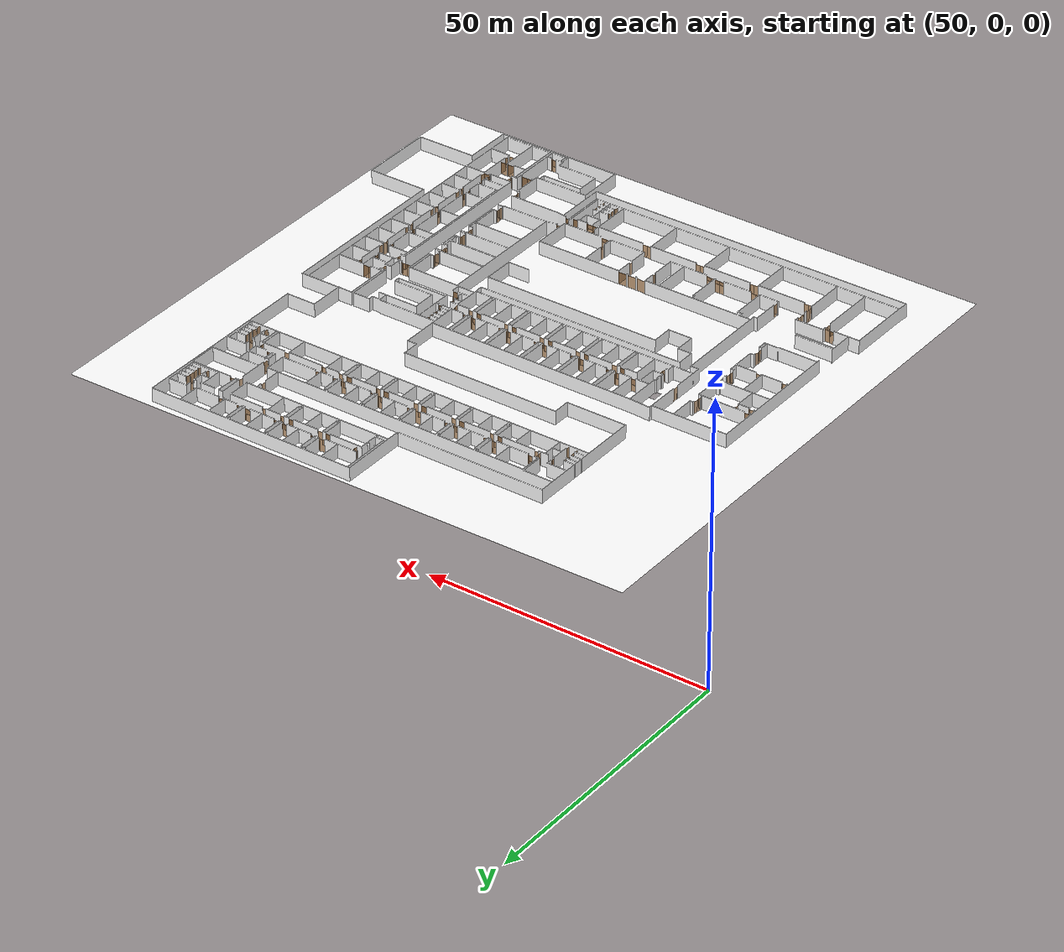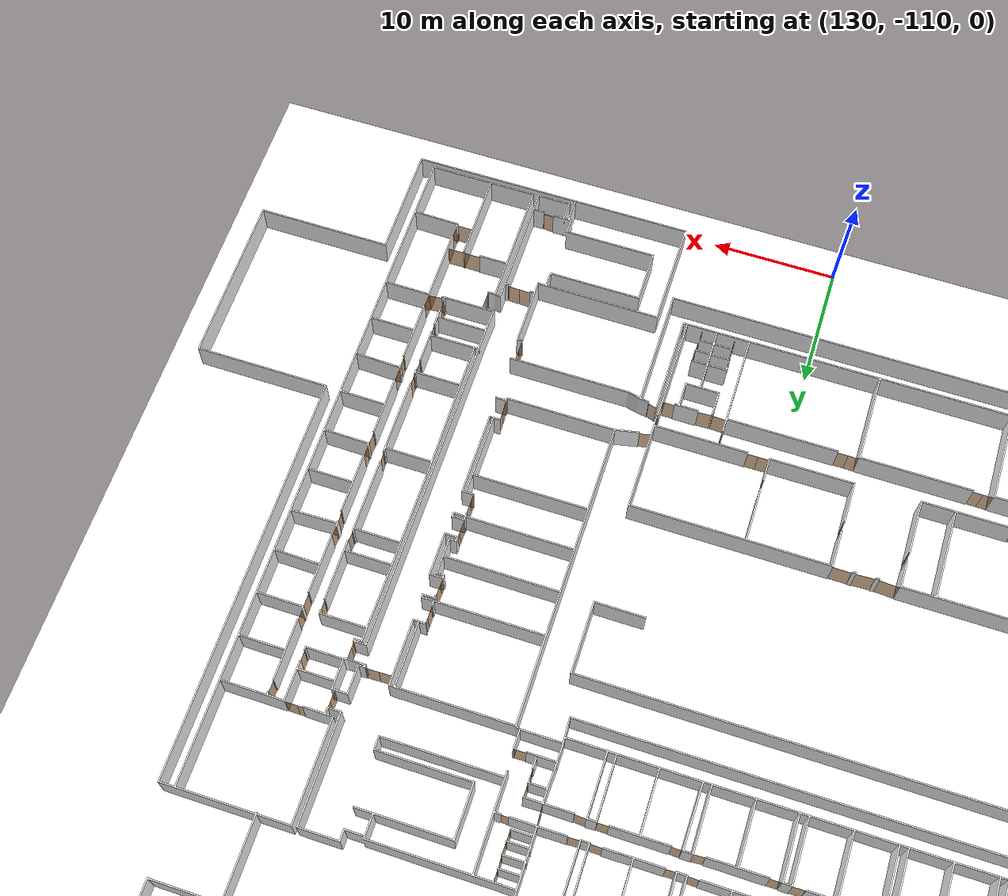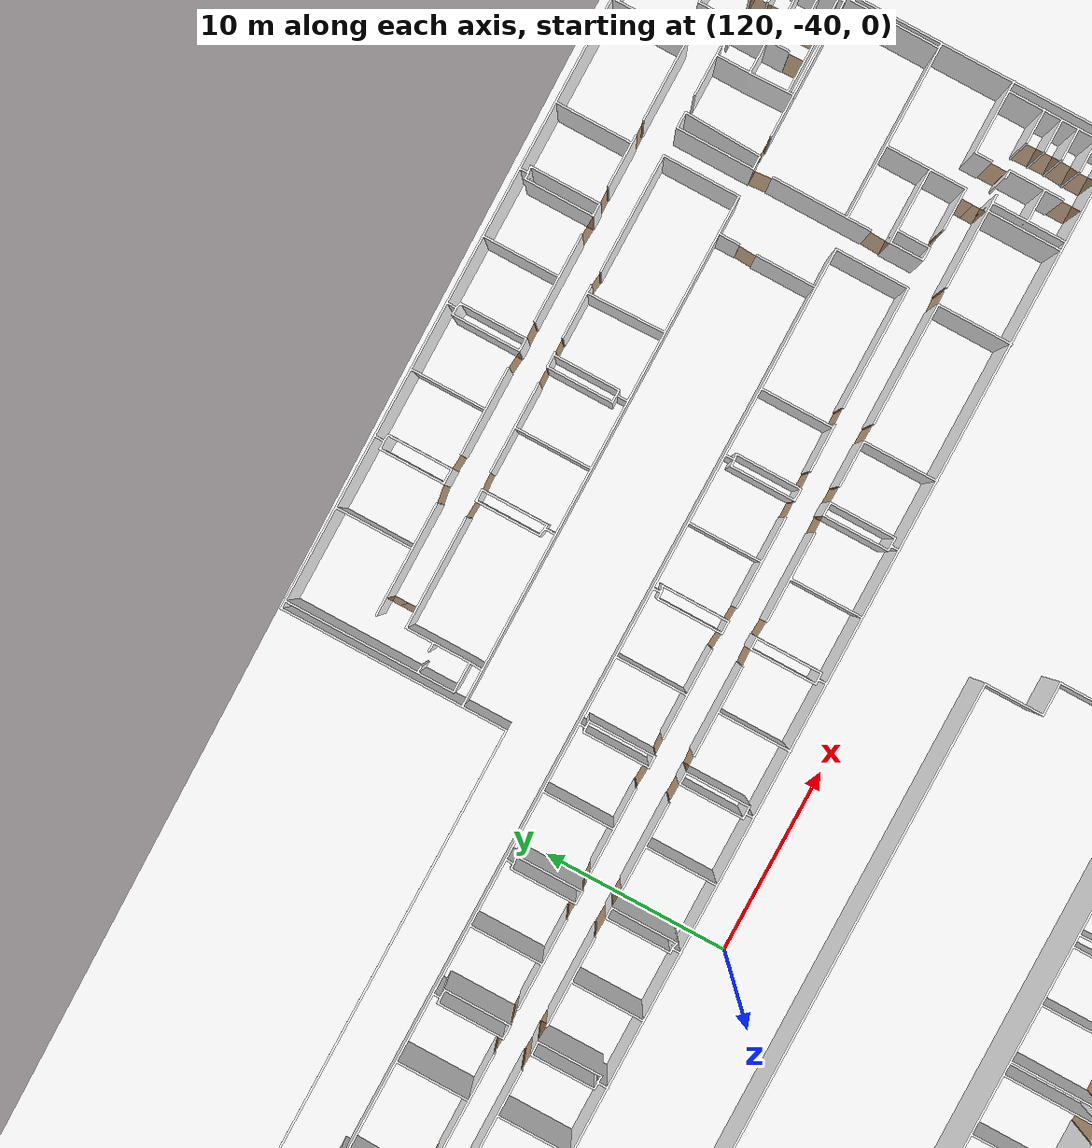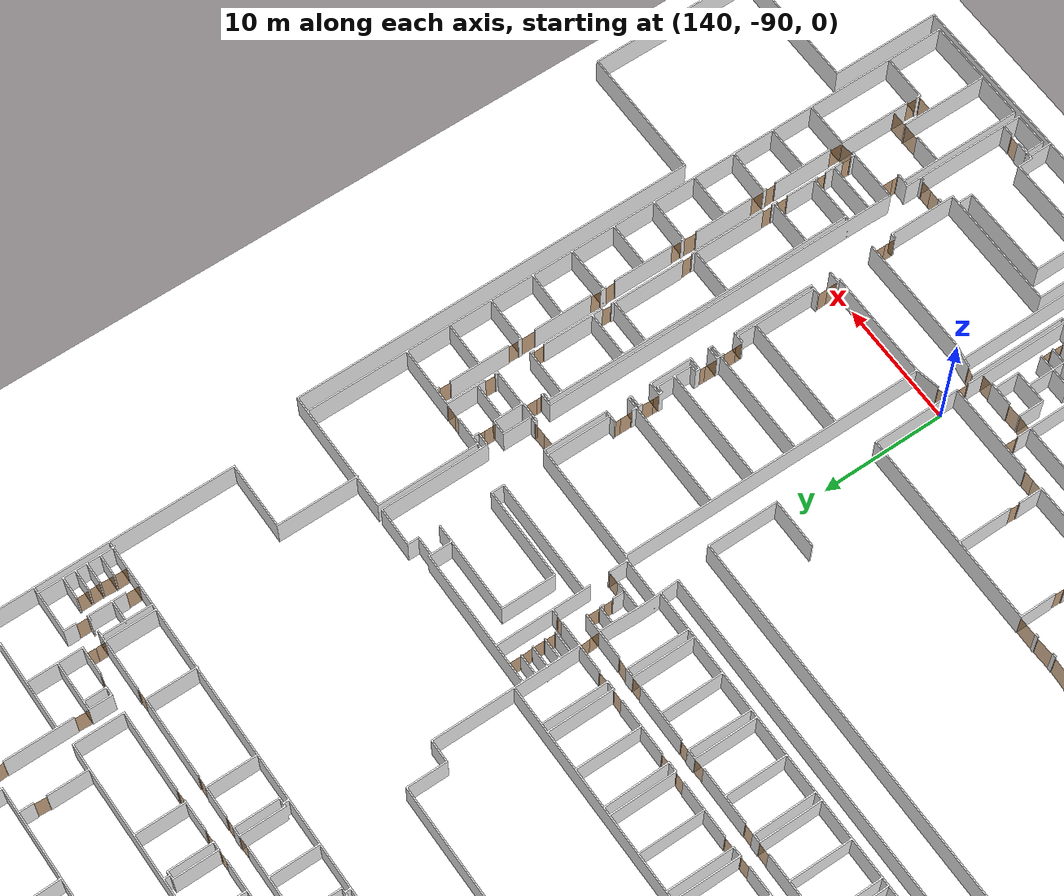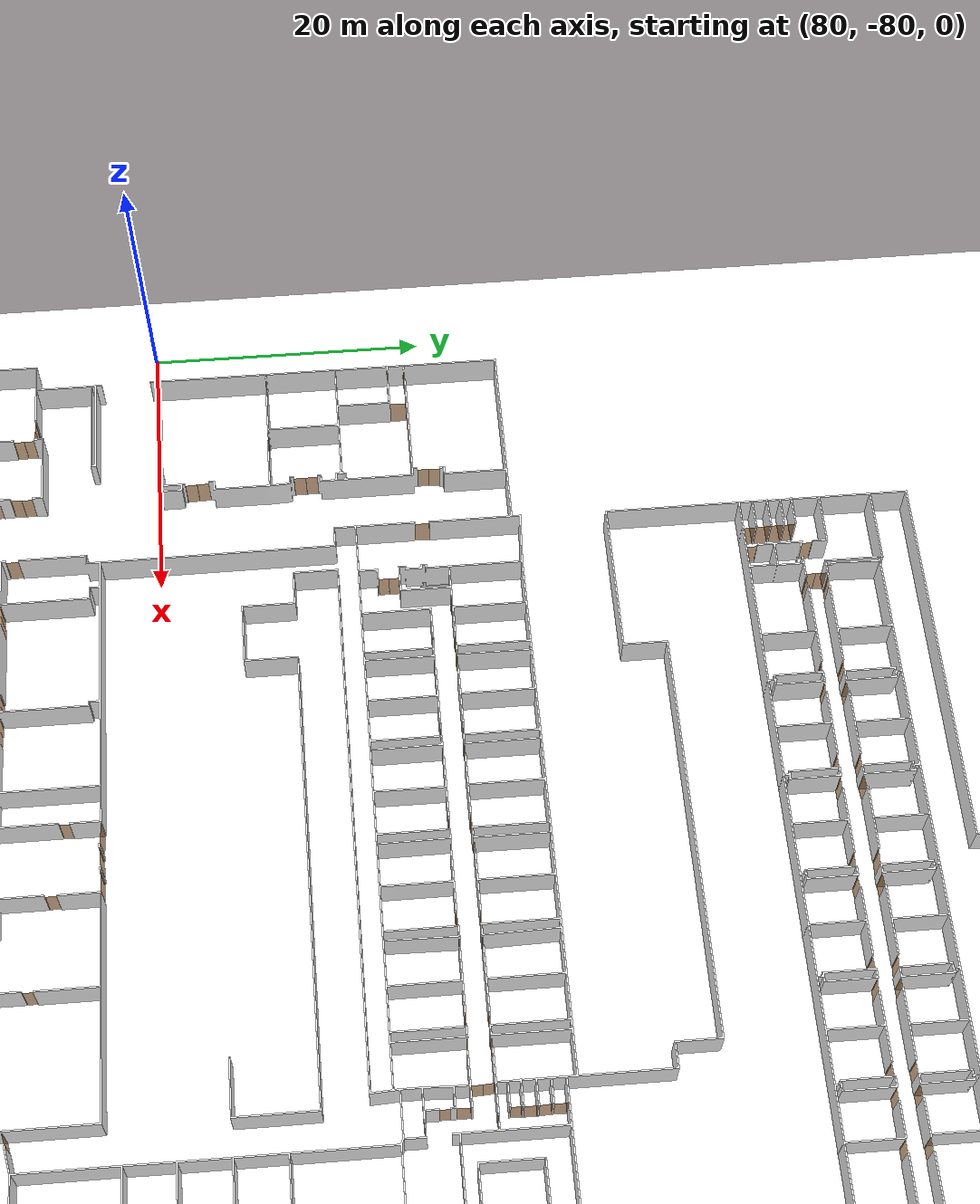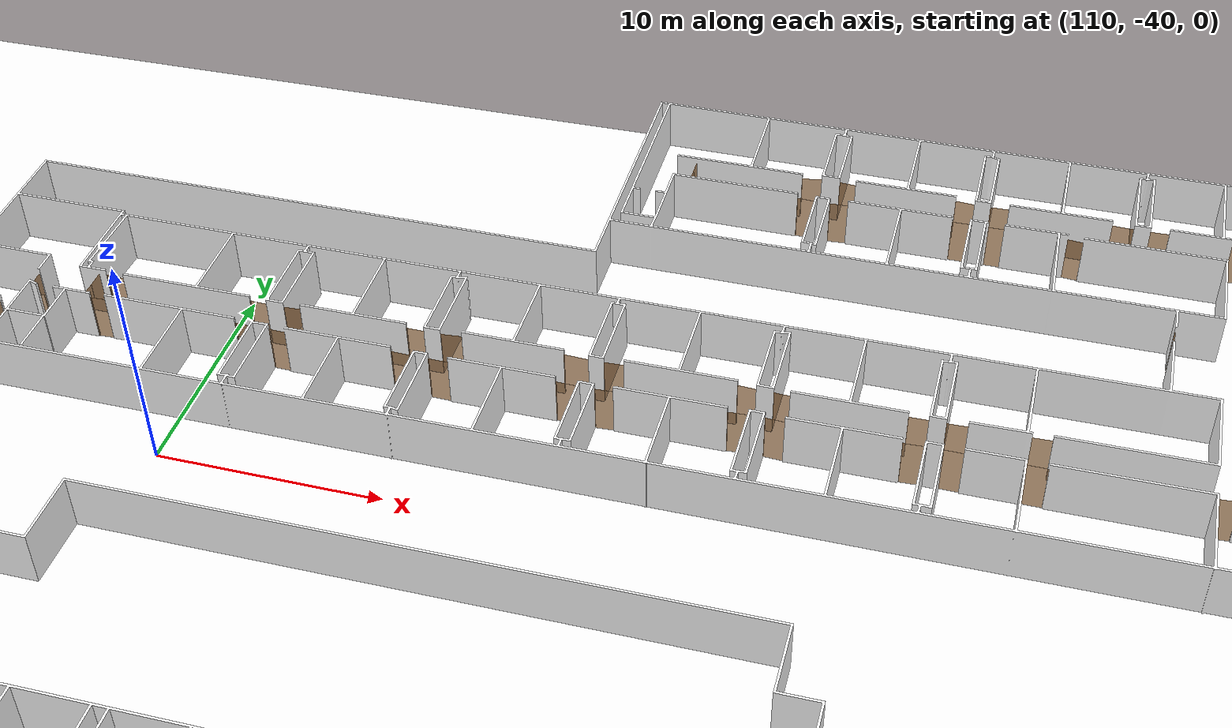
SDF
<sdf version="1.7">
 <world name="sim_world">
  <physics name="10ms" type="ode">
   <max_step_size>0.01</max_step_size>
   <real_time_factor>1.0</real_time_factor>
  </physics>
  <plugin filename="gz-sim-physics-system" name="gz::sim::systems::Physics"/>
  <plugin filename="gz-sim-user-commands-system" name="gz::sim::systems::UserCommands"/>
  <plugin filename="gz-sim-scene-broadcaster-system" name="gz::sim::systems::SceneBroadcaster"/>
  <plugin filename="libdoor.so" name="door"/>
  <plugin filename="liblift.so" name="lift"/>
  <scene><ambient>1 1 1</ambient><background>0.8 0.8 0.8</background><grid>false</grid></scene>
  <light type="directional" name="sun">
   <pose>0 0 10 0 0 0</pose>
   <diffuse>1 1 1 1</diffuse>
   <specular>0.2 0.2 0.2 1</specular>
   <attenuation>
    <range>1000</range>
    <constant>0.09</constant>
    <linear>0.001</linear>
    <quadratic>0.001</quadratic>
   </attenuation>
   <direction>-0.5 0.1 -0.9</direction>
  </light>
  <model name="puerta11">
   <pose>99.59689328884753 -34.192335040117115 0.0 0 0 -1.523227629626105</pose>
   <link name="right">
    <pose>0 0 1.11 0 0 0</pose>
    <visual name="right_visual">
     <geometry><box><size>0.8234942961766232 0.03 2.2</size></box></geometry>
     <material>
      <ambient>0.5 0.25 0 0.6</ambient>
      <diffuse>0.5 0.25 0 0.6</diffuse>
      <pbr><metal><metalness>0.0</metalness></metal></pbr>
     </material>
    </visual>
    <collision name="right_collision">
     <geometry><box><size>0.8234942961766232 0.03 2.2</size></box></geometry>
     <surface><contact><collide_bitmask>0x02</collide_bitmask></contact></surface>
    </collision>
    <inertial>
     <mass>50.0</mass>
     <inertia><ixx>20.17041666666667</ixx><iyy>22.992261899314304</iyy><izz>2.8293452326476336</izz></inertia>
    </inertial>
   </link>
   <joint name="right_joint" type="revolute">
    <parent>world</parent>
    <child>right</child>
    <axis><xyz>0 0 1</xyz><limit><lower>0</lower><upper>1.57</upper></limit></axis>
    <pose>0.4167471480883116 0 0 0 0 0</pose>
   </joint>
   <plugin name="register_component" filename="libregister_component.so">
    <component name="Door">
     <v_max_door>0.5</v_max_door>
     <a_max_door>0.3</a_max_door>
     <a_nom_door>0.15</a_nom_door>
     <dx_min_door>0.01</dx_min_door>
     <f_max_door>500.0</f_max_door>
     <ros_interface>true</ros_interface>
     <door name="puerta11" type="SwingDoor" left_joint_name="empty_joint" right_joint_name="right_joint"/>
    </component>
   </plugin>
  </model>
  <model name="puerta12">
   <pose>99.61010438448491 -35.09098405833076 0.0 0 0 1.5571033318122445</pose>
   <link name="right">
    <pose>0 0 1.11 0 0 0</pose>
    <visual name="right_visual">
     <geometry><box><size>0.9548370211000183 0.03 2.2</size></box></geometry>
     <material>
      <ambient>0.5 0.25 0 0.6</ambient>
      <diffuse>0.5 0.25 0 0.6</diffuse>
      <pbr><metal><metalness>0.0</metalness></metal></pbr>
     </material>
    </visual>
    <collision name="right_collision">
     <geometry><box><size>0.9548370211000183 0.03 2.2</size></box></geometry>
     <surface><contact><collide_bitmask>0x02</collide_bitmask></contact></surface>
    </collision>
    <inertial>
     <mass>50.0</mass>
     <inertia><ixx>20.17041666666667</ixx><iyy>23.965473903596493</iyy><izz>3.8025572369298204</izz></inertia>
    </inertial>
   </link>
   <joint name="right_joint" type="revolute">
    <parent>world</parent>
    <child>right</child>
    <axis><xyz>0 0 -1</xyz><limit><lower>0</lower><upper>1.57</upper></limit></axis>
    <pose>0.48241851055000917 0 0 0 0 0</pose>
   </joint>
   <plugin name="register_component" filename="libregister_component.so">
    <component name="Door">
     <v_max_door>0.5</v_max_door>
     <a_max_door>0.3</a_max_door>
     <a_nom_door>0.15</a_nom_door>
     <dx_min_door>0.01</dx_min_door>
     <f_max_door>500.0</f_max_door>
     <ros_interface>true</ros_interface>
     <door name="puerta12" type="SwingDoor" left_joint_name="empty_joint" right_joint_name="right_joint"/>
    </component>
   </plugin>
  </model>
  <model name="puerta13">
   <pose>99.63652657575972 -36.11520159542911 0.0 0 0 -1.50991734569296</pose>
   <link name="right">
    <pose>0 0 1.11 0 0 0</pose>
    <visual name="right_visual">
     <geometry><box><size>1.0756998205890995 0.03 2.2</size></box></geometry>
     <material>
      <ambient>0.5 0.25 0 0.6</ambient>
      <diffuse>0.5 0.25 0 0.6</diffuse>
      <pbr><metal><metalness>0.0</metalness></metal></pbr>
     </material>
    </visual>
    <collision name="right_collision">
     <geometry><box><size>1.0756998205890995 0.03 2.2</size></box></geometry>
     <surface><contact><collide_bitmask>0x02</collide_bitmask></contact></surface>
    </collision>
    <inertial>
     <mass>50.0</mass>
     <inertia><ixx>20.17041666666667</ixx><iyy>24.98804210006426</iyy><izz>4.825125433397587</izz></inertia>
    </inertial>
   </link>
   <joint name="right_joint" type="revolute">
    <parent>world</parent>
    <child>right</child>
    <axis><xyz>0 0 1</xyz><limit><lower>0</lower><upper>1.57</upper></limit></axis>
    <pose>0.5428499102945498 0 0 0 0 0</pose>
   </joint>
   <plugin name="register_component" filename="libregister_component.so">
    <component name="Door">
     <v_max_door>0.5</v_max_door>
     <a_max_door>0.3</a_max_door>
     <a_nom_door>0.15</a_nom_door>
     <dx_min_door>0.01</dx_min_door>
     <f_max_door>500.0</f_max_door>
     <ros_interface>true</ros_interface>
     <door name="puerta13" type="SwingDoor" left_joint_name="empty_joint" right_joint_name="right_joint"/>
    </component>
   </plugin>
  </model>
  <model name="puerta14">
   <pose>99.66989090327709 -37.17492921124709 0.0 0 0 1.571446257648225</pose>
   <link name="right">
    <pose>0 0 1.11 0 0 0</pose>
    <visual name="right_visual">
     <geometry><box><size>1.025766946152035 0.03 2.2</size></box></geometry>
     <material>
      <ambient>0.5 0.25 0 0.6</ambient>
      <diffuse>0.5 0.25 0 0.6</diffuse>
      <pbr><metal><metalness>0.0</metalness></metal></pbr>
     </material>
    </visual>
    <collision name="right_collision">
     <geometry><box><size>1.025766946152035 0.03 2.2</size></box></geometry>
     <surface><contact><collide_bitmask>0x02</collide_bitmask></contact></surface>
    </collision>
    <inertial>
     <mass>50.0</mass>
     <inertia><ixx>20.17041666666667</ixx><iyy>24.550824282575302</iyy><izz>4.387907615908632</izz></inertia>
    </inertial>
   </link>
   <joint name="right_joint" type="revolute">
    <parent>world</parent>
    <child>right</child>
    <axis><xyz>0 0 -1</xyz><limit><lower>0</lower><upper>1.57</upper></limit></axis>
    <pose>0.5178834730760175 0 0 0 0 0</pose>
   </joint>
   <plugin name="register_component" filename="libregister_component.so">
    <component name="Door">
     <v_max_door>0.5</v_max_door>
     <a_max_door>0.3</a_max_door>
     <a_nom_door>0.15</a_nom_door>
     <dx_min_door>0.01</dx_min_door>
     <f_max_door>500.0</f_max_door>
     <ros_interface>true</ros_interface>
     <door name="puerta14" type="SwingDoor" left_joint_name="empty_joint" right_joint_name="right_joint"/>
    </component>
   </plugin>
  </model>
  <model name="puerta15">
   <pose>101.22894744592494 -37.20865116396483 0.0 0 0 -1.6013044931290397</pose>
   <link name="right">
    <pose>0 0 1.11 0 0 0</pose>
    <visual name="right_visual">
     <geometry><box><size>0.8934450750594292 0.03 2.2</size></box></geometry>
     <material>
      <ambient>0.5 0.25 0 0.6</ambient>
      <diffuse>0.5 0.25 0 0.6</diffuse>
      <pbr><metal><metalness>0.0</metalness></metal></pbr>
     </material>
    </visual>
    <collision name="right_collision">
     <geometry><box><size>0.8934450750594292 0.03 2.2</size></box></geometry>
     <surface><contact><collide_bitmask>0x02</collide_bitmask></contact></surface>
    </collision>
    <inertial>
     <mass>50.0</mass>
     <inertia><ixx>20.17041666666667</ixx><iyy>23.49268375894979</iyy><izz>3.3297670922831215</izz></inertia>
    </inertial>
   </link>
   <joint name="right_joint" type="revolute">
    <parent>world</parent>
    <child>right</child>
    <axis><xyz>0 0 1</xyz><limit><lower>0</lower><upper>1.57</upper></limit></axis>
    <pose>0.4517225375297146 0 0 0 0 0</pose>
   </joint>
   <plugin name="register_component" filename="libregister_component.so">
    <component name="Door">
     <v_max_door>0.5</v_max_door>
     <a_max_door>0.3</a_max_door>
     <a_nom_door>0.15</a_nom_door>
     <dx_min_door>0.01</dx_min_door>
     <f_max_door>500.0</f_max_door>
     <ros_interface>true</ros_interface>
     <door name="puerta15" type="SwingDoor" left_joint_name="empty_joint" right_joint_name="right_joint"/>
    </component>
   </plugin>
  </model>
  <model name="puerta16">
   <pose>103.8129578128484 -32.91683320781389 0.0 0 0 1.5707963267948966</pose>
   <link name="right">
    <pose>0.40783998586328707 0 1.11 0 0 0</pose>
    <visual name="right_visual">
     <geometry><box><size>0.8056799717265741 0.03 2.2</size></box></geometry>
     <material>
      <ambient>0.5 0.25 0 0.6</ambient>
      <diffuse>0.5 0.25 0 0.6</diffuse>
      <pbr><metal><metalness>0.0</metalness></metal></pbr>
     </material>
    </visual>
    <collision name="right_collision">
     <geometry><box><size>0.8056799717265741 0.03 2.2</size></box></geometry>
     <surface><contact><collide_bitmask>0x02</collide_bitmask></contact></surface>
    </collision>
    <inertial>
     <mass>50.0</mass>
     <inertia><ixx>20.17041666666667</ixx><iyy>22.871334236838894</iyy><izz>2.708417570172222</izz></inertia>
    </inertial>
   </link>
   <joint name="right_joint" type="revolute">
    <parent>world</parent>
    <child>right</child>
    <axis><xyz>0 0 -1</xyz><limit><lower>0</lower><upper>1.57</upper></limit></axis>
    <pose>0.40783998586328707 0 0 0 0 0</pose>
   </joint>
   <link name="left">
    <pose>-0.40783998586328707 0 1.11 0 0 0</pose>
    <visual name="left_visual">
     <geometry><box><size>0.8056799717265741 0.03 2.2</size></box></geometry>
     <material>
      <ambient>0.5 0.25 0 0.6</ambient>
      <diffuse>0.5 0.25 0 0.6</diffuse>
      <pbr><metal><metalness>0.0</metalness></metal></pbr>
     </material>
    </visual>
    <collision name="left_collision">
     <geometry><box><size>0.8056799717265741 0.03 2.2</size></box></geometry>
     <surface><contact><collide_bitmask>0x02</collide_bitmask></contact></surface>
    </collision>
    <inertial>
     <mass>50.0</mass>
     <inertia><ixx>20.17041666666667</ixx><iyy>22.871334236838894</iyy><izz>2.708417570172222</izz></inertia>
    </inertial>
   </link>
   <joint name="left_joint" type="revolute">
    <parent>world</parent>
    <child>left</child>
    <axis><xyz>0 0 -1</xyz><limit><lower>-1.57</lower><upper>0</upper></limit></axis>
    <pose>-0.40783998586328707 0 0 0 0 0</pose>
   </joint>
   <plugin name="register_component" filename="libregister_component.so">
    <component name="Door">
     <v_max_door>0.5</v_max_door>
     <a_max_door>0.3</a_max_door>
     <a_nom_door>0.15</a_nom_door>
     <dx_min_door>0.01</dx_min_door>
     <f_max_door>500.0</f_max_door>
     <ros_interface>true</ros_interface>
     <door name="puerta16" type="DoubleSwingDoor" left_joint_name="left_joint" right_joint_name="right_joint"/>
    </component>
   </plugin>
  </model>
  <model name="puerta17">
   <pose>104.5937588091501 -32.12347325594603 0.0 0 0 3.093986082694925</pose>
   <link name="right">
    <pose>0 0 1.11 0 0 0</pose>
    <visual name="right_visual">
     <geometry><box><size>0.9280408053211409 0.03 2.2</size></box></geometry>
     <material>
      <ambient>0.5 0.25 0 0.6</ambient>
      <diffuse>0.5 0.25 0 0.6</diffuse>
      <pbr><metal><metalness>0.0</metalness></metal></pbr>
     </material>
    </visual>
    <collision name="right_collision">
     <geometry><box><size>0.9280408053211409 0.03 2.2</size></box></geometry>
     <surface><contact><collide_bitmask>0x02</collide_bitmask></contact></surface>
    </collision>
    <inertial>
     <mass>50.0</mass>
     <inertia><ixx>20.17041666666667</ixx><iyy>23.755248901421304</iyy><izz>3.592332234754632</izz></inertia>
    </inertial>
   </link>
   <joint name="right_joint" type="revolute">
    <parent>world</parent>
    <child>right</child>
    <axis><xyz>0 0 1</xyz><limit><lower>0</lower><upper>1.57</upper></limit></axis>
    <pose>0.46902040266057043 0 0 0 0 0</pose>
   </joint>
   <plugin name="register_component" filename="libregister_component.so">
    <component name="Door">
     <v_max_door>0.5</v_max_door>
     <a_max_door>0.3</a_max_door>
     <a_nom_door>0.15</a_nom_door>
     <dx_min_door>0.01</dx_min_door>
     <f_max_door>500.0</f_max_door>
     <ros_interface>true</ros_interface>
     <door name="puerta17" type="SwingDoor" left_joint_name="empty_joint" right_joint_name="right_joint"/>
    </component>
   </plugin>
  </model>
  <model name="puerta18">
   <pose>104.53996777165837 -33.685685315067786 0.0 0 0 -3.0890348459921255</pose>
   <link name="right">
    <pose>0 0 1.11 0 0 0</pose>
    <visual name="right_visual">
     <geometry><box><size>0.778074015602144 0.03 2.2</size></box></geometry>
     <material>
      <ambient>0.5 0.25 0 0.6</ambient>
      <diffuse>0.5 0.25 0 0.6</diffuse>
      <pbr><metal><metalness>0.0</metalness></metal></pbr>
     </material>
    </visual>
    <collision name="right_collision">
     <geometry><box><size>0.778074015602144 0.03 2.2</size></box></geometry>
     <surface><contact><collide_bitmask>0x02</collide_bitmask></contact></surface>
    </collision>
    <inertial>
     <mass>50.0</mass>
     <inertia><ixx>20.17041666666667</ixx><iyy>22.68916322398019</iyy><izz>2.5262465573135224</izz></inertia>
    </inertial>
   </link>
   <joint name="right_joint" type="revolute">
    <parent>world</parent>
    <child>right</child>
    <axis><xyz>0 0 -1</xyz><limit><lower>0</lower><upper>1.57</upper></limit></axis>
    <pose>0.394037007801072 0 0 0 0 0</pose>
   </joint>
   <plugin name="register_component" filename="libregister_component.so">
    <component name="Door">
     <v_max_door>0.5</v_max_door>
     <a_max_door>0.3</a_max_door>
     <a_nom_door>0.15</a_nom_door>
     <dx_min_door>0.01</dx_min_door>
     <f_max_door>500.0</f_max_door>
     <ros_interface>true</ros_interface>
     <door name="puerta18" type="SwingDoor" left_joint_name="empty_joint" right_joint_name="right_joint"/>
    </component>
   </plugin>
  </model>
  <model name="puerta19">
   <pose>111.47225880283908 -32.160666276785065 0.0 0 0 -0.0333225657936494</pose>
   <link name="right">
    <pose>0 0 1.11 0 0 0</pose>
    <visual name="right_visual">
     <geometry><box><size>0.8828336376845018 0.03 2.2</size></box></geometry>
     <material>
      <ambient>0.5 0.25 0 0.6</ambient>
      <diffuse>0.5 0.25 0 0.6</diffuse>
      <pbr><metal><metalness>0.0</metalness></metal></pbr>
     </material>
    </visual>
    <collision name="right_collision">
     <geometry><box><size>0.8828336376845018 0.03 2.2</size></box></geometry>
     <surface><contact><collide_bitmask>0x02</collide_bitmask></contact></surface>
    </collision>
    <inertial>
     <mass>50.0</mass>
     <inertia><ixx>20.17041666666667</ixx><iyy>23.414146799280214</iyy><izz>3.251230132613543</izz></inertia>
    </inertial>
   </link>
   <joint name="right_joint" type="revolute">
    <parent>world</parent>
    <child>right</child>
    <axis><xyz>0 0 -1</xyz><limit><lower>0</lower><upper>1.57</upper></limit></axis>
    <pose>0.44641681884225093 0 0 0 0 0</pose>
   </joint>
   <plugin name="register_component" filename="libregister_component.so">
    <component name="Door">
     <v_max_door>0.5</v_max_door>
     <a_max_door>0.3</a_max_door>
     <a_nom_door>0.15</a_nom_door>
     <dx_min_door>0.01</dx_min_door>
     <f_max_door>500.0</f_max_door>
     <ros_interface>true</ros_interface>
     <door name="puerta19" type="SwingDoor" left_joint_name="empty_joint" right_joint_name="right_joint"/>
    </component>
   </plugin>
  </model>
  <model name="puerta20">
   <pose>111.42940688912353 -33.69079725175551 0.0 0 0 -0.05792736840237623</pose>
   <link name="right">
    <pose>0 0 1.11 0 0 0</pose>
    <visual name="right_visual">
     <geometry><box><size>0.8816878807771851 0.03 2.2</size></box></geometry>
     <material>
      <ambient>0.5 0.25 0 0.6</ambient>
      <diffuse>0.5 0.25 0 0.6</diffuse>
      <pbr><metal><metalness>0.0</metalness></metal></pbr>
     </material>
    </visual>
    <collision name="right_collision">
     <geometry><box><size>0.8816878807771851 0.03 2.2</size></box></geometry>
     <surface><contact><collide_bitmask>0x02</collide_bitmask></contact></surface>
    </collision>
    <inertial>
     <mass>50.0</mass>
     <inertia><ixx>20.17041666666667</ixx><iyy>23.40572299628902</iyy><izz>3.242806329622349</izz></inertia>
    </inertial>
   </link>
   <joint name="right_joint" type="revolute">
    <parent>world</parent>
    <child>right</child>
    <axis><xyz>0 0 1</xyz><limit><lower>0</lower><upper>1.57</upper></limit></axis>
    <pose>0.44584394038859254 0 0 0 0 0</pose>
   </joint>
   <plugin name="register_component" filename="libregister_component.so">
    <component name="Door">
     <v_max_door>0.5</v_max_door>
     <a_max_door>0.3</a_max_door>
     <a_nom_door>0.15</a_nom_door>
     <dx_min_door>0.01</dx_min_door>
     <f_max_door>500.0</f_max_door>
     <ros_interface>true</ros_interface>
     <door name="puerta20" type="SwingDoor" left_joint_name="empty_joint" right_joint_name="right_joint"/>
    </component>
   </plugin>
  </model>
  <model name="puerta21">
   <pose>112.99944462910057 -33.70432389904029 0.0 0 0 3.109967890999371</pose>
   <link name="right">
    <pose>0 0 1.11 0 0 0</pose>
    <visual name="right_visual">
     <geometry><box><size>0.846919796126006 0.03 2.2</size></box></geometry>
     <material>
      <ambient>0.5 0.25 0 0.6</ambient>
      <diffuse>0.5 0.25 0 0.6</diffuse>
      <pbr><metal><metalness>0.0</metalness></metal></pbr>
     </material>
    </visual>
    <collision name="right_collision">
     <geometry><box><size>0.846919796126006 0.03 2.2</size></box></geometry>
     <surface><contact><collide_bitmask>0x02</collide_bitmask></contact></surface>
    </collision>
    <inertial>
     <mass>50.0</mass>
     <inertia><ixx>20.17041666666667</ixx><iyy>23.155304754458818</iyy><izz>2.9923880877921483</izz></inertia>
    </inertial>
   </link>
   <joint name="right_joint" type="revolute">
    <parent>world</parent>
    <child>right</child>
    <axis><xyz>0 0 -1</xyz><limit><lower>0</lower><upper>1.57</upper></limit></axis>
    <pose>0.428459898063003 0 0 0 0 0</pose>
   </joint>
   <plugin name="register_component" filename="libregister_component.so">
    <component name="Door">
     <v_max_door>0.5</v_max_door>
     <a_max_door>0.3</a_max_door>
     <a_nom_door>0.15</a_nom_door>
     <dx_min_door>0.01</dx_min_door>
     <f_max_door>500.0</f_max_door>
     <ros_interface>true</ros_interface>
     <door name="puerta21" type="SwingDoor" left_joint_name="empty_joint" right_joint_name="right_joint"/>
    </component>
   </plugin>
  </model>
  <model name="puerta22">
   <pose>113.05615977852477 -32.15321925790666 0.0 0 0 -3.0889835429859094</pose>
   <link name="right">
    <pose>0 0 1.11 0 0 0</pose>
    <visual name="right_visual">
     <geometry><box><size>0.8389145263994523 0.03 2.2</size></box></geometry>
     <material>
      <ambient>0.5 0.25 0 0.6</ambient>
      <diffuse>0.5 0.25 0 0.6</diffuse>
      <pbr><metal><metalness>0.0</metalness></metal></pbr>
     </material>
    </visual>
    <collision name="right_collision">
     <geometry><box><size>0.8389145263994523 0.03 2.2</size></box></geometry>
     <surface><contact><collide_bitmask>0x02</collide_bitmask></contact></surface>
    </collision>
    <inertial>
     <mass>50.0</mass>
     <inertia><ixx>20.17041666666667</ixx><iyy>23.099073260850076</iyy><izz>2.936156594183406</izz></inertia>
    </inertial>
   </link>
   <joint name="right_joint" type="revolute">
    <parent>world</parent>
    <child>right</child>
    <axis><xyz>0 0 1</xyz><limit><lower>0</lower><upper>1.57</upper></limit></axis>
    <pose>0.42445726319972615 0 0 0 0 0</pose>
   </joint>
   <plugin name="register_component" filename="libregister_component.so">
    <component name="Door">
     <v_max_door>0.5</v_max_door>
     <a_max_door>0.3</a_max_door>
     <a_nom_door>0.15</a_nom_door>
     <dx_min_door>0.01</dx_min_door>
     <f_max_door>500.0</f_max_door>
     <ros_interface>true</ros_interface>
     <door name="puerta22" type="SwingDoor" left_joint_name="empty_joint" right_joint_name="right_joint"/>
    </component>
   </plugin>
  </model>
  <model name="puerta23">
   <pose>118.73741474846322 -32.13834625692635 0.0 0 0 -0.016416297145013498</pose>
   <link name="right">
    <pose>0 0 1.11 0 0 0</pose>
    <visual name="right_visual">
     <geometry><box><size>0.8973122046900142 0.03 2.2</size></box></geometry>
     <material>
      <ambient>0.5 0.25 0 0.6</ambient>
      <diffuse>0.5 0.25 0 0.6</diffuse>
      <pbr><metal><metalness>0.0</metalness></metal></pbr>
     </material>
    </visual>
    <collision name="right_collision">
     <geometry><box><size>0.8973122046900142 0.03 2.2</size></box></geometry>
     <surface><contact><collide_bitmask>0x02</collide_bitmask></contact></surface>
    </collision>
    <inertial>
     <mass>50.0</mass>
     <inertia><ixx>20.17041666666667</ixx><iyy>23.521538302856897</iyy><izz>3.358621636190225</izz></inertia>
    </inertial>
   </link>
   <joint name="right_joint" type="revolute">
    <parent>world</parent>
    <child>right</child>
    <axis><xyz>0 0 -1</xyz><limit><lower>0</lower><upper>1.57</upper></limit></axis>
    <pose>0.4536561023450071 0 0 0 0 0</pose>
   </joint>
   <plugin name="register_component" filename="libregister_component.so">
    <component name="Door">
     <v_max_door>0.5</v_max_door>
     <a_max_door>0.3</a_max_door>
     <a_nom_door>0.15</a_nom_door>
     <dx_min_door>0.01</dx_min_door>
     <f_max_door>500.0</f_max_door>
     <ros_interface>true</ros_interface>
     <door name="puerta23" type="SwingDoor" left_joint_name="empty_joint" right_joint_name="right_joint"/>
    </component>
   </plugin>
  </model>
  <model name="puerta24">
   <pose>118.72565519040381 -33.73308117250576 0.0 0 0 -0.027403382231023843</pose>
   <link name="right">
    <pose>0 0 1.11 0 0 0</pose>
    <visual name="right_visual">
     <geometry><box><size>1.1001909273704624 0.03 2.2</size></box></geometry>
     <material>
      <ambient>0.5 0.25 0 0.6</ambient>
      <diffuse>0.5 0.25 0 0.6</diffuse>
      <pbr><metal><metalness>0.0</metalness></metal></pbr>
     </material>
    </visual>
    <collision name="right_collision">
     <geometry><box><size>1.1001909273704624 0.03 2.2</size></box></geometry>
     <surface><contact><collide_bitmask>0x02</collide_bitmask></contact></surface>
    </collision>
    <inertial>
     <mass>50.0</mass>
     <inertia><ixx>20.17041666666667</ixx><iyy>25.210083652784498</iyy><izz>5.047166986117825</izz></inertia>
    </inertial>
   </link>
   <joint name="right_joint" type="revolute">
    <parent>world</parent>
    <child>right</child>
    <axis><xyz>0 0 1</xyz><limit><lower>0</lower><upper>1.57</upper></limit></axis>
    <pose>0.5550954636852312 0 0 0 0 0</pose>
   </joint>
   <plugin name="register_component" filename="libregister_component.so">
    <component name="Door">
     <v_max_door>0.5</v_max_door>
     <a_max_door>0.3</a_max_door>
     <a_nom_door>0.15</a_nom_door>
     <dx_min_door>0.01</dx_min_door>
     <f_max_door>500.0</f_max_door>
     <ros_interface>true</ros_interface>
     <door name="puerta24" type="SwingDoor" left_joint_name="empty_joint" right_joint_name="right_joint"/>
    </component>
   </plugin>
  </model>
  <model name="puerta25">
   <pose>120.3370933065184 -33.75588503822381 0.0 0 0 3.1262230047063087</pose>
   <link name="right">
    <pose>0 0 1.11 0 0 0</pose>
    <visual name="right_visual">
     <geometry><box><size>0.9782561890716672 0.03 2.2</size></box></geometry>
     <material>
      <ambient>0.5 0.25 0 0.6</ambient>
      <diffuse>0.5 0.25 0 0.6</diffuse>
      <pbr><metal><metalness>0.0</metalness></metal></pbr>
     </material>
    </visual>
    <collision name="right_collision">
     <geometry><box><size>0.9782561890716672 0.03 2.2</size></box></geometry>
     <surface><contact><collide_bitmask>0x02</collide_bitmask></contact></surface>
    </collision>
    <inertial>
     <mass>50.0</mass>
     <inertia><ixx>20.17041666666667</ixx><iyy>24.15410488107093</iyy><izz>3.9911882144042568</izz></inertia>
    </inertial>
   </link>
   <joint name="right_joint" type="revolute">
    <parent>world</parent>
    <child>right</child>
    <axis><xyz>0 0 -1</xyz><limit><lower>0</lower><upper>1.57</upper></limit></axis>
    <pose>0.4941280945358336 0 0 0 0 0</pose>
   </joint>
   <plugin name="register_component" filename="libregister_component.so">
    <component name="Door">
     <v_max_door>0.5</v_max_door>
     <a_max_door>0.3</a_max_door>
     <a_nom_door>0.15</a_nom_door>
     <dx_min_door>0.01</dx_min_door>
     <f_max_door>500.0</f_max_door>
     <ros_interface>true</ros_interface>
     <door name="puerta25" type="SwingDoor" left_joint_name="empty_joint" right_joint_name="right_joint"/>
    </component>
   </plugin>
  </model>
  <model name="puerta26">
   <pose>120.35850874498794 -32.10117427286381 0.0 0 0 -3.0548490071708736</pose>
   <link name="right">
    <pose>0 0 1.11 0 0 0</pose>
    <visual name="right_visual">
     <geometry><box><size>1.0200468010529855 0.03 2.2</size></box></geometry>
     <material>
      <ambient>0.5 0.25 0 0.6</ambient>
      <diffuse>0.5 0.25 0 0.6</diffuse>
      <pbr><metal><metalness>0.0</metalness></metal></pbr>
     </material>
    </visual>
    <collision name="right_collision">
     <geometry><box><size>1.0200468010529855 0.03 2.2</size></box></geometry>
     <surface><contact><collide_bitmask>0x02</collide_bitmask></contact></surface>
    </collision>
    <inertial>
     <mass>50.0</mass>
     <inertia><ixx>20.17041666666667</ixx><iyy>24.50206448474346</iyy><izz>4.339147818076788</izz></inertia>
    </inertial>
   </link>
   <joint name="right_joint" type="revolute">
    <parent>world</parent>
    <child>right</child>
    <axis><xyz>0 0 1</xyz><limit><lower>0</lower><upper>1.57</upper></limit></axis>
    <pose>0.5150234005264928 0 0 0 0 0</pose>
   </joint>
   <plugin name="register_component" filename="libregister_component.so">
    <component name="Door">
     <v_max_door>0.5</v_max_door>
     <a_max_door>0.3</a_max_door>
     <a_nom_door>0.15</a_nom_door>
     <dx_min_door>0.01</dx_min_door>
     <f_max_door>500.0</f_max_door>
     <ros_interface>true</ros_interface>
     <door name="puerta26" type="SwingDoor" left_joint_name="empty_joint" right_joint_name="right_joint"/>
    </component>
   </plugin>
  </model>
  <model name="puerta27">
   <pose>125.93567374484067 -32.0863012718835 0.0 0 0 -0.049343492494294386</pose>
   <link name="right">
    <pose>0 0 1.11 0 0 0</pose>
    <visual name="right_visual">
     <geometry><box><size>1.196160112134389 0.03 2.2</size></box></geometry>
     <material>
      <ambient>0.5 0.25 0 0.6</ambient>
      <diffuse>0.5 0.25 0 0.6</diffuse>
      <pbr><metal><metalness>0.0</metalness></metal></pbr>
     </material>
    </visual>
    <collision name="right_collision">
     <geometry><box><size>1.196160112134389 0.03 2.2</size></box></geometry>
     <surface><contact><collide_bitmask>0x02</collide_bitmask></contact></surface>
    </collision>
    <inertial>
     <mass>50.0</mass>
     <inertia><ixx>20.17041666666667</ixx><iyy>26.128329224422313</iyy><izz>5.965412557755641</izz></inertia>
    </inertial>
   </link>
   <joint name="right_joint" type="revolute">
    <parent>world</parent>
    <child>right</child>
    <axis><xyz>0 0 -1</xyz><limit><lower>0</lower><upper>1.57</upper></limit></axis>
    <pose>0.6030800560671945 0 0 0 0 0</pose>
   </joint>
   <plugin name="register_component" filename="libregister_component.so">
    <component name="Door">
     <v_max_door>0.5</v_max_door>
     <a_max_door>0.3</a_max_door>
     <a_nom_door>0.15</a_nom_door>
     <dx_min_door>0.01</dx_min_door>
     <f_max_door>500.0</f_max_door>
     <ros_interface>true</ros_interface>
     <door name="puerta27" type="SwingDoor" left_joint_name="empty_joint" right_joint_name="right_joint"/>
    </component>
   </plugin>
  </model>
  <model name="puerta28">
   <pose>126.01508757610048 -33.778688903941855 0.0 0 0 -0.02857833146900446</pose>
   <link name="right">
    <pose>0 0 1.11 0 0 0</pose>
    <visual name="right_visual">
     <geometry><box><size>1.0545589963781905 0.03 2.2</size></box></geometry>
     <material>
      <ambient>0.5 0.25 0 0.6</ambient>
      <diffuse>0.5 0.25 0 0.6</diffuse>
      <pbr><metal><metalness>0.0</metalness></metal></pbr>
     </material>
    </visual>
    <collision name="right_collision">
     <geometry><box><size>1.0545589963781905 0.03 2.2</size></box></geometry>
     <surface><contact><collide_bitmask>0x02</collide_bitmask></contact></surface>
    </collision>
    <inertial>
     <mass>50.0</mass>
     <inertia><ixx>20.17041666666667</ixx><iyy>24.800394486842407</iyy><izz>4.637477820175735</izz></inertia>
    </inertial>
   </link>
   <joint name="right_joint" type="revolute">
    <parent>world</parent>
    <child>right</child>
    <axis><xyz>0 0 1</xyz><limit><lower>0</lower><upper>1.57</upper></limit></axis>
    <pose>0.5322794981890953 0 0 0 0 0</pose>
   </joint>
   <plugin name="register_component" filename="libregister_component.so">
    <component name="Door">
     <v_max_door>0.5</v_max_door>
     <a_max_door>0.3</a_max_door>
     <a_nom_door>0.15</a_nom_door>
     <dx_min_door>0.01</dx_min_door>
     <f_max_door>500.0</f_max_door>
     <ros_interface>true</ros_interface>
     <door name="puerta28" type="SwingDoor" left_joint_name="empty_joint" right_joint_name="right_joint"/>
    </component>
   </plugin>
  </model>
  <model name="puerta29">
   <pose>127.61893141590122 -33.771094627628 0.0 0 0 -3.0907873635063536</pose>
   <link name="right">
    <pose>0 0 1.11 0 0 0</pose>
    <visual name="right_visual">
     <geometry><box><size>0.8880828088218515 0.03 2.2</size></box></geometry>
     <material>
      <ambient>0.5 0.25 0 0.6</ambient>
      <diffuse>0.5 0.25 0 0.6</diffuse>
      <pbr><metal><metalness>0.0</metalness></metal></pbr>
     </material>
    </visual>
    <collision name="right_collision">
     <geometry><box><size>0.8880828088218515 0.03 2.2</size></box></geometry>
     <surface><contact><collide_bitmask>0x02</collide_bitmask></contact></surface>
    </collision>
    <inertial>
     <mass>50.0</mass>
     <inertia><ixx>20.17041666666667</ixx><iyy>23.45287948052046</iyy><izz>3.2899628138537893</izz></inertia>
    </inertial>
   </link>
   <joint name="right_joint" type="revolute">
    <parent>world</parent>
    <child>right</child>
    <axis><xyz>0 0 -1</xyz><limit><lower>0</lower><upper>1.57</upper></limit></axis>
    <pose>0.44904140441092577 0 0 0 0 0</pose>
   </joint>
   <plugin name="register_component" filename="libregister_component.so">
    <component name="Door">
     <v_max_door>0.5</v_max_door>
     <a_max_door>0.3</a_max_door>
     <a_nom_door>0.15</a_nom_door>
     <dx_min_door>0.01</dx_min_door>
     <f_max_door>500.0</f_max_door>
     <ros_interface>true</ros_interface>
     <door name="puerta29" type="SwingDoor" left_joint_name="empty_joint" right_joint_name="right_joint"/>
    </component>
   </plugin>
  </model>
  <model name="puerta30">
   <pose>127.59396076220443 -32.093727253985406 0.0 0 0 -3.0947278202924484</pose>
   <link name="right">
    <pose>0 0 1.11 0 0 0</pose>
    <visual name="right_visual">
     <geometry><box><size>0.9428762046886623 0.03 2.2</size></box></geometry>
     <material>
      <ambient>0.5 0.25 0 0.6</ambient>
      <diffuse>0.5 0.25 0 0.6</diffuse>
      <pbr><metal><metalness>0.0</metalness></metal></pbr>
     </material>
    </visual>
    <collision name="right_collision">
     <geometry><box><size>0.9428762046886623 0.03 2.2</size></box></geometry>
     <surface><contact><collide_bitmask>0x02</collide_bitmask></contact></surface>
    </collision>
    <inertial>
     <mass>50.0</mass>
     <inertia><ixx>20.17041666666667</ixx><iyy>23.870898072367073</iyy><izz>3.707981405700401</izz></inertia>
    </inertial>
   </link>
   <joint name="right_joint" type="revolute">
    <parent>world</parent>
    <child>right</child>
    <axis><xyz>0 0 1</xyz><limit><lower>0</lower><upper>1.57</upper></limit></axis>
    <pose>0.47643810234433115 0 0 0 0 0</pose>
   </joint>
   <plugin name="register_component" filename="libregister_component.so">
    <component name="Door">
     <v_max_door>0.5</v_max_door>
     <a_max_door>0.3</a_max_door>
     <a_nom_door>0.15</a_nom_door>
     <dx_min_door>0.01</dx_min_door>
     <f_max_door>500.0</f_max_door>
     <ros_interface>true</ros_interface>
     <door name="puerta30" type="SwingDoor" left_joint_name="empty_joint" right_joint_name="right_joint"/>
    </component>
   </plugin>
  </model>
  <model name="puerta31">
   <pose>133.30696022787032 -33.72153198221129 0.0 0 0 0.055539658106781346</pose>
   <link name="right">
    <pose>0 0 1.11 0 0 0</pose>
    <visual name="right_visual">
     <geometry><box><size>0.9540873743725855 0.03 2.2</size></box></geometry>
     <material>
      <ambient>0.5 0.25 0 0.6</ambient>
      <diffuse>0.5 0.25 0 0.6</diffuse>
      <pbr><metal><metalness>0.0</metalness></metal></pbr>
     </material>
    </visual>
    <collision name="right_collision">
     <geometry><box><size>0.9540873743725855 0.03 2.2</size></box></geometry>
     <surface><contact><collide_bitmask>0x02</collide_bitmask></contact></surface>
    </collision>
    <inertial>
     <mass>50.0</mass>
     <inertia><ixx>20.17041666666667</ixx><iyy>23.95951132473823</iyy><izz>3.796594658071559</izz></inertia>
    </inertial>
   </link>
   <joint name="right_joint" type="revolute">
    <parent>world</parent>
    <child>right</child>
    <axis><xyz>0 0 1</xyz><limit><lower>0</lower><upper>1.57</upper></limit></axis>
    <pose>0.48204368718629276 0 0 0 0 0</pose>
   </joint>
   <plugin name="register_component" filename="libregister_component.so">
    <component name="Door">
     <v_max_door>0.5</v_max_door>
     <a_max_door>0.3</a_max_door>
     <a_nom_door>0.15</a_nom_door>
     <dx_min_door>0.01</dx_min_door>
     <f_max_door>500.0</f_max_door>
     <ros_interface>true</ros_interface>
     <door name="puerta31" type="SwingDoor" left_joint_name="empty_joint" right_joint_name="right_joint"/>
    </component>
   </plugin>
  </model>
  <model name="puerta32">
   <pose>133.32726071718577 -32.10115323608731 0.0 0 0 -0.06548456715027876</pose>
   <link name="right">
    <pose>0 0 1.11 0 0 0</pose>
    <visual name="right_visual">
     <geometry><box><size>0.8991385499192738 0.03 2.2</size></box></geometry>
     <material>
      <ambient>0.5 0.25 0 0.6</ambient>
      <diffuse>0.5 0.25 0 0.6</diffuse>
      <pbr><metal><metalness>0.0</metalness></metal></pbr>
     </material>
    </visual>
    <collision name="right_collision">
     <geometry><box><size>0.8991385499192738 0.03 2.2</size></box></geometry>
     <surface><contact><collide_bitmask>0x02</collide_bitmask></contact></surface>
    </collision>
    <inertial>
     <mass>50.0</mass>
     <inertia><ixx>20.17041666666667</ixx><iyy>23.5352088831289</iyy><izz>3.372292216462227</izz></inertia>
    </inertial>
   </link>
   <joint name="right_joint" type="revolute">
    <parent>world</parent>
    <child>right</child>
    <axis><xyz>0 0 -1</xyz><limit><lower>0</lower><upper>1.57</upper></limit></axis>
    <pose>0.4545692749596369 0 0 0 0 0</pose>
   </joint>
   <plugin name="register_component" filename="libregister_component.so">
    <component name="Door">
     <v_max_door>0.5</v_max_door>
     <a_max_door>0.3</a_max_door>
     <a_nom_door>0.15</a_nom_door>
     <dx_min_door>0.01</dx_min_door>
     <f_max_door>500.0</f_max_door>
     <ros_interface>true</ros_interface>
     <door name="puerta32" type="SwingDoor" left_joint_name="empty_joint" right_joint_name="right_joint"/>
    </component>
   </plugin>
  </model>
  <model name="puerta33">
   <pose>134.82939174264442 -32.15321925790666 0.0 0 0 3.08502110808974</pose>
   <link name="right">
    <pose>0 0 1.11 0 0 0</pose>
    <visual name="right_visual">
     <geometry><box><size>0.7795110300568253 0.03 2.2</size></box></geometry>
     <material>
      <ambient>0.5 0.25 0 0.6</ambient>
      <diffuse>0.5 0.25 0 0.6</diffuse>
      <pbr><metal><metalness>0.0</metalness></metal></pbr>
     </material>
    </visual>
    <collision name="right_collision">
     <geometry><box><size>0.7795110300568253 0.03 2.2</size></box></geometry>
     <surface><contact><collide_bitmask>0x02</collide_bitmask></contact></surface>
    </collision>
    <inertial>
     <mass>50.0</mass>
     <inertia><ixx>20.17041666666667</ixx><iyy>22.69848935825106</iyy><izz>2.535572691584387</izz></inertia>
    </inertial>
   </link>
   <joint name="right_joint" type="revolute">
    <parent>world</parent>
    <child>right</child>
    <axis><xyz>0 0 1</xyz><limit><lower>0</lower><upper>1.57</upper></limit></axis>
    <pose>0.39475551502841266 0 0 0 0 0</pose>
   </joint>
   <plugin name="register_component" filename="libregister_component.so">
    <component name="Door">
     <v_max_door>0.5</v_max_door>
     <a_max_door>0.3</a_max_door>
     <a_nom_door>0.15</a_nom_door>
     <dx_min_door>0.01</dx_min_door>
     <f_max_door>500.0</f_max_door>
     <ros_interface>true</ros_interface>
     <door name="puerta33" type="SwingDoor" left_joint_name="empty_joint" right_joint_name="right_joint"/>
    </component>
   </plugin>
  </model>
  <model name="puerta34">
   <pose>134.84876661379417 -33.71909171613814 0.0 0 0 3.089567569582924</pose>
   <link name="right">
    <pose>0 0 1.11 0 0 0</pose>
    <visual name="right_visual">
     <geometry><box><size>0.9252983344265415 0.03 2.2</size></box></geometry>
     <material>
      <ambient>0.5 0.25 0 0.6</ambient>
      <diffuse>0.5 0.25 0 0.6</diffuse>
      <pbr><metal><metalness>0.0</metalness></metal></pbr>
     </material>
    </visual>
    <collision name="right_collision">
     <geometry><box><size>0.9252983344265415 0.03 2.2</size></box></geometry>
     <surface><contact><collide_bitmask>0x02</collide_bitmask></contact></surface>
    </collision>
    <inertial>
     <mass>50.0</mass>
     <inertia><ixx>20.17041666666667</ixx><iyy>23.734070865385554</iyy><izz>3.571154198718883</izz></inertia>
    </inertial>
   </link>
   <joint name="right_joint" type="revolute">
    <parent>world</parent>
    <child>right</child>
    <axis><xyz>0 0 -1</xyz><limit><lower>0</lower><upper>1.57</upper></limit></axis>
    <pose>0.46764916721327077 0 0 0 0 0</pose>
   </joint>
   <plugin name="register_component" filename="libregister_component.so">
    <component name="Door">
     <v_max_door>0.5</v_max_door>
     <a_max_door>0.3</a_max_door>
     <a_nom_door>0.15</a_nom_door>
     <dx_min_door>0.01</dx_min_door>
     <f_max_door>500.0</f_max_door>
     <ros_interface>true</ros_interface>
     <door name="puerta34" type="SwingDoor" left_joint_name="empty_joint" right_joint_name="right_joint"/>
    </component>
   </plugin>
  </model>
  <model name="puerta35">
   <pose>140.5296218849793 -33.72140576155233 0.0 0 0 0.04530531547976472</pose>
   <link name="right">
    <pose>0 0 1.11 0 0 0</pose>
    <visual name="right_visual">
     <geometry><box><size>0.9617181044074916 0.03 2.2</size></box></geometry>
     <material>
      <ambient>0.5 0.25 0 0.6</ambient>
      <diffuse>0.5 0.25 0 0.6</diffuse>
      <pbr><metal><metalness>0.0</metalness></metal></pbr>
     </material>
    </visual>
    <collision name="right_collision">
     <geometry><box><size>0.9617181044074916 0.03 2.2</size></box></geometry>
     <surface><contact><collide_bitmask>0x02</collide_bitmask></contact></surface>
    </collision>
    <inertial>
     <mass>50.0</mass>
     <inertia><ixx>20.17041666666667</ixx><iyy>24.02042380143808</iyy><izz>3.8575071347714127</izz></inertia>
    </inertial>
   </link>
   <joint name="right_joint" type="revolute">
    <parent>world</parent>
    <child>right</child>
    <axis><xyz>0 0 1</xyz><limit><lower>0</lower><upper>1.57</upper></limit></axis>
    <pose>0.4858590522037458 0 0 0 0 0</pose>
   </joint>
   <plugin name="register_component" filename="libregister_component.so">
    <component name="Door">
     <v_max_door>0.5</v_max_door>
     <a_max_door>0.3</a_max_door>
     <a_nom_door>0.15</a_nom_door>
     <dx_min_door>0.01</dx_min_door>
     <f_max_door>500.0</f_max_door>
     <ros_interface>true</ros_interface>
     <door name="puerta35" type="SwingDoor" left_joint_name="empty_joint" right_joint_name="right_joint"/>
    </component>
   </plugin>
  </model>
  <model name="puerta36">
   <pose>140.5134446038564 -32.16695627295637 0.0 0 0 0.018325965796610864</pose>
   <link name="right">
    <pose>0 0 1.11 0 0 0</pose>
    <visual name="right_visual">
     <geometry><box><size>0.9267566592611919 0.03 2.2</size></box></geometry>
     <material>
      <ambient>0.5 0.25 0 0.6</ambient>
      <diffuse>0.5 0.25 0 0.6</diffuse>
      <pbr><metal><metalness>0.0</metalness></metal></pbr>
     </material>
    </visual>
    <collision name="right_collision">
     <geometry><box><size>0.9267566592611919 0.03 2.2</size></box></geometry>
     <surface><contact><collide_bitmask>0x02</collide_bitmask></contact></surface>
    </collision>
    <inertial>
     <mass>50.0</mass>
     <inertia><ixx>20.17041666666667</ixx><iyy>23.74532460618736</iyy><izz>3.5824079395206874</izz></inertia>
    </inertial>
   </link>
   <joint name="right_joint" type="revolute">
    <parent>world</parent>
    <child>right</child>
    <axis><xyz>0 0 -1</xyz><limit><lower>0</lower><upper>1.57</upper></limit></axis>
    <pose>0.46837832963059595 0 0 0 0 0</pose>
   </joint>
   <plugin name="register_component" filename="libregister_component.so">
    <component name="Door">
     <v_max_door>0.5</v_max_door>
     <a_max_door>0.3</a_max_door>
     <a_nom_door>0.15</a_nom_door>
     <dx_min_door>0.01</dx_min_door>
     <f_max_door>500.0</f_max_door>
     <ros_interface>true</ros_interface>
     <door name="puerta36" type="SwingDoor" left_joint_name="empty_joint" right_joint_name="right_joint"/>
    </component>
   </plugin>
  </model>
  <model name="puerta37">
   <pose>142.0958940419641 -32.151136617033885 0.0 0 0 -3.1268170966334603</pose>
   <link name="right">
    <pose>0 0 1.11 0 0 0</pose>
    <visual name="right_visual">
     <geometry><box><size>0.9695792409944827 0.03 2.2</size></box></geometry>
     <material>
      <ambient>0.5 0.25 0 0.6</ambient>
      <diffuse>0.5 0.25 0 0.6</diffuse>
      <pbr><metal><metalness>0.0</metalness></metal></pbr>
     </material>
    </visual>
    <collision name="right_collision">
     <geometry><box><size>0.9695792409944827 0.03 2.2</size></box></geometry>
     <surface><contact><collide_bitmask>0x02</collide_bitmask></contact></surface>
    </collision>
    <inertial>
     <mass>50.0</mass>
     <inertia><ixx>20.17041666666667</ixx><iyy>24.08368293569766</iyy><izz>3.920766269030988</izz></inertia>
    </inertial>
   </link>
   <joint name="right_joint" type="revolute">
    <parent>world</parent>
    <child>right</child>
    <axis><xyz>0 0 1</xyz><limit><lower>0</lower><upper>1.57</upper></limit></axis>
    <pose>0.48978962049724134 0 0 0 0 0</pose>
   </joint>
   <plugin name="register_component" filename="libregister_component.so">
    <component name="Door">
     <v_max_door>0.5</v_max_door>
     <a_max_door>0.3</a_max_door>
     <a_nom_door>0.15</a_nom_door>
     <dx_min_door>0.01</dx_min_door>
     <f_max_door>500.0</f_max_door>
     <ros_interface>true</ros_interface>
     <door name="puerta37" type="SwingDoor" left_joint_name="empty_joint" right_joint_name="right_joint"/>
    </component>
   </plugin>
  </model>
  <model name="puerta38">
   <pose>142.15481805292006 -33.705712326288804 0.0 0 0 3.1278654236406376</pose>
   <link name="right">
    <pose>0 0 1.11 0 0 0</pose>
    <visual name="right_visual">
     <geometry><box><size>0.90951998774932 0.03 2.2</size></box></geometry>
     <material>
      <ambient>0.5 0.25 0 0.6</ambient>
      <diffuse>0.5 0.25 0 0.6</diffuse>
      <pbr><metal><metalness>0.0</metalness></metal></pbr>
     </material>
    </visual>
    <collision name="right_collision">
     <geometry><box><size>0.90951998774932 0.03 2.2</size></box></geometry>
     <surface><contact><collide_bitmask>0x02</collide_bitmask></contact></surface>
    </collision>
    <inertial>
     <mass>50.0</mass>
     <inertia><ixx>20.17041666666667</ixx><iyy>23.61344420048135</iyy><izz>3.45052753381468</izz></inertia>
    </inertial>
   </link>
   <joint name="right_joint" type="revolute">
    <parent>world</parent>
    <child>right</child>
    <axis><xyz>0 0 -1</xyz><limit><lower>0</lower><upper>1.57</upper></limit></axis>
    <pose>0.45975999387466 0 0 0 0 0</pose>
   </joint>
   <plugin name="register_component" filename="libregister_component.so">
    <component name="Door">
     <v_max_door>0.5</v_max_door>
     <a_max_door>0.3</a_max_door>
     <a_nom_door>0.15</a_nom_door>
     <dx_min_door>0.01</dx_min_door>
     <f_max_door>500.0</f_max_door>
     <ros_interface>true</ros_interface>
     <door name="puerta38" type="SwingDoor" left_joint_name="empty_joint" right_joint_name="right_joint"/>
    </component>
   </plugin>
  </model>
  <model name="puerta39">
   <pose>145.4988030074175 -33.718313355407915 0.0 0 0 3.1287882142276553</pose>
   <link name="right">
    <pose>0 0 1.11 0 0 0</pose>
    <visual name="right_visual">
     <geometry><box><size>0.9724980031824331 0.03 2.2</size></box></geometry>
     <material>
      <ambient>0.5 0.25 0 0.6</ambient>
      <diffuse>0.5 0.25 0 0.6</diffuse>
      <pbr><metal><metalness>0.0</metalness></metal></pbr>
     </material>
    </visual>
    <collision name="right_collision">
     <geometry><box><size>0.9724980031824331 0.03 2.2</size></box></geometry>
     <surface><contact><collide_bitmask>0x02</collide_bitmask></contact></surface>
    </collision>
    <inertial>
     <mass>50.0</mass>
     <inertia><ixx>20.17041666666667</ixx><iyy>24.10730152580759</iyy><izz>3.9443848591409156</izz></inertia>
    </inertial>
   </link>
   <joint name="right_joint" type="revolute">
    <parent>world</parent>
    <child>right</child>
    <axis><xyz>0 0 -1</xyz><limit><lower>0</lower><upper>1.57</upper></limit></axis>
    <pose>0.49124900159121654 0 0 0 0 0</pose>
   </joint>
   <plugin name="register_component" filename="libregister_component.so">
    <component name="Door">
     <v_max_door>0.5</v_max_door>
     <a_max_door>0.3</a_max_door>
     <a_nom_door>0.15</a_nom_door>
     <dx_min_door>0.01</dx_min_door>
     <f_max_door>500.0</f_max_door>
     <ros_interface>true</ros_interface>
     <door name="puerta39" type="SwingDoor" left_joint_name="empty_joint" right_joint_name="right_joint"/>
    </component>
   </plugin>
  </model>
  <model name="puerta40">
   <pose>145.52263767518372 -32.101174272863815 0.0 0 0 -3.1098551438584674</pose>
   <link name="right">
    <pose>0 0 1.11 0 0 0</pose>
    <visual name="right_visual">
     <geometry><box><size>0.9274080230695789 0.03 2.2</size></box></geometry>
     <material>
      <ambient>0.5 0.25 0 0.6</ambient>
      <diffuse>0.5 0.25 0 0.6</diffuse>
      <pbr><metal><metalness>0.0</metalness></metal></pbr>
     </material>
    </visual>
    <collision name="right_collision">
     <geometry><box><size>0.9274080230695789 0.03 2.2</size></box></geometry>
     <surface><contact><collide_bitmask>0x02</collide_bitmask></contact></surface>
    </collision>
    <inertial>
     <mass>50.0</mass>
     <inertia><ixx>20.17041666666667</ixx><iyy>23.750356838557607</iyy><izz>3.587440171890936</izz></inertia>
    </inertial>
   </link>
   <joint name="right_joint" type="revolute">
    <parent>world</parent>
    <child>right</child>
    <axis><xyz>0 0 1</xyz><limit><lower>0</lower><upper>1.57</upper></limit></axis>
    <pose>0.46870401153478947 0 0 0 0 0</pose>
   </joint>
   <plugin name="register_component" filename="libregister_component.so">
    <component name="Door">
     <v_max_door>0.5</v_max_door>
     <a_max_door>0.3</a_max_door>
     <a_nom_door>0.15</a_nom_door>
     <dx_min_door>0.01</dx_min_door>
     <f_max_door>500.0</f_max_door>
     <ros_interface>true</ros_interface>
     <door name="puerta40" type="SwingDoor" left_joint_name="empty_joint" right_joint_name="right_joint"/>
    </component>
   </plugin>
  </model>
  <model name="puerta41">
   <pose>152.88582499926366 -33.6994223301175 0.0 0 0 -3.088329343828229</pose>
   <link name="right">
    <pose>0 0 1.11 0 0 0</pose>
    <visual name="right_visual">
     <geometry><box><size>0.935976953348451 0.03 2.2</size></box></geometry>
     <material>
      <ambient>0.5 0.25 0 0.6</ambient>
      <diffuse>0.5 0.25 0 0.6</diffuse>
      <pbr><metal><metalness>0.0</metalness></metal></pbr>
     </material>
    </visual>
    <collision name="right_collision">
     <geometry><box><size>0.935976953348451 0.03 2.2</size></box></geometry>
     <surface><contact><collide_bitmask>0x02</collide_bitmask></contact></surface>
    </collision>
    <inertial>
     <mass>50.0</mass>
     <inertia><ixx>20.17041666666667</ixx><iyy>23.816886904997705</iyy><izz>3.653970238331035</izz></inertia>
    </inertial>
   </link>
   <joint name="right_joint" type="revolute">
    <parent>world</parent>
    <child>right</child>
    <axis><xyz>0 0 -1</xyz><limit><lower>0</lower><upper>1.57</upper></limit></axis>
    <pose>0.4729884766742255 0 0 0 0 0</pose>
   </joint>
   <plugin name="register_component" filename="libregister_component.so">
    <component name="Door">
     <v_max_door>0.5</v_max_door>
     <a_max_door>0.3</a_max_door>
     <a_nom_door>0.15</a_nom_door>
     <dx_min_door>0.01</dx_min_door>
     <f_max_door>500.0</f_max_door>
     <ros_interface>true</ros_interface>
     <door name="puerta41" type="SwingDoor" left_joint_name="empty_joint" right_joint_name="right_joint"/>
    </component>
   </plugin>
  </model>
  <model name="puerta42">
   <pose>155.13844302609817 -32.1556805607563 0.0 0 0 2.980217543169103</pose>
   <link name="right">
    <pose>0 0 1.11 0 0 0</pose>
    <visual name="right_visual">
     <geometry><box><size>1.0934528577027387 0.03 2.2</size></box></geometry>
     <material>
      <ambient>0.5 0.25 0 0.6</ambient>
      <diffuse>0.5 0.25 0 0.6</diffuse>
      <pbr><metal><metalness>0.0</metalness></metal></pbr>
     </material>
    </visual>
    <collision name="right_collision">
     <geometry><box><size>1.0934528577027387 0.03 2.2</size></box></geometry>
     <surface><contact><collide_bitmask>0x02</collide_bitmask></contact></surface>
    </collision>
    <inertial>
     <mass>50.0</mass>
     <inertia><ixx>20.17041666666667</ixx><iyy>25.148496466742863</iyy><izz>4.98557980007619</izz></inertia>
    </inertial>
   </link>
   <joint name="right_joint" type="revolute">
    <parent>world</parent>
    <child>right</child>
    <axis><xyz>0 0 1</xyz><limit><lower>0</lower><upper>1.57</upper></limit></axis>
    <pose>0.5517264288513694 0 0 0 0 0</pose>
   </joint>
   <plugin name="register_component" filename="libregister_component.so">
    <component name="Door">
     <v_max_door>0.5</v_max_door>
     <a_max_door>0.3</a_max_door>
     <a_nom_door>0.15</a_nom_door>
     <dx_min_door>0.01</dx_min_door>
     <f_max_door>500.0</f_max_door>
     <ros_interface>true</ros_interface>
     <door name="puerta42" type="SwingDoor" left_joint_name="empty_joint" right_joint_name="right_joint"/>
    </component>
   </plugin>
  </model>
  <model name="puerta43">
   <pose>157.4515207485726 -32.95497288359509 0.0 0 0 -1.5707963267948966</pose>
   <link name="right">
    <pose>0.3596342125303469 0 1.11 0 0 0</pose>
    <visual name="right_visual">
     <geometry><box><size>0.7092684250606938 0.03 2.2</size></box></geometry>
     <material>
      <ambient>0.5 0.25 0 0.6</ambient>
      <diffuse>0.5 0.25 0 0.6</diffuse>
      <pbr><metal><metalness>0.0</metalness></metal></pbr>
     </material>
    </visual>
    <collision name="right_collision">
     <geometry><box><size>0.7092684250606938 0.03 2.2</size></box></geometry>
     <surface><contact><collide_bitmask>0x02</collide_bitmask></contact></surface>
    </collision>
    <inertial>
     <mass>50.0</mass>
     <inertia><ixx>20.17041666666667</ixx><iyy>22.26275707828366</iyy><izz>2.0998404116169875</izz></inertia>
    </inertial>
   </link>
   <joint name="right_joint" type="revolute">
    <parent>world</parent>
    <child>right</child>
    <axis><xyz>0 0 -1</xyz><limit><lower>0</lower><upper>1.57</upper></limit></axis>
    <pose>0.3596342125303469 0 0 0 0 0</pose>
   </joint>
   <link name="left">
    <pose>-0.3596342125303469 0 1.11 0 0 0</pose>
    <visual name="left_visual">
     <geometry><box><size>0.7092684250606938 0.03 2.2</size></box></geometry>
     <material>
      <ambient>0.5 0.25 0 0.6</ambient>
      <diffuse>0.5 0.25 0 0.6</diffuse>
      <pbr><metal><metalness>0.0</metalness></metal></pbr>
     </material>
    </visual>
    <collision name="left_collision">
     <geometry><box><size>0.7092684250606938 0.03 2.2</size></box></geometry>
     <surface><contact><collide_bitmask>0x02</collide_bitmask></contact></surface>
    </collision>
    <inertial>
     <mass>50.0</mass>
     <inertia><ixx>20.17041666666667</ixx><iyy>22.26275707828366</iyy><izz>2.0998404116169875</izz></inertia>
    </inertial>
   </link>
   <joint name="left_joint" type="revolute">
    <parent>world</parent>
    <child>left</child>
    <axis><xyz>0 0 -1</xyz><limit><lower>-1.57</lower><upper>0</upper></limit></axis>
    <pose>-0.3596342125303469 0 0 0 0 0</pose>
   </joint>
   <plugin name="register_component" filename="libregister_component.so">
    <component name="Door">
     <v_max_door>0.5</v_max_door>
     <a_max_door>0.3</a_max_door>
     <a_nom_door>0.15</a_nom_door>
     <dx_min_door>0.01</dx_min_door>
     <f_max_door>500.0</f_max_door>
     <ros_interface>true</ros_interface>
     <door name="puerta43" type="DoubleSwingDoor" left_joint_name="left_joint" right_joint_name="right_joint"/>
    </component>
   </plugin>
  </model>
  <model name="puerta44">
   <pose>159.6115979956159 -33.18932257372337 0.0 0 0 -1.5578258165143803</pose>
   <link name="right">
    <pose>0 0 1.11 0 0 0</pose>
    <visual name="right_visual">
     <geometry><box><size>0.9599190554686117 0.03 2.2</size></box></geometry>
     <material>
      <ambient>0.5 0.25 0 0.6</ambient>
      <diffuse>0.5 0.25 0 0.6</diffuse>
      <pbr><metal><metalness>0.0</metalness></metal></pbr>
     </material>
    </visual>
    <collision name="right_collision">
     <geometry><box><size>0.9599190554686117 0.03 2.2</size></box></geometry>
     <surface><contact><collide_bitmask>0x02</collide_bitmask></contact></surface>
    </collision>
    <inertial>
     <mass>50.0</mass>
     <inertia><ixx>20.17041666666667</ixx><iyy>24.006019137715636</iyy><izz>3.843102471048965</izz></inertia>
    </inertial>
   </link>
   <joint name="right_joint" type="revolute">
    <parent>world</parent>
    <child>right</child>
    <axis><xyz>0 0 -1</xyz><limit><lower>0</lower><upper>1.57</upper></limit></axis>
    <pose>0.48495952773430584 0 0 0 0 0</pose>
   </joint>
   <plugin name="register_component" filename="libregister_component.so">
    <component name="Door">
     <v_max_door>0.5</v_max_door>
     <a_max_door>0.3</a_max_door>
     <a_nom_door>0.15</a_nom_door>
     <dx_min_door>0.01</dx_min_door>
     <f_max_door>500.0</f_max_door>
     <ros_interface>true</ros_interface>
     <door name="puerta44" type="SwingDoor" left_joint_name="empty_joint" right_joint_name="right_joint"/>
    </component>
   </plugin>
  </model>
  <model name="puerta45">
   <pose>161.22375136213122 -34.22841311180204 0.0 0 0 -1.531346012917316</pose>
   <link name="right">
    <pose>0 0 1.11 0 0 0</pose>
    <visual name="right_visual">
     <geometry><box><size>0.9479607575167356 0.03 2.2</size></box></geometry>
     <material>
      <ambient>0.5 0.25 0 0.6</ambient>
      <diffuse>0.5 0.25 0 0.6</diffuse>
      <pbr><metal><metalness>0.0</metalness></metal></pbr>
     </material>
    </visual>
    <collision name="right_collision">
     <geometry><box><size>0.9479607575167356 0.03 2.2</size></box></geometry>
     <surface><contact><collide_bitmask>0x02</collide_bitmask></contact></surface>
    </collision>
    <inertial>
     <mass>50.0</mass>
     <inertia><ixx>20.17041666666667</ixx><iyy>23.910956657465434</iyy><izz>3.7480399907987634</izz></inertia>
    </inertial>
   </link>
   <joint name="right_joint" type="revolute">
    <parent>world</parent>
    <child>right</child>
    <axis><xyz>0 0 -1</xyz><limit><lower>0</lower><upper>1.57</upper></limit></axis>
    <pose>0.4789803787583678 0 0 0 0 0</pose>
   </joint>
   <plugin name="register_component" filename="libregister_component.so">
    <component name="Door">
     <v_max_door>0.5</v_max_door>
     <a_max_door>0.3</a_max_door>
     <a_nom_door>0.15</a_nom_door>
     <dx_min_door>0.01</dx_min_door>
     <f_max_door>500.0</f_max_door>
     <ros_interface>true</ros_interface>
     <door name="puerta45" type="SwingDoor" left_joint_name="empty_joint" right_joint_name="right_joint"/>
    </component>
   </plugin>
  </model>
  <model name="puerta46">
   <pose>161.26153341271203 -35.154136461361745 0.0 0 0 1.613022082929262</pose>
   <link name="right">
    <pose>0 0 1.11 0 0 0</pose>
    <visual name="right_visual">
     <geometry><box><size>0.8850291015224417 0.03 2.2</size></box></geometry>
     <material>
      <ambient>0.5 0.25 0 0.6</ambient>
      <diffuse>0.5 0.25 0 0.6</diffuse>
      <pbr><metal><metalness>0.0</metalness></metal></pbr>
     </material>
    </visual>
    <collision name="right_collision">
     <geometry><box><size>0.8850291015224417 0.03 2.2</size></box></geometry>
     <surface><contact><collide_bitmask>0x02</collide_bitmask></contact></surface>
    </collision>
    <inertial>
     <mass>50.0</mass>
     <inertia><ixx>20.17041666666667</ixx><iyy>23.430318793923423</iyy><izz>3.2674021272567524</izz></inertia>
    </inertial>
   </link>
   <joint name="right_joint" type="revolute">
    <parent>world</parent>
    <child>right</child>
    <axis><xyz>0 0 1</xyz><limit><lower>0</lower><upper>1.57</upper></limit></axis>
    <pose>0.4475145507612209 0 0 0 0 0</pose>
   </joint>
   <plugin name="register_component" filename="libregister_component.so">
    <component name="Door">
     <v_max_door>0.5</v_max_door>
     <a_max_door>0.3</a_max_door>
     <a_nom_door>0.15</a_nom_door>
     <dx_min_door>0.01</dx_min_door>
     <f_max_door>500.0</f_max_door>
     <ros_interface>true</ros_interface>
     <door name="puerta46" type="SwingDoor" left_joint_name="empty_joint" right_joint_name="right_joint"/>
    </component>
   </plugin>
  </model>
  <model name="puerta47">
   <pose>161.24264238742165 -36.11766289827876 0.0 0 0 -1.6438289858346564</pose>
   <link name="right">
    <pose>0 0 1.11 0 0 0</pose>
    <visual name="right_visual">
     <geometry><box><size>1.025582129422562 0.03 2.2</size></box></geometry>
     <material>
      <ambient>0.5 0.25 0 0.6</ambient>
      <diffuse>0.5 0.25 0 0.6</diffuse>
      <pbr><metal><metalness>0.0</metalness></metal></pbr>
     </material>
    </visual>
    <collision name="right_collision">
     <geometry><box><size>1.025582129422562 0.03 2.2</size></box></geometry>
     <surface><contact><collide_bitmask>0x02</collide_bitmask></contact></surface>
    </collision>
    <inertial>
     <mass>50.0</mass>
     <inertia><ixx>20.17041666666667</ixx><iyy>24.549244600795493</iyy><izz>4.386327934128819</izz></inertia>
    </inertial>
   </link>
   <joint name="right_joint" type="revolute">
    <parent>world</parent>
    <child>right</child>
    <axis><xyz>0 0 -1</xyz><limit><lower>0</lower><upper>1.57</upper></limit></axis>
    <pose>0.517791064711281 0 0 0 0 0</pose>
   </joint>
   <plugin name="register_component" filename="libregister_component.so">
    <component name="Door">
     <v_max_door>0.5</v_max_door>
     <a_max_door>0.3</a_max_door>
     <a_nom_door>0.15</a_nom_door>
     <dx_min_door>0.01</dx_min_door>
     <f_max_door>500.0</f_max_door>
     <ros_interface>true</ros_interface>
     <door name="puerta47" type="SwingDoor" left_joint_name="empty_joint" right_joint_name="right_joint"/>
    </component>
   </plugin>
  </model>
  <model name="puerta48">
   <pose>161.20486033684082 -37.1229894100867 0.0 0 0 1.5707963267948966</pose>
   <link name="right">
    <pose>0 0 1.11 0 0 0</pose>
    <visual name="right_visual">
     <geometry><box><size>0.9678314449320291 0.03 2.2</size></box></geometry>
     <material>
      <ambient>0.5 0.25 0 0.6</ambient>
      <diffuse>0.5 0.25 0 0.6</diffuse>
      <pbr><metal><metalness>0.0</metalness></metal></pbr>
     </material>
    </visual>
    <collision name="right_collision">
     <geometry><box><size>0.9678314449320291 0.03 2.2</size></box></geometry>
     <surface><contact><collide_bitmask>0x02</collide_bitmask></contact></surface>
    </collision>
    <inertial>
     <mass>50.0</mass>
     <inertia><ixx>20.17041666666667</ixx><iyy>24.06957377416342</iyy><izz>3.9066571074967475</izz></inertia>
    </inertial>
   </link>
   <joint name="right_joint" type="revolute">
    <parent>world</parent>
    <child>right</child>
    <axis><xyz>0 0 1</xyz><limit><lower>0</lower><upper>1.57</upper></limit></axis>
    <pose>0.48891572246601456 0 0 0 0 0</pose>
   </joint>
   <plugin name="register_component" filename="libregister_component.so">
    <component name="Door">
     <v_max_door>0.5</v_max_door>
     <a_max_door>0.3</a_max_door>
     <a_nom_door>0.15</a_nom_door>
     <dx_min_door>0.01</dx_min_door>
     <f_max_door>500.0</f_max_door>
     <ros_interface>true</ros_interface>
     <door name="puerta48" type="SwingDoor" left_joint_name="empty_joint" right_joint_name="right_joint"/>
    </component>
   </plugin>
  </model>
  <model name="puerta49">
   <pose>159.6233365168988 -37.1172463701042 0.0 0 0 -1.561045129849499</pose>
   <link name="right">
    <pose>0 0 1.11 0 0 0</pose>
    <visual name="right_visual">
     <geometry><box><size>1.1075266973527584 0.03 2.2</size></box></geometry>
     <material>
      <ambient>0.5 0.25 0 0.6</ambient>
      <diffuse>0.5 0.25 0 0.6</diffuse>
      <pbr><metal><metalness>0.0</metalness></metal></pbr>
     </material>
    </visual>
    <collision name="right_collision">
     <geometry><box><size>1.1075266973527584 0.03 2.2</size></box></geometry>
     <surface><contact><collide_bitmask>0x02</collide_bitmask></contact></surface>
    </collision>
    <inertial>
     <mass>50.0</mass>
     <inertia><ixx>20.17041666666667</ixx><iyy>25.27756410562129</iyy><izz>5.114647438954619</izz></inertia>
    </inertial>
   </link>
   <joint name="right_joint" type="revolute">
    <parent>world</parent>
    <child>right</child>
    <axis><xyz>0 0 -1</xyz><limit><lower>0</lower><upper>1.57</upper></limit></axis>
    <pose>0.5587633486763792 0 0 0 0 0</pose>
   </joint>
   <plugin name="register_component" filename="libregister_component.so">
    <component name="Door">
     <v_max_door>0.5</v_max_door>
     <a_max_door>0.3</a_max_door>
     <a_nom_door>0.15</a_nom_door>
     <dx_min_door>0.01</dx_min_door>
     <f_max_door>500.0</f_max_door>
     <ros_interface>true</ros_interface>
     <door name="puerta49" type="SwingDoor" left_joint_name="empty_joint" right_joint_name="right_joint"/>
    </component>
   </plugin>
  </model>
  <model name="puerta50">
   <pose>155.1196992582432 -22.921293004430336 0.0 0 0 3.1264359195945257</pose>
   <link name="right">
    <pose>0 0 1.11 0 0 0</pose>
    <visual name="right_visual">
     <geometry><box><size>1.0892978382938272 0.03 2.2</size></box></geometry>
     <material>
      <ambient>0.5 0.25 0 0.6</ambient>
      <diffuse>0.5 0.25 0 0.6</diffuse>
      <pbr><metal><metalness>0.0</metalness></metal></pbr>
     </material>
    </visual>
    <collision name="right_collision">
     <geometry><box><size>1.0892978382938272 0.03 2.2</size></box></geometry>
     <surface><contact><collide_bitmask>0x02</collide_bitmask></contact></surface>
    </collision>
    <inertial>
     <mass>50.0</mass>
     <inertia><ixx>20.17041666666667</ixx><iyy>25.11070741879836</iyy><izz>4.947790752131687</izz></inertia>
    </inertial>
   </link>
   <joint name="right_joint" type="revolute">
    <parent>world</parent>
    <child>right</child>
    <axis><xyz>0 0 1</xyz><limit><lower>0</lower><upper>1.57</upper></limit></axis>
    <pose>0.5496489191469136 0 0 0 0 0</pose>
   </joint>
   <plugin name="register_component" filename="libregister_component.so">
    <component name="Door">
     <v_max_door>0.5</v_max_door>
     <a_max_door>0.3</a_max_door>
     <a_nom_door>0.15</a_nom_door>
     <dx_min_door>0.01</dx_min_door>
     <f_max_door>500.0</f_max_door>
     <ros_interface>true</ros_interface>
     <door name="puerta50" type="SwingDoor" left_joint_name="empty_joint" right_joint_name="right_joint"/>
    </component>
   </plugin>
  </model>
  <model name="puerta51">
   <pose>159.61420655590098 -22.18936043992106 0.0 0 0 -1.5525861892423465</pose>
   <link name="right">
    <pose>0 0 1.11 0 0 0</pose>
    <visual name="right_visual">
     <geometry><box><size>0.8980557554901828 0.03 2.2</size></box></geometry>
     <material>
      <ambient>0.5 0.25 0 0.6</ambient>
      <diffuse>0.5 0.25 0 0.6</diffuse>
      <pbr><metal><metalness>0.0</metalness></metal></pbr>
     </material>
    </visual>
    <collision name="right_collision">
     <geometry><box><size>0.8980557554901828 0.03 2.2</size></box></geometry>
     <surface><contact><collide_bitmask>0x02</collide_bitmask></contact></surface>
    </collision>
    <inertial>
     <mass>50.0</mass>
     <inertia><ixx>20.17041666666667</ixx><iyy>23.52710058320435</iyy><izz>3.3641839165376797</izz></inertia>
    </inertial>
   </link>
   <joint name="right_joint" type="revolute">
    <parent>world</parent>
    <child>right</child>
    <axis><xyz>0 0 -1</xyz><limit><lower>0</lower><upper>1.57</upper></limit></axis>
    <pose>0.4540278777450914 0 0 0 0 0</pose>
   </joint>
   <plugin name="register_component" filename="libregister_component.so">
    <component name="Door">
     <v_max_door>0.5</v_max_door>
     <a_max_door>0.3</a_max_door>
     <a_nom_door>0.15</a_nom_door>
     <dx_min_door>0.01</dx_min_door>
     <f_max_door>500.0</f_max_door>
     <ros_interface>true</ros_interface>
     <door name="puerta51" type="SwingDoor" left_joint_name="empty_joint" right_joint_name="right_joint"/>
    </component>
   </plugin>
  </model>
  <model name="puerta52">
   <pose>161.24504057994181 -22.18826652754344 0.0 0 0 1.5707963267948966</pose>
   <link name="right">
    <pose>0 0 1.11 0 0 0</pose>
    <visual name="right_visual">
     <geometry><box><size>0.8875551058360232 0.03 2.2</size></box></geometry>
     <material>
      <ambient>0.5 0.25 0 0.6</ambient>
      <diffuse>0.5 0.25 0 0.6</diffuse>
      <pbr><metal><metalness>0.0</metalness></metal></pbr>
     </material>
    </visual>
    <collision name="right_collision">
     <geometry><box><size>0.8875551058360232 0.03 2.2</size></box></geometry>
     <surface><contact><collide_bitmask>0x02</collide_bitmask></contact></surface>
    </collision>
    <inertial>
     <mass>50.0</mass>
     <inertia><ixx>20.17041666666667</ixx><iyy>23.448975274564983</iyy><izz>3.2860586078983096</izz></inertia>
    </inertial>
   </link>
   <joint name="right_joint" type="revolute">
    <parent>world</parent>
    <child>right</child>
    <axis><xyz>0 0 1</xyz><limit><lower>0</lower><upper>1.57</upper></limit></axis>
    <pose>0.4487775529180116 0 0 0 0 0</pose>
   </joint>
   <plugin name="register_component" filename="libregister_component.so">
    <component name="Door">
     <v_max_door>0.5</v_max_door>
     <a_max_door>0.3</a_max_door>
     <a_nom_door>0.15</a_nom_door>
     <dx_min_door>0.01</dx_min_door>
     <f_max_door>500.0</f_max_door>
     <ros_interface>true</ros_interface>
     <door name="puerta52" type="SwingDoor" left_joint_name="empty_joint" right_joint_name="right_joint"/>
    </component>
   </plugin>
  </model>
  <model name="puerta53">
   <pose>161.250257700512 -21.2678234088834 0.0 0 0 -1.5818569345609113</pose>
   <link name="right">
    <pose>0 0 1.11 0 0 0</pose>
    <visual name="right_visual">
     <geometry><box><size>0.9333888365966434 0.03 2.2</size></box></geometry>
     <material>
      <ambient>0.5 0.25 0 0.6</ambient>
      <diffuse>0.5 0.25 0 0.6</diffuse>
      <pbr><metal><metalness>0.0</metalness></metal></pbr>
     </material>
    </visual>
    <collision name="right_collision">
     <geometry><box><size>0.9333888365966434 0.03 2.2</size></box></geometry>
     <surface><contact><collide_bitmask>0x02</collide_bitmask></contact></surface>
    </collision>
    <inertial>
     <mass>50.0</mass>
     <inertia><ixx>20.17041666666667</ixx><iyy>23.79672800118015</iyy><izz>3.6338113345134815</izz></inertia>
    </inertial>
   </link>
   <joint name="right_joint" type="revolute">
    <parent>world</parent>
    <child>right</child>
    <axis><xyz>0 0 -1</xyz><limit><lower>0</lower><upper>1.57</upper></limit></axis>
    <pose>0.4716944182983217 0 0 0 0 0</pose>
   </joint>
   <plugin name="register_component" filename="libregister_component.so">
    <component name="Door">
     <v_max_door>0.5</v_max_door>
     <a_max_door>0.3</a_max_door>
     <a_nom_door>0.15</a_nom_door>
     <dx_min_door>0.01</dx_min_door>
     <f_max_door>500.0</f_max_door>
     <ros_interface>true</ros_interface>
     <door name="puerta53" type="SwingDoor" left_joint_name="empty_joint" right_joint_name="right_joint"/>
    </component>
   </plugin>
  </model>
  <model name="puerta54">
   <pose>161.23466944913093 -20.27333083696918 0.0 0 0 1.6105693299737736</pose>
   <link name="right">
    <pose>0 0 1.11 0 0 0</pose>
    <visual name="right_visual">
     <geometry><box><size>1.0364816135699786 0.03 2.2</size></box></geometry>
     <material>
      <ambient>0.5 0.25 0 0.6</ambient>
      <diffuse>0.5 0.25 0 0.6</diffuse>
      <pbr><metal><metalness>0.0</metalness></metal></pbr>
     </material>
    </visual>
    <collision name="right_collision">
     <geometry><box><size>1.0364816135699786 0.03 2.2</size></box></geometry>
     <surface><contact><collide_bitmask>0x02</collide_bitmask></contact></surface>
    </collision>
    <inertial>
     <mass>50.0</mass>
     <inertia><ixx>20.17041666666667</ixx><iyy>24.64289223028595</iyy><izz>4.479975563619276</izz></inertia>
    </inertial>
   </link>
   <joint name="right_joint" type="revolute">
    <parent>world</parent>
    <child>right</child>
    <axis><xyz>0 0 1</xyz><limit><lower>0</lower><upper>1.57</upper></limit></axis>
    <pose>0.5232408067849893 0 0 0 0 0</pose>
   </joint>
   <plugin name="register_component" filename="libregister_component.so">
    <component name="Door">
     <v_max_door>0.5</v_max_door>
     <a_max_door>0.3</a_max_door>
     <a_nom_door>0.15</a_nom_door>
     <dx_min_door>0.01</dx_min_door>
     <f_max_door>500.0</f_max_door>
     <ros_interface>true</ros_interface>
     <door name="puerta54" type="SwingDoor" left_joint_name="empty_joint" right_joint_name="right_joint"/>
    </component>
   </plugin>
  </model>
  <model name="puerta55">
   <pose>161.2398655329246 -19.30077962293681 0.0 0 0 -1.628548480696474</pose>
   <link name="right">
    <pose>0 0 1.11 0 0 0</pose>
    <visual name="right_visual">
     <geometry><box><size>0.8909504733032164 0.03 2.2</size></box></geometry>
     <material>
      <ambient>0.5 0.25 0 0.6</ambient>
      <diffuse>0.5 0.25 0 0.6</diffuse>
      <pbr><metal><metalness>0.0</metalness></metal></pbr>
     </material>
    </visual>
    <collision name="right_collision">
     <geometry><box><size>0.8909504733032164 0.03 2.2</size></box></geometry>
     <surface><contact><collide_bitmask>0x02</collide_bitmask></contact></surface>
    </collision>
    <inertial>
     <mass>50.0</mass>
     <inertia><ixx>20.17041666666667</ixx><iyy>23.474136441163445</iyy><izz>3.3112197744967724</izz></inertia>
    </inertial>
   </link>
   <joint name="right_joint" type="revolute">
    <parent>world</parent>
    <child>right</child>
    <axis><xyz>0 0 -1</xyz><limit><lower>0</lower><upper>1.57</upper></limit></axis>
    <pose>0.4504752366516082 0 0 0 0 0</pose>
   </joint>
   <plugin name="register_component" filename="libregister_component.so">
    <component name="Door">
     <v_max_door>0.5</v_max_door>
     <a_max_door>0.3</a_max_door>
     <a_nom_door>0.15</a_nom_door>
     <dx_min_door>0.01</dx_min_door>
     <f_max_door>500.0</f_max_door>
     <ros_interface>true</ros_interface>
     <door name="puerta55" type="SwingDoor" left_joint_name="empty_joint" right_joint_name="right_joint"/>
    </component>
   </plugin>
  </model>
  <model name="puerta56">
   <pose>159.61323886418228 -18.25874393614917 0.0 0 0 -1.5883074064098115</pose>
   <link name="right">
    <pose>0 0 1.11 0 0 0</pose>
    <visual name="right_visual">
     <geometry><box><size>0.8237732088215819 0.03 2.2</size></box></geometry>
     <material>
      <ambient>0.5 0.25 0 0.6</ambient>
      <diffuse>0.5 0.25 0 0.6</diffuse>
      <pbr><metal><metalness>0.0</metalness></metal></pbr>
     </material>
    </visual>
    <collision name="right_collision">
     <geometry><box><size>0.8237732088215819 0.03 2.2</size></box></geometry>
     <surface><contact><collide_bitmask>0x02</collide_bitmask></contact></surface>
    </collision>
    <inertial>
     <mass>50.0</mass>
     <inertia><ixx>20.17041666666667</ixx><iyy>22.994176248217528</iyy><izz>2.8312595815508566</izz></inertia>
    </inertial>
   </link>
   <joint name="right_joint" type="revolute">
    <parent>world</parent>
    <child>right</child>
    <axis><xyz>0 0 -1</xyz><limit><lower>0</lower><upper>1.57</upper></limit></axis>
    <pose>0.41688660441079095 0 0 0 0 0</pose>
   </joint>
   <plugin name="register_component" filename="libregister_component.so">
    <component name="Door">
     <v_max_door>0.5</v_max_door>
     <a_max_door>0.3</a_max_door>
     <a_nom_door>0.15</a_nom_door>
     <dx_min_door>0.01</dx_min_door>
     <f_max_door>500.0</f_max_door>
     <ros_interface>true</ros_interface>
     <door name="puerta56" type="SwingDoor" left_joint_name="empty_joint" right_joint_name="right_joint"/>
    </component>
   </plugin>
  </model>
  <model name="puerta57">
   <pose>153.0348074503847 -17.24184719727026 0.0 0 0 -3.1088472659203785</pose>
   <link name="right">
    <pose>0 0 1.11 0 0 0</pose>
    <visual name="right_visual">
     <geometry><box><size>0.8471611948342476 0.03 2.2</size></box></geometry>
     <material>
      <ambient>0.5 0.25 0 0.6</ambient>
      <diffuse>0.5 0.25 0 0.6</diffuse>
      <pbr><metal><metalness>0.0</metalness></metal></pbr>
     </material>
    </visual>
    <collision name="right_collision">
     <geometry><box><size>0.8471611948342476 0.03 2.2</size></box></geometry>
     <surface><contact><collide_bitmask>0x02</collide_bitmask></contact></surface>
    </collision>
    <inertial>
     <mass>50.0</mass>
     <inertia><ixx>20.17041666666667</ixx><iyy>23.157008708470794</iyy><izz>2.9940920418041252</izz></inertia>
    </inertial>
   </link>
   <joint name="right_joint" type="revolute">
    <parent>world</parent>
    <child>right</child>
    <axis><xyz>0 0 1</xyz><limit><lower>0</lower><upper>1.57</upper></limit></axis>
    <pose>0.4285805974171238 0 0 0 0 0</pose>
   </joint>
   <plugin name="register_component" filename="libregister_component.so">
    <component name="Door">
     <v_max_door>0.5</v_max_door>
     <a_max_door>0.3</a_max_door>
     <a_nom_door>0.15</a_nom_door>
     <dx_min_door>0.01</dx_min_door>
     <f_max_door>500.0</f_max_door>
     <ros_interface>true</ros_interface>
     <door name="puerta57" type="SwingDoor" left_joint_name="empty_joint" right_joint_name="right_joint"/>
    </component>
   </plugin>
  </model>
  <model name="puerta58">
   <pose>149.42885151822412 -17.273444435562244 0.0 0 0 -3.104551198219249</pose>
   <link name="right">
    <pose>0 0 1.11 0 0 0</pose>
    <visual name="right_visual">
     <geometry><box><size>0.9386520296741743 0.03 2.2</size></box></geometry>
     <material>
      <ambient>0.5 0.25 0 0.6</ambient>
      <diffuse>0.5 0.25 0 0.6</diffuse>
      <pbr><metal><metalness>0.0</metalness></metal></pbr>
     </material>
    </visual>
    <collision name="right_collision">
     <geometry><box><size>0.9386520296741743 0.03 2.2</size></box></geometry>
     <surface><contact><collide_bitmask>0x02</collide_bitmask></contact></surface>
    </collision>
    <inertial>
     <mass>50.0</mass>
     <inertia><ixx>20.17041666666667</ixx><iyy>23.83778180338103</iyy><izz>3.6748651367143625</izz></inertia>
    </inertial>
   </link>
   <joint name="right_joint" type="revolute">
    <parent>world</parent>
    <child>right</child>
    <axis><xyz>0 0 1</xyz><limit><lower>0</lower><upper>1.57</upper></limit></axis>
    <pose>0.47432601483708714 0 0 0 0 0</pose>
   </joint>
   <plugin name="register_component" filename="libregister_component.so">
    <component name="Door">
     <v_max_door>0.5</v_max_door>
     <a_max_door>0.3</a_max_door>
     <a_nom_door>0.15</a_nom_door>
     <dx_min_door>0.01</dx_min_door>
     <f_max_door>500.0</f_max_door>
     <ros_interface>true</ros_interface>
     <door name="puerta58" type="SwingDoor" left_joint_name="empty_joint" right_joint_name="right_joint"/>
    </component>
   </plugin>
  </model>
  <model name="puerta59">
   <pose>147.7680821612342 -17.266418152213696 0.0 0 0 -0.04544798572538548</pose>
   <link name="right">
    <pose>0 0 1.11 0 0 0</pose>
    <visual name="right_visual">
     <geometry><box><size>1.0725764548417194 0.03 2.2</size></box></geometry>
     <material>
      <ambient>0.5 0.25 0 0.6</ambient>
      <diffuse>0.5 0.25 0 0.6</diffuse>
      <pbr><metal><metalness>0.0</metalness></metal></pbr>
     </material>
    </visual>
    <collision name="right_collision">
     <geometry><box><size>1.0725764548417194 0.03 2.2</size></box></geometry>
     <surface><contact><collide_bitmask>0x02</collide_bitmask></contact></surface>
    </collision>
    <inertial>
     <mass>50.0</mass>
     <inertia><ixx>20.17041666666667</ixx><iyy>24.96008438117013</iyy><izz>4.797167714503462</izz></inertia>
    </inertial>
   </link>
   <joint name="right_joint" type="revolute">
    <parent>world</parent>
    <child>right</child>
    <axis><xyz>0 0 -1</xyz><limit><lower>0</lower><upper>1.57</upper></limit></axis>
    <pose>0.5412882274208597 0 0 0 0 0</pose>
   </joint>
   <plugin name="register_component" filename="libregister_component.so">
    <component name="Door">
     <v_max_door>0.5</v_max_door>
     <a_max_door>0.3</a_max_door>
     <a_nom_door>0.15</a_nom_door>
     <dx_min_door>0.01</dx_min_door>
     <f_max_door>500.0</f_max_door>
     <ros_interface>true</ros_interface>
     <door name="puerta59" type="SwingDoor" left_joint_name="empty_joint" right_joint_name="right_joint"/>
    </component>
   </plugin>
  </model>
  <model name="puerta60">
   <pose>145.74051556931823 -18.827662519616787 0.0 0 0 3.0372388260835494</pose>
   <link name="right">
    <pose>0 0 1.11 0 0 0</pose>
    <visual name="right_visual">
     <geometry><box><size>0.8067148786532723 0.03 2.2</size></box></geometry>
     <material>
      <ambient>0.5 0.25 0 0.6</ambient>
      <diffuse>0.5 0.25 0 0.6</diffuse>
      <pbr><metal><metalness>0.0</metalness></metal></pbr>
     </material>
    </visual>
    <collision name="right_collision">
     <geometry><box><size>0.8067148786532723 0.03 2.2</size></box></geometry>
     <surface><contact><collide_bitmask>0x02</collide_bitmask></contact></surface>
    </collision>
    <inertial>
     <mass>50.0</mass>
     <inertia><ixx>20.17041666666667</ixx><iyy>22.878287064335687</iyy><izz>2.7153703976690164</izz></inertia>
    </inertial>
   </link>
   <joint name="right_joint" type="revolute">
    <parent>world</parent>
    <child>right</child>
    <axis><xyz>0 0 -1</xyz><limit><lower>0</lower><upper>1.57</upper></limit></axis>
    <pose>0.40835743932663615 0 0 0 0 0</pose>
   </joint>
   <plugin name="register_component" filename="libregister_component.so">
    <component name="Door">
     <v_max_door>0.5</v_max_door>
     <a_max_door>0.3</a_max_door>
     <a_nom_door>0.15</a_nom_door>
     <dx_min_door>0.01</dx_min_door>
     <f_max_door>500.0</f_max_door>
     <ros_interface>true</ros_interface>
     <door name="puerta60" type="SwingDoor" left_joint_name="empty_joint" right_joint_name="right_joint"/>
    </component>
   </plugin>
  </model>
  <model name="puerta61">
   <pose>142.1386828453502 -18.788954850870287 0.0 0 0 -3.132088030680331</pose>
   <link name="right">
    <pose>0 0 1.11 0 0 0</pose>
    <visual name="right_visual">
     <geometry><box><size>0.7956607831232737 0.03 2.2</size></box></geometry>
     <material>
      <ambient>0.5 0.25 0 0.6</ambient>
      <diffuse>0.5 0.25 0 0.6</diffuse>
      <pbr><metal><metalness>0.0</metalness></metal></pbr>
     </material>
    </visual>
    <collision name="right_collision">
     <geometry><box><size>0.7956607831232737 0.03 2.2</size></box></geometry>
     <surface><contact><collide_bitmask>0x02</collide_bitmask></contact></surface>
    </collision>
    <inertial>
     <mass>50.0</mass>
     <inertia><ixx>20.17041666666667</ixx><iyy>22.804483674168093</iyy><izz>2.641567007501422</izz></inertia>
    </inertial>
   </link>
   <joint name="right_joint" type="revolute">
    <parent>world</parent>
    <child>right</child>
    <axis><xyz>0 0 -1</xyz><limit><lower>0</lower><upper>1.57</upper></limit></axis>
    <pose>0.40283039156163686 0 0 0 0 0</pose>
   </joint>
   <plugin name="register_component" filename="libregister_component.so">
    <component name="Door">
     <v_max_door>0.5</v_max_door>
     <a_max_door>0.3</a_max_door>
     <a_nom_door>0.15</a_nom_door>
     <dx_min_door>0.01</dx_min_door>
     <f_max_door>500.0</f_max_door>
     <ros_interface>true</ros_interface>
     <door name="puerta61" type="SwingDoor" left_joint_name="empty_joint" right_joint_name="right_joint"/>
    </component>
   </plugin>
  </model>
  <model name="puerta62">
   <pose>142.12564004392473 -17.25587872719087 0.0 0 0 -3.1119546101354922</pose>
   <link name="right">
    <pose>0 0 1.11 0 0 0</pose>
    <visual name="right_visual">
     <geometry><box><size>0.938417816938099 0.03 2.2</size></box></geometry>
     <material>
      <ambient>0.5 0.25 0 0.6</ambient>
      <diffuse>0.5 0.25 0 0.6</diffuse>
      <pbr><metal><metalness>0.0</metalness></metal></pbr>
     </material>
    </visual>
    <collision name="right_collision">
     <geometry><box><size>0.938417816938099 0.03 2.2</size></box></geometry>
     <surface><contact><collide_bitmask>0x02</collide_bitmask></contact></surface>
    </collision>
    <inertial>
     <mass>50.0</mass>
     <inertia><ixx>20.17041666666667</ixx><iyy>23.835949996445287</iyy><izz>3.673033329778615</izz></inertia>
    </inertial>
   </link>
   <joint name="right_joint" type="revolute">
    <parent>world</parent>
    <child>right</child>
    <axis><xyz>0 0 1</xyz><limit><lower>0</lower><upper>1.57</upper></limit></axis>
    <pose>0.4742089084690495 0 0 0 0 0</pose>
   </joint>
   <plugin name="register_component" filename="libregister_component.so">
    <component name="Door">
     <v_max_door>0.5</v_max_door>
     <a_max_door>0.3</a_max_door>
     <a_nom_door>0.15</a_nom_door>
     <dx_min_door>0.01</dx_min_door>
     <f_max_door>500.0</f_max_door>
     <ros_interface>true</ros_interface>
     <door name="puerta62" type="SwingDoor" left_joint_name="empty_joint" right_joint_name="right_joint"/>
    </component>
   </plugin>
  </model>
  <model name="puerta63">
   <pose>140.50679698248473 -17.226469313654125 0.0 0 0 -0.08814844436684287</pose>
   <link name="right">
    <pose>0 0 1.11 0 0 0</pose>
    <visual name="right_visual">
     <geometry><box><size>0.9773870367022183 0.03 2.2</size></box></geometry>
     <material>
      <ambient>0.5 0.25 0 0.6</ambient>
      <diffuse>0.5 0.25 0 0.6</diffuse>
      <pbr><metal><metalness>0.0</metalness></metal></pbr>
     </material>
    </visual>
    <collision name="right_collision">
     <geometry><box><size>0.9773870367022183 0.03 2.2</size></box></geometry>
     <surface><contact><collide_bitmask>0x02</collide_bitmask></contact></surface>
    </collision>
    <inertial>
     <mass>50.0</mass>
     <inertia><ixx>20.17041666666667</ixx><iyy>24.147022581306434</iyy><izz>3.9841059146397644</izz></inertia>
    </inertial>
   </link>
   <joint name="right_joint" type="revolute">
    <parent>world</parent>
    <child>right</child>
    <axis><xyz>0 0 -1</xyz><limit><lower>0</lower><upper>1.57</upper></limit></axis>
    <pose>0.49369351835110914 0 0 0 0 0</pose>
   </joint>
   <plugin name="register_component" filename="libregister_component.so">
    <component name="Door">
     <v_max_door>0.5</v_max_door>
     <a_max_door>0.3</a_max_door>
     <a_nom_door>0.15</a_nom_door>
     <dx_min_door>0.01</dx_min_door>
     <f_max_door>500.0</f_max_door>
     <ros_interface>true</ros_interface>
     <door name="puerta63" type="SwingDoor" left_joint_name="empty_joint" right_joint_name="right_joint"/>
    </component>
   </plugin>
  </model>
  <model name="puerta64">
   <pose>140.51205617660787 -18.804290660933436 0.0 0 0 0.00857644060095719</pose>
   <link name="right">
    <pose>0 0 1.11 0 0 0</pose>
    <visual name="right_visual">
     <geometry><box><size>0.8877564172318647 0.03 2.2</size></box></geometry>
     <material>
      <ambient>0.5 0.25 0 0.6</ambient>
      <diffuse>0.5 0.25 0 0.6</diffuse>
      <pbr><metal><metalness>0.0</metalness></metal></pbr>
     </material>
    </visual>
    <collision name="right_collision">
     <geometry><box><size>0.8877564172318647 0.03 2.2</size></box></geometry>
     <surface><contact><collide_bitmask>0x02</collide_bitmask></contact></surface>
    </collision>
    <inertial>
     <mass>50.0</mass>
     <inertia><ixx>20.17041666666667</ixx><iyy>23.450464401401494</iyy><izz>3.28754773473482</izz></inertia>
    </inertial>
   </link>
   <joint name="right_joint" type="revolute">
    <parent>world</parent>
    <child>right</child>
    <axis><xyz>0 0 1</xyz><limit><lower>0</lower><upper>1.57</upper></limit></axis>
    <pose>0.44887820861593236 0 0 0 0 0</pose>
   </joint>
   <plugin name="register_component" filename="libregister_component.so">
    <component name="Door">
     <v_max_door>0.5</v_max_door>
     <a_max_door>0.3</a_max_door>
     <a_nom_door>0.15</a_nom_door>
     <dx_min_door>0.01</dx_min_door>
     <f_max_door>500.0</f_max_door>
     <ros_interface>true</ros_interface>
     <door name="puerta64" type="SwingDoor" left_joint_name="empty_joint" right_joint_name="right_joint"/>
    </component>
   </plugin>
  </model>
  <model name="puerta65">
   <pose>134.94906996411123 -17.15338755211861 0.0 0 0 3.0730107524832633</pose>
   <link name="right">
    <pose>0 0 1.11 0 0 0</pose>
    <visual name="right_visual">
     <geometry><box><size>0.8544558665927899 0.03 2.2</size></box></geometry>
     <material>
      <ambient>0.5 0.25 0 0.6</ambient>
      <diffuse>0.5 0.25 0 0.6</diffuse>
      <pbr><metal><metalness>0.0</metalness></metal></pbr>
     </material>
    </visual>
    <collision name="right_collision">
     <geometry><box><size>0.8544558665927899 0.03 2.2</size></box></geometry>
     <surface><contact><collide_bitmask>0x02</collide_bitmask></contact></surface>
    </collision>
    <inertial>
     <mass>50.0</mass>
     <inertia><ixx>20.17041666666667</ixx><iyy>23.20872844981182</iyy><izz>3.0458117831451488</izz></inertia>
    </inertial>
   </link>
   <joint name="right_joint" type="revolute">
    <parent>world</parent>
    <child>right</child>
    <axis><xyz>0 0 1</xyz><limit><lower>0</lower><upper>1.57</upper></limit></axis>
    <pose>0.432227933296395 0 0 0 0 0</pose>
   </joint>
   <plugin name="register_component" filename="libregister_component.so">
    <component name="Door">
     <v_max_door>0.5</v_max_door>
     <a_max_door>0.3</a_max_door>
     <a_nom_door>0.15</a_nom_door>
     <dx_min_door>0.01</dx_min_door>
     <f_max_door>500.0</f_max_door>
     <ros_interface>true</ros_interface>
     <door name="puerta65" type="SwingDoor" left_joint_name="empty_joint" right_joint_name="right_joint"/>
    </component>
   </plugin>
  </model>
  <model name="puerta66">
   <pose>134.82272308449626 -18.834983317836233 0.0 0 0 -3.084301946349943</pose>
   <link name="right">
    <pose>0 0 1.11 0 0 0</pose>
    <visual name="right_visual">
     <geometry><box><size>0.9275906778476251 0.03 2.2</size></box></geometry>
     <material>
      <ambient>0.5 0.25 0 0.6</ambient>
      <diffuse>0.5 0.25 0 0.6</diffuse>
      <pbr><metal><metalness>0.0</metalness></metal></pbr>
     </material>
    </visual>
    <collision name="right_collision">
     <geometry><box><size>0.9275906778476251 0.03 2.2</size></box></geometry>
     <surface><contact><collide_bitmask>0x02</collide_bitmask></contact></surface>
    </collision>
    <inertial>
     <mass>50.0</mass>
     <inertia><ixx>20.17041666666667</ixx><iyy>23.751768606790908</iyy><izz>3.588851940124236</izz></inertia>
    </inertial>
   </link>
   <joint name="right_joint" type="revolute">
    <parent>world</parent>
    <child>right</child>
    <axis><xyz>0 0 -1</xyz><limit><lower>0</lower><upper>1.57</upper></limit></axis>
    <pose>0.46879533892381253 0 0 0 0 0</pose>
   </joint>
   <plugin name="register_component" filename="libregister_component.so">
    <component name="Door">
     <v_max_door>0.5</v_max_door>
     <a_max_door>0.3</a_max_door>
     <a_nom_door>0.15</a_nom_door>
     <dx_min_door>0.01</dx_min_door>
     <f_max_door>500.0</f_max_door>
     <ros_interface>true</ros_interface>
     <door name="puerta66" type="SwingDoor" left_joint_name="empty_joint" right_joint_name="right_joint"/>
    </component>
   </plugin>
  </model>
  <model name="puerta67">
   <pose>133.27889716802912 -18.837907429768713 0.0 0 0 -0.05088548593366195</pose>
   <link name="right">
    <pose>0 0 1.11 0 0 0</pose>
    <visual name="right_visual">
     <geometry><box><size>0.9305094536106847 0.03 2.2</size></box></geometry>
     <material>
      <ambient>0.5 0.25 0 0.6</ambient>
      <diffuse>0.5 0.25 0 0.6</diffuse>
      <pbr><metal><metalness>0.0</metalness></metal></pbr>
     </material>
    </visual>
    <collision name="right_collision">
     <geometry><box><size>0.9305094536106847 0.03 2.2</size></box></geometry>
     <surface><contact><collide_bitmask>0x02</collide_bitmask></contact></surface>
    </collision>
    <inertial>
     <mass>50.0</mass>
     <inertia><ixx>20.17041666666667</ixx><iyy>23.774366013578568</iyy><izz>3.611449346911896</izz></inertia>
    </inertial>
   </link>
   <joint name="right_joint" type="revolute">
    <parent>world</parent>
    <child>right</child>
    <axis><xyz>0 0 1</xyz><limit><lower>0</lower><upper>1.57</upper></limit></axis>
    <pose>0.47025472680534236 0 0 0 0 0</pose>
   </joint>
   <plugin name="register_component" filename="libregister_component.so">
    <component name="Door">
     <v_max_door>0.5</v_max_door>
     <a_max_door>0.3</a_max_door>
     <a_nom_door>0.15</a_nom_door>
     <dx_min_door>0.01</dx_min_door>
     <f_max_door>500.0</f_max_door>
     <ros_interface>true</ros_interface>
     <door name="puerta67" type="SwingDoor" left_joint_name="empty_joint" right_joint_name="right_joint"/>
    </component>
   </plugin>
  </model>
  <model name="puerta68">
   <pose>133.2409678600128 -17.20086755666255 0.0 0 0 0.15101710733818446</pose>
   <link name="right">
    <pose>0 0 1.11 0 0 0</pose>
    <visual name="right_visual">
     <geometry><box><size>1.0149650157347112 0.03 2.2</size></box></geometry>
     <material>
      <ambient>0.5 0.25 0 0.6</ambient>
      <diffuse>0.5 0.25 0 0.6</diffuse>
      <pbr><metal><metalness>0.0</metalness></metal></pbr>
     </material>
    </visual>
    <collision name="right_collision">
     <geometry><box><size>1.0149650157347112 0.03 2.2</size></box></geometry>
     <surface><contact><collide_bitmask>0x02</collide_bitmask></contact></surface>
    </collision>
    <inertial>
     <mass>50.0</mass>
     <inertia><ixx>20.17041666666667</ixx><iyy>24.458974929855682</iyy><izz>4.2960582631890105</izz></inertia>
    </inertial>
   </link>
   <joint name="right_joint" type="revolute">
    <parent>world</parent>
    <child>right</child>
    <axis><xyz>0 0 -1</xyz><limit><lower>0</lower><upper>1.57</upper></limit></axis>
    <pose>0.5124825078673556 0 0 0 0 0</pose>
   </joint>
   <plugin name="register_component" filename="libregister_component.so">
    <component name="Door">
     <v_max_door>0.5</v_max_door>
     <a_max_door>0.3</a_max_door>
     <a_nom_door>0.15</a_nom_door>
     <dx_min_door>0.01</dx_min_door>
     <f_max_door>500.0</f_max_door>
     <ros_interface>true</ros_interface>
     <door name="puerta68" type="SwingDoor" left_joint_name="empty_joint" right_joint_name="right_joint"/>
    </component>
   </plugin>
  </model>
  <model name="puerta69">
   <pose>127.65784945241266 -18.052015533555753 0.0 0 0 1.5707963267948966</pose>
   <link name="right">
    <pose>0.38702409552379446 0 1.11 0 0 0</pose>
    <visual name="right_visual">
     <geometry><box><size>0.7640481910475889 0.03 2.2</size></box></geometry>
     <material>
      <ambient>0.5 0.25 0 0.6</ambient>
      <diffuse>0.5 0.25 0 0.6</diffuse>
      <pbr><metal><metalness>0.0</metalness></metal></pbr>
     </material>
    </visual>
    <collision name="right_collision">
     <geometry><box><size>0.7640481910475889 0.03 2.2</size></box></geometry>
     <surface><contact><collide_bitmask>0x02</collide_bitmask></contact></surface>
    </collision>
    <inertial>
     <mass>50.0</mass>
     <inertia><ixx>20.17041666666667</ixx><iyy>22.599040159346227</iyy><izz>2.436123492679554</izz></inertia>
    </inertial>
   </link>
   <joint name="right_joint" type="revolute">
    <parent>world</parent>
    <child>right</child>
    <axis><xyz>0 0 -1</xyz><limit><lower>0</lower><upper>1.57</upper></limit></axis>
    <pose>0.38702409552379446 0 0 0 0 0</pose>
   </joint>
   <link name="left">
    <pose>-0.38702409552379446 0 1.11 0 0 0</pose>
    <visual name="left_visual">
     <geometry><box><size>0.7640481910475889 0.03 2.2</size></box></geometry>
     <material>
      <ambient>0.5 0.25 0 0.6</ambient>
      <diffuse>0.5 0.25 0 0.6</diffuse>
      <pbr><metal><metalness>0.0</metalness></metal></pbr>
     </material>
    </visual>
    <collision name="left_collision">
     <geometry><box><size>0.7640481910475889 0.03 2.2</size></box></geometry>
     <surface><contact><collide_bitmask>0x02</collide_bitmask></contact></surface>
    </collision>
    <inertial>
     <mass>50.0</mass>
     <inertia><ixx>20.17041666666667</ixx><iyy>22.599040159346227</iyy><izz>2.436123492679554</izz></inertia>
    </inertial>
   </link>
   <joint name="left_joint" type="revolute">
    <parent>world</parent>
    <child>left</child>
    <axis><xyz>0 0 -1</xyz><limit><lower>-1.57</lower><upper>0</upper></limit></axis>
    <pose>-0.38702409552379446 0 0 0 0 0</pose>
   </joint>
   <plugin name="register_component" filename="libregister_component.so">
    <component name="Door">
     <v_max_door>0.5</v_max_door>
     <a_max_door>0.3</a_max_door>
     <a_nom_door>0.15</a_nom_door>
     <dx_min_door>0.01</dx_min_door>
     <f_max_door>500.0</f_max_door>
     <ros_interface>true</ros_interface>
     <door name="puerta69" type="DoubleSwingDoor" left_joint_name="left_joint" right_joint_name="right_joint"/>
    </component>
   </plugin>
  </model>
  <model name="puerta70">
   <pose>101.2295995859962 -33.158924431691474 0.0 0 0 -1.5399058885565695</pose>
   <link name="right">
    <pose>0 0 1.11 0 0 0</pose>
    <visual name="right_visual">
     <geometry><box><size>0.8400388584261169 0.03 2.2</size></box></geometry>
     <material>
      <ambient>0.5 0.25 0 0.6</ambient>
      <diffuse>0.5 0.25 0 0.6</diffuse>
      <pbr><metal><metalness>0.0</metalness></metal></pbr>
     </material>
    </visual>
    <collision name="right_collision">
     <geometry><box><size>0.8400388584261169 0.03 2.2</size></box></geometry>
     <surface><contact><collide_bitmask>0x02</collide_bitmask></contact></surface>
    </collision>
    <inertial>
     <mass>50.0</mass>
     <inertia><ixx>20.17041666666667</ixx><iyy>23.106938681941063</iyy><izz>2.9440220152743906</izz></inertia>
    </inertial>
   </link>
   <joint name="right_joint" type="revolute">
    <parent>world</parent>
    <child>right</child>
    <axis><xyz>0 0 1</xyz><limit><lower>0</lower><upper>1.57</upper></limit></axis>
    <pose>0.42501942921305846 0 0 0 0 0</pose>
   </joint>
   <plugin name="register_component" filename="libregister_component.so">
    <component name="Door">
     <v_max_door>0.5</v_max_door>
     <a_max_door>0.3</a_max_door>
     <a_nom_door>0.15</a_nom_door>
     <dx_min_door>0.01</dx_min_door>
     <f_max_door>500.0</f_max_door>
     <ros_interface>true</ros_interface>
     <door name="puerta70" type="SwingDoor" left_joint_name="empty_joint" right_joint_name="right_joint"/>
    </component>
   </plugin>
  </model>
  <model name="puerta71">
   <pose>153.9527682294186 -29.76815368627433 0.0 0 0 -1.6240940586057904</pose>
   <link name="right">
    <pose>0 0 1.11 0 0 0</pose>
    <visual name="right_visual">
     <geometry><box><size>1.1193853012563593 0.03 2.2</size></box></geometry>
     <material>
      <ambient>0.5 0.25 0 0.6</ambient>
      <diffuse>0.5 0.25 0 0.6</diffuse>
      <pbr><metal><metalness>0.0</metalness></metal></pbr>
     </material>
    </visual>
    <collision name="right_collision">
     <geometry><box><size>1.1193853012563593 0.03 2.2</size></box></geometry>
     <surface><contact><collide_bitmask>0x02</collide_bitmask></contact></surface>
    </collision>
    <inertial>
     <mass>50.0</mass>
     <inertia><ixx>20.17041666666667</ixx><iyy>25.387597719453296</iyy><izz>5.224681052786626</izz></inertia>
    </inertial>
   </link>
   <joint name="right_joint" type="revolute">
    <parent>world</parent>
    <child>right</child>
    <axis><xyz>0 0 -1</xyz><limit><lower>0</lower><upper>1.57</upper></limit></axis>
    <pose>0.5646926506281796 0 0 0 0 0</pose>
   </joint>
   <plugin name="register_component" filename="libregister_component.so">
    <component name="Door">
     <v_max_door>0.5</v_max_door>
     <a_max_door>0.3</a_max_door>
     <a_nom_door>0.15</a_nom_door>
     <dx_min_door>0.01</dx_min_door>
     <f_max_door>500.0</f_max_door>
     <ros_interface>true</ros_interface>
     <door name="puerta71" type="SwingDoor" left_joint_name="empty_joint" right_joint_name="right_joint"/>
    </component>
   </plugin>
  </model>
  <model name="puerta72">
   <pose>153.93720101481404 -23.42994122324647 0.0 0 0 -1.482723637256512</pose>
   <link name="right">
    <pose>0 0 1.11 0 0 0</pose>
    <visual name="right_visual">
     <geometry><box><size>1.02798066658567 0.03 2.2</size></box></geometry>
     <material>
      <ambient>0.5 0.25 0 0.6</ambient>
      <diffuse>0.5 0.25 0 0.6</diffuse>
      <pbr><metal><metalness>0.0</metalness></metal></pbr>
     </material>
    </visual>
    <collision name="right_collision">
     <geometry><box><size>1.02798066658567 0.03 2.2</size></box></geometry>
     <surface><contact><collide_bitmask>0x02</collide_bitmask></contact></surface>
    </collision>
    <inertial>
     <mass>50.0</mass>
     <inertia><ixx>20.17041666666667</ixx><iyy>24.569767711974663</iyy><izz>4.406851045307994</izz></inertia>
    </inertial>
   </link>
   <joint name="right_joint" type="revolute">
    <parent>world</parent>
    <child>right</child>
    <axis><xyz>0 0 1</xyz><limit><lower>0</lower><upper>1.57</upper></limit></axis>
    <pose>0.5189903332928351 0 0 0 0 0</pose>
   </joint>
   <plugin name="register_component" filename="libregister_component.so">
    <component name="Door">
     <v_max_door>0.5</v_max_door>
     <a_max_door>0.3</a_max_door>
     <a_nom_door>0.15</a_nom_door>
     <dx_min_door>0.01</dx_min_door>
     <f_max_door>500.0</f_max_door>
     <ros_interface>true</ros_interface>
     <door name="puerta72" type="SwingDoor" left_joint_name="empty_joint" right_joint_name="right_joint"/>
    </component>
   </plugin>
  </model>
  <model name="puerta73">
   <pose>150.39061086591573 -24.538537270856903 0.0 0 0 -1.6233901477347101</pose>
   <link name="right">
    <pose>0 0 1.11 0 0 0</pose>
    <visual name="right_visual">
     <geometry><box><size>1.0176369817439734 0.03 2.2</size></box></geometry>
     <material>
      <ambient>0.5 0.25 0 0.6</ambient>
      <diffuse>0.5 0.25 0 0.6</diffuse>
      <pbr><metal><metalness>0.0</metalness></metal></pbr>
     </material>
    </visual>
    <collision name="right_collision">
     <geometry><box><size>1.0176369817439734 0.03 2.2</size></box></geometry>
     <surface><contact><collide_bitmask>0x02</collide_bitmask></contact></surface>
    </collision>
    <inertial>
     <mass>50.0</mass>
     <inertia><ixx>20.17041666666667</ixx><iyy>24.481604277554105</iyy><izz>4.318687610887434</izz></inertia>
    </inertial>
   </link>
   <joint name="right_joint" type="revolute">
    <parent>world</parent>
    <child>right</child>
    <axis><xyz>0 0 -1</xyz><limit><lower>0</lower><upper>1.57</upper></limit></axis>
    <pose>0.5138184908719867 0 0 0 0 0</pose>
   </joint>
   <plugin name="register_component" filename="libregister_component.so">
    <component name="Door">
     <v_max_door>0.5</v_max_door>
     <a_max_door>0.3</a_max_door>
     <a_nom_door>0.15</a_nom_door>
     <dx_min_door>0.01</dx_min_door>
     <f_max_door>500.0</f_max_door>
     <ros_interface>true</ros_interface>
     <door name="puerta73" type="SwingDoor" left_joint_name="empty_joint" right_joint_name="right_joint"/>
    </component>
   </plugin>
  </model>
  <model name="puerta74">
   <pose>159.7936923329364 -103.79587595033634 0.0 0 0 3.1317567962634545</pose>
   <link name="right">
    <pose>0 0 1.11 0 0 0</pose>
    <visual name="right_visual">
     <geometry><box><size>1.256180677242002 0.03 2.2</size></box></geometry>
     <material>
      <ambient>0.5 0.25 0 0.6</ambient>
      <diffuse>0.5 0.25 0 0.6</diffuse>
      <pbr><metal><metalness>0.0</metalness></metal></pbr>
     </material>
    </visual>
    <collision name="right_collision">
     <geometry><box><size>1.256180677242002 0.03 2.2</size></box></geometry>
     <surface><contact><collide_bitmask>0x02</collide_bitmask></contact></surface>
    </collision>
    <inertial>
     <mass>50.0</mass>
     <inertia><ixx>20.17041666666667</ixx><iyy>26.741624557817403</iyy><izz>6.57870789115073</izz></inertia>
    </inertial>
   </link>
   <joint name="right_joint" type="revolute">
    <parent>world</parent>
    <child>right</child>
    <axis><xyz>0 0 -1</xyz><limit><lower>0</lower><upper>1.57</upper></limit></axis>
    <pose>0.6330903386210011 0 0 0 0 0</pose>
   </joint>
   <plugin name="register_component" filename="libregister_component.so">
    <component name="Door">
     <v_max_door>0.5</v_max_door>
     <a_max_door>0.3</a_max_door>
     <a_nom_door>0.15</a_nom_door>
     <dx_min_door>0.01</dx_min_door>
     <f_max_door>500.0</f_max_door>
     <ros_interface>true</ros_interface>
     <door name="puerta74" type="SwingDoor" left_joint_name="empty_joint" right_joint_name="right_joint"/>
    </component>
   </plugin>
  </model>
  <model name="puerta75">
   <pose>160.438532642766 -103.07871120292492 0.0 0 0 -1.5966220334203785</pose>
   <link name="right">
    <pose>0 0 1.11 0 0 0</pose>
    <visual name="right_visual">
     <geometry><box><size>0.9024168142661404 0.03 2.2</size></box></geometry>
     <material>
      <ambient>0.5 0.25 0 0.6</ambient>
      <diffuse>0.5 0.25 0 0.6</diffuse>
      <pbr><metal><metalness>0.0</metalness></metal></pbr>
     </material>
    </visual>
    <collision name="right_collision">
     <geometry><box><size>0.9024168142661404 0.03 2.2</size></box></geometry>
     <surface><contact><collide_bitmask>0x02</collide_bitmask></contact></surface>
    </collision>
    <inertial>
     <mass>50.0</mass>
     <inertia><ixx>20.17041666666667</ixx><iyy>23.559817111126044</iyy><izz>3.3969004444593742</izz></inertia>
    </inertial>
   </link>
   <joint name="right_joint" type="revolute">
    <parent>world</parent>
    <child>right</child>
    <axis><xyz>0 0 -1</xyz><limit><lower>0</lower><upper>1.57</upper></limit></axis>
    <pose>0.4562084071330702 0 0 0 0 0</pose>
   </joint>
   <plugin name="register_component" filename="libregister_component.so">
    <component name="Door">
     <v_max_door>0.5</v_max_door>
     <a_max_door>0.3</a_max_door>
     <a_nom_door>0.15</a_nom_door>
     <dx_min_door>0.01</dx_min_door>
     <f_max_door>500.0</f_max_door>
     <ros_interface>true</ros_interface>
     <door name="puerta75" type="SwingDoor" left_joint_name="empty_joint" right_joint_name="right_joint"/>
    </component>
   </plugin>
  </model>
  <model name="puerta76">
   <pose>159.75077730889134 -101.48174638903727 0.0 0 0 3.141592653589793</pose>
   <link name="right">
    <pose>0 0 1.11 0 0 0</pose>
    <visual name="right_visual">
     <geometry><box><size>1.3252042039894059 0.03 2.2</size></box></geometry>
     <material>
      <ambient>0.5 0.25 0 0.6</ambient>
      <diffuse>0.5 0.25 0 0.6</diffuse>
      <pbr><metal><metalness>0.0</metalness></metal></pbr>
     </material>
    </visual>
    <collision name="right_collision">
     <geometry><box><size>1.3252042039894059 0.03 2.2</size></box></geometry>
     <surface><contact><collide_bitmask>0x02</collide_bitmask></contact></surface>
    </collision>
    <inertial>
     <mass>50.0</mass>
     <inertia><ixx>20.17041666666667</ixx><iyy>27.484025759463318</iyy><izz>7.321109092796646</izz></inertia>
    </inertial>
   </link>
   <joint name="right_joint" type="revolute">
    <parent>world</parent>
    <child>right</child>
    <axis><xyz>0 0 -1</xyz><limit><lower>0</lower><upper>1.57</upper></limit></axis>
    <pose>0.6676021019947029 0 0 0 0 0</pose>
   </joint>
   <plugin name="register_component" filename="libregister_component.so">
    <component name="Door">
     <v_max_door>0.5</v_max_door>
     <a_max_door>0.3</a_max_door>
     <a_nom_door>0.15</a_nom_door>
     <dx_min_door>0.01</dx_min_door>
     <f_max_door>500.0</f_max_door>
     <ros_interface>true</ros_interface>
     <door name="puerta76" type="SwingDoor" left_joint_name="empty_joint" right_joint_name="right_joint"/>
    </component>
   </plugin>
  </model>
  <model name="puerta77">
   <pose>158.38399690338645 -101.48174638903727 0.0 0 0 0.0</pose>
   <link name="right">
    <pose>0 0 1.11 0 0 0</pose>
    <visual name="right_visual">
     <geometry><box><size>1.3883566070203892 0.03 2.2</size></box></geometry>
     <material>
      <ambient>0.5 0.25 0 0.6</ambient>
      <diffuse>0.5 0.25 0 0.6</diffuse>
      <pbr><metal><metalness>0.0</metalness></metal></pbr>
     </material>
    </visual>
    <collision name="right_collision">
     <geometry><box><size>1.3883566070203892 0.03 2.2</size></box></geometry>
     <surface><contact><collide_bitmask>0x02</collide_bitmask></contact></surface>
    </collision>
    <inertial>
     <mass>50.0</mass>
     <inertia><ixx>20.17041666666667</ixx><iyy>28.1980586177382</iyy><izz>8.03514195107153</izz></inertia>
    </inertial>
   </link>
   <joint name="right_joint" type="revolute">
    <parent>world</parent>
    <child>right</child>
    <axis><xyz>0 0 -1</xyz><limit><lower>0</lower><upper>1.57</upper></limit></axis>
    <pose>0.6991783035101946 0 0 0 0 0</pose>
   </joint>
   <plugin name="register_component" filename="libregister_component.so">
    <component name="Door">
     <v_max_door>0.5</v_max_door>
     <a_max_door>0.3</a_max_door>
     <a_nom_door>0.15</a_nom_door>
     <dx_min_door>0.01</dx_min_door>
     <f_max_door>500.0</f_max_door>
     <ros_interface>true</ros_interface>
     <door name="puerta77" type="SwingDoor" left_joint_name="empty_joint" right_joint_name="right_joint"/>
    </component>
   </plugin>
  </model>
  <model name="puerta78">
   <pose>159.89001973249628 -96.8544759949343 0.0 0 0 0.10396412360311867</pose>
   <link name="right">
    <pose>0 0 1.11 0 0 0</pose>
    <visual name="right_visual">
     <geometry><box><size>1.1166703581580366 0.03 2.2</size></box></geometry>
     <material>
      <ambient>0.5 0.25 0 0.6</ambient>
      <diffuse>0.5 0.25 0 0.6</diffuse>
      <pbr><metal><metalness>0.0</metalness></metal></pbr>
     </material>
    </visual>
    <collision name="right_collision">
     <geometry><box><size>1.1166703581580366 0.03 2.2</size></box></geometry>
     <surface><contact><collide_bitmask>0x02</collide_bitmask></contact></surface>
    </collision>
    <inertial>
     <mass>50.0</mass>
     <inertia><ixx>20.17041666666667</ixx><iyy>25.36230286995333</iyy><izz>5.199386203286657</izz></inertia>
    </inertial>
   </link>
   <joint name="right_joint" type="revolute">
    <parent>world</parent>
    <child>right</child>
    <axis><xyz>0 0 1</xyz><limit><lower>0</lower><upper>1.3955555555555557</upper></limit></axis>
    <pose>0.5633351790790183 0 0 0 0 0</pose>
   </joint>
   <plugin name="register_component" filename="libregister_component.so">
    <component name="Door">
     <v_max_door>0.5</v_max_door>
     <a_max_door>0.3</a_max_door>
     <a_nom_door>0.15</a_nom_door>
     <dx_min_door>0.01</dx_min_door>
     <f_max_door>500.0</f_max_door>
     <ros_interface>true</ros_interface>
     <door name="puerta78" type="SwingDoor" left_joint_name="empty_joint" right_joint_name="right_joint"/>
    </component>
   </plugin>
  </model>
  <model name="puerta79">
   <pose>160.46398714232214 -96.26128097139416 0.0 0 0 -1.596362178234018</pose>
   <link name="right">
    <pose>0 0 1.11 0 0 0</pose>
    <visual name="right_visual">
     <geometry><box><size>1.0598172473930818 0.03 2.2</size></box></geometry>
     <material>
      <ambient>0.5 0.25 0 0.6</ambient>
      <diffuse>0.5 0.25 0 0.6</diffuse>
      <pbr><metal><metalness>0.0</metalness></metal></pbr>
     </material>
    </visual>
    <collision name="right_collision">
     <geometry><box><size>1.0598172473930818 0.03 2.2</size></box></geometry>
     <surface><contact><collide_bitmask>0x02</collide_bitmask></contact></surface>
    </collision>
    <inertial>
     <mass>50.0</mass>
     <inertia><ixx>20.17041666666667</ixx><iyy>24.846719157799374</iyy><izz>4.683802491132703</izz></inertia>
    </inertial>
   </link>
   <joint name="right_joint" type="revolute">
    <parent>world</parent>
    <child>right</child>
    <axis><xyz>0 0 -1</xyz><limit><lower>0</lower><upper>1.57</upper></limit></axis>
    <pose>0.5349086236965409 0 0 0 0 0</pose>
   </joint>
   <plugin name="register_component" filename="libregister_component.so">
    <component name="Door">
     <v_max_door>0.5</v_max_door>
     <a_max_door>0.3</a_max_door>
     <a_nom_door>0.15</a_nom_door>
     <dx_min_door>0.01</dx_min_door>
     <f_max_door>500.0</f_max_door>
     <ros_interface>true</ros_interface>
     <door name="puerta79" type="SwingDoor" left_joint_name="empty_joint" right_joint_name="right_joint"/>
    </component>
   </plugin>
  </model>
  <model name="puerta80">
   <pose>159.1357461113518 -96.21222320861327 0.0 0 0 -1.5533127589746702</pose>
   <link name="right">
    <pose>0 0 1.11 0 0 0</pose>
    <visual name="right_visual">
     <geometry><box><size>0.8732167888799909 0.03 2.2</size></box></geometry>
     <material>
      <ambient>0.5 0.25 0 0.6</ambient>
      <diffuse>0.5 0.25 0 0.6</diffuse>
      <pbr><metal><metalness>0.0</metalness></metal></pbr>
     </material>
    </visual>
    <collision name="right_collision">
     <geometry><box><size>0.8732167888799909 0.03 2.2</size></box></geometry>
     <surface><contact><collide_bitmask>0x02</collide_bitmask></contact></surface>
    </collision>
    <inertial>
     <mass>50.0</mass>
     <inertia><ixx>20.17041666666667</ixx><iyy>23.34378150159118</iyy><izz>3.180864834924511</izz></inertia>
    </inertial>
   </link>
   <joint name="right_joint" type="revolute">
    <parent>world</parent>
    <child>right</child>
    <axis><xyz>0 0 1</xyz><limit><lower>0</lower><upper>1.57</upper></limit></axis>
    <pose>0.44160839443999544 0 0 0 0 0</pose>
   </joint>
   <plugin name="register_component" filename="libregister_component.so">
    <component name="Door">
     <v_max_door>0.5</v_max_door>
     <a_max_door>0.3</a_max_door>
     <a_nom_door>0.15</a_nom_door>
     <dx_min_door>0.01</dx_min_door>
     <f_max_door>500.0</f_max_door>
     <ros_interface>true</ros_interface>
     <door name="puerta80" type="SwingDoor" left_joint_name="empty_joint" right_joint_name="right_joint"/>
    </component>
   </plugin>
  </model>
  <model name="puerta81">
   <pose>159.12099933103045 -93.97853828062215 0.0 0 0 1.587739558421069</pose>
   <link name="right">
    <pose>0 0 1.11 0 0 0</pose>
    <visual name="right_visual">
     <geometry><box><size>0.8194308536880951 0.03 2.2</size></box></geometry>
     <material>
      <ambient>0.5 0.25 0 0.6</ambient>
      <diffuse>0.5 0.25 0 0.6</diffuse>
      <pbr><metal><metalness>0.0</metalness></metal></pbr>
     </material>
    </visual>
    <collision name="right_collision">
     <geometry><box><size>0.8194308536880951 0.03 2.2</size></box></geometry>
     <surface><contact><collide_bitmask>0x02</collide_bitmask></contact></surface>
    </collision>
    <inertial>
     <mass>50.0</mass>
     <inertia><ixx>20.17041666666667</ixx><iyy>22.964445516566673</iyy><izz>2.8015288499000013</izz></inertia>
    </inertial>
   </link>
   <joint name="right_joint" type="revolute">
    <parent>world</parent>
    <child>right</child>
    <axis><xyz>0 0 -1</xyz><limit><lower>0</lower><upper>1.57</upper></limit></axis>
    <pose>0.41471542684404755 0 0 0 0 0</pose>
   </joint>
   <plugin name="register_component" filename="libregister_component.so">
    <component name="Door">
     <v_max_door>0.5</v_max_door>
     <a_max_door>0.3</a_max_door>
     <a_nom_door>0.15</a_nom_door>
     <dx_min_door>0.01</dx_min_door>
     <f_max_door>500.0</f_max_door>
     <ros_interface>true</ros_interface>
     <door name="puerta81" type="SwingDoor" left_joint_name="empty_joint" right_joint_name="right_joint"/>
    </component>
   </plugin>
  </model>
  <model name="puerta82">
   <pose>160.45645597633776 -90.47160245541252 0.0 0 0 1.6164788078695695</pose>
   <link name="right">
    <pose>0 0 1.11 0 0 0</pose>
    <visual name="right_visual">
     <geometry><box><size>0.9186907120669721 0.03 2.2</size></box></geometry>
     <material>
      <ambient>0.5 0.25 0 0.6</ambient>
      <diffuse>0.5 0.25 0 0.6</diffuse>
      <pbr><metal><metalness>0.0</metalness></metal></pbr>
     </material>
    </visual>
    <collision name="right_collision">
     <geometry><box><size>0.9186907120669721 0.03 2.2</size></box></geometry>
     <surface><contact><collide_bitmask>0x02</collide_bitmask></contact></surface>
    </collision>
    <inertial>
     <mass>50.0</mass>
     <inertia><ixx>20.17041666666667</ixx><iyy>23.683302601825506</iyy><izz>3.5203859351588345</izz></inertia>
    </inertial>
   </link>
   <joint name="right_joint" type="revolute">
    <parent>world</parent>
    <child>right</child>
    <axis><xyz>0 0 1</xyz><limit><lower>0</lower><upper>1.57</upper></limit></axis>
    <pose>0.46434535603348603 0 0 0 0 0</pose>
   </joint>
   <plugin name="register_component" filename="libregister_component.so">
    <component name="Door">
     <v_max_door>0.5</v_max_door>
     <a_max_door>0.3</a_max_door>
     <a_nom_door>0.15</a_nom_door>
     <dx_min_door>0.01</dx_min_door>
     <f_max_door>500.0</f_max_door>
     <ros_interface>true</ros_interface>
     <door name="puerta82" type="SwingDoor" left_joint_name="empty_joint" right_joint_name="right_joint"/>
    </component>
   </plugin>
  </model>
  <model name="puerta83">
   <pose>159.1280466511555 -90.49268130545818 0.0 0 0 1.5417831272589189</pose>
   <link name="right">
    <pose>0 0 1.11 0 0 0</pose>
    <visual name="right_visual">
     <geometry><box><size>0.9602878923284857 0.03 2.2</size></box></geometry>
     <material>
      <ambient>0.5 0.25 0 0.6</ambient>
      <diffuse>0.5 0.25 0 0.6</diffuse>
      <pbr><metal><metalness>0.0</metalness></metal></pbr>
     </material>
    </visual>
    <collision name="right_collision">
     <geometry><box><size>0.9602878923284857 0.03 2.2</size></box></geometry>
     <surface><contact><collide_bitmask>0x02</collide_bitmask></contact></surface>
    </collision>
    <inertial>
     <mass>50.0</mass>
     <inertia><ixx>20.17041666666667</ixx><iyy>24.008970150636195</iyy><izz>3.846053483969522</izz></inertia>
    </inertial>
   </link>
   <joint name="right_joint" type="revolute">
    <parent>world</parent>
    <child>right</child>
    <axis><xyz>0 0 -1</xyz><limit><lower>0</lower><upper>1.57</upper></limit></axis>
    <pose>0.48514394616424283 0 0 0 0 0</pose>
   </joint>
   <plugin name="register_component" filename="libregister_component.so">
    <component name="Door">
     <v_max_door>0.5</v_max_door>
     <a_max_door>0.3</a_max_door>
     <a_nom_door>0.15</a_nom_door>
     <dx_min_door>0.01</dx_min_door>
     <f_max_door>500.0</f_max_door>
     <ros_interface>true</ros_interface>
     <door name="puerta83" type="SwingDoor" left_joint_name="empty_joint" right_joint_name="right_joint"/>
    </component>
   </plugin>
  </model>
  <model name="puerta84">
   <pose>159.14756877974068 -89.19532226237905 0.0 0 0 -1.582985679288863</pose>
   <link name="right">
    <pose>0 0 1.11 0 0 0</pose>
    <visual name="right_visual">
     <geometry><box><size>0.8840031950947633 0.03 2.2</size></box></geometry>
     <material>
      <ambient>0.5 0.25 0 0.6</ambient>
      <diffuse>0.5 0.25 0 0.6</diffuse>
      <pbr><metal><metalness>0.0</metalness></metal></pbr>
     </material>
    </visual>
    <collision name="right_collision">
     <geometry><box><size>0.8840031950947633 0.03 2.2</size></box></geometry>
     <surface><contact><collide_bitmask>0x02</collide_bitmask></contact></surface>
    </collision>
    <inertial>
     <mass>50.0</mass>
     <inertia><ixx>20.17041666666667</ixx><iyy>23.422756870573963</iyy><izz>3.2598402039072925</izz></inertia>
    </inertial>
   </link>
   <joint name="right_joint" type="revolute">
    <parent>world</parent>
    <child>right</child>
    <axis><xyz>0 0 1</xyz><limit><lower>0</lower><upper>1.57</upper></limit></axis>
    <pose>0.44700159754738167 0 0 0 0 0</pose>
   </joint>
   <plugin name="register_component" filename="libregister_component.so">
    <component name="Door">
     <v_max_door>0.5</v_max_door>
     <a_max_door>0.3</a_max_door>
     <a_nom_door>0.15</a_nom_door>
     <dx_min_door>0.01</dx_min_door>
     <f_max_door>500.0</f_max_door>
     <ros_interface>true</ros_interface>
     <door name="puerta84" type="SwingDoor" left_joint_name="empty_joint" right_joint_name="right_joint"/>
    </component>
   </plugin>
  </model>
  <model name="puerta85">
   <pose>160.43272649245404 -89.271496430059 0.0 0 0 -1.5662357016798674</pose>
   <link name="right">
    <pose>0 0 1.11 0 0 0</pose>
    <visual name="right_visual">
     <geometry><box><size>1.097050839072088 0.03 2.2</size></box></geometry>
     <material>
      <ambient>0.5 0.25 0 0.6</ambient>
      <diffuse>0.5 0.25 0 0.6</diffuse>
      <pbr><metal><metalness>0.0</metalness></metal></pbr>
     </material>
    </visual>
    <collision name="right_collision">
     <geometry><box><size>1.097050839072088 0.03 2.2</size></box></geometry>
     <surface><contact><collide_bitmask>0x02</collide_bitmask></contact></surface>
    </collision>
    <inertial>
     <mass>50.0</mass>
     <inertia><ixx>20.17041666666667</ixx><iyy>25.181335597953222</iyy><izz>5.018418931286551</izz></inertia>
    </inertial>
   </link>
   <joint name="right_joint" type="revolute">
    <parent>world</parent>
    <child>right</child>
    <axis><xyz>0 0 -1</xyz><limit><lower>0</lower><upper>1.57</upper></limit></axis>
    <pose>0.553525419536044 0 0 0 0 0</pose>
   </joint>
   <plugin name="register_component" filename="libregister_component.so">
    <component name="Door">
     <v_max_door>0.5</v_max_door>
     <a_max_door>0.3</a_max_door>
     <a_nom_door>0.15</a_nom_door>
     <dx_min_door>0.01</dx_min_door>
     <f_max_door>500.0</f_max_door>
     <ros_interface>true</ros_interface>
     <door name="puerta85" type="SwingDoor" left_joint_name="empty_joint" right_joint_name="right_joint"/>
    </component>
   </plugin>
  </model>
  <model name="puerta86">
   <pose>160.45538310073664 -83.41704567925645 0.0 0 0 1.524645002181131</pose>
   <link name="right">
    <pose>0 0 1.11 0 0 0</pose>
    <visual name="right_visual">
     <geometry><box><size>1.0816246900873259 0.03 2.2</size></box></geometry>
     <material>
      <ambient>0.5 0.25 0 0.6</ambient>
      <diffuse>0.5 0.25 0 0.6</diffuse>
      <pbr><metal><metalness>0.0</metalness></metal></pbr>
     </material>
    </visual>
    <collision name="right_collision">
     <geometry><box><size>1.0816246900873259 0.03 2.2</size></box></geometry>
     <surface><contact><collide_bitmask>0x02</collide_bitmask></contact></surface>
    </collision>
    <inertial>
     <mass>50.0</mass>
     <inertia><ixx>20.17041666666667</ixx><iyy>25.041299875860435</iyy><izz>4.878383209193766</izz></inertia>
    </inertial>
   </link>
   <joint name="right_joint" type="revolute">
    <parent>world</parent>
    <child>right</child>
    <axis><xyz>0 0 1</xyz><limit><lower>0</lower><upper>1.57</upper></limit></axis>
    <pose>0.5458123450436629 0 0 0 0 0</pose>
   </joint>
   <plugin name="register_component" filename="libregister_component.so">
    <component name="Door">
     <v_max_door>0.5</v_max_door>
     <a_max_door>0.3</a_max_door>
     <a_nom_door>0.15</a_nom_door>
     <dx_min_door>0.01</dx_min_door>
     <f_max_door>500.0</f_max_door>
     <ros_interface>true</ros_interface>
     <door name="puerta86" type="SwingDoor" left_joint_name="empty_joint" right_joint_name="right_joint"/>
    </component>
   </plugin>
  </model>
  <model name="puerta87">
   <pose>159.1257326057413 -82.19825899637743 0.0 0 0 -1.512059108779797</pose>
   <link name="right">
    <pose>0 0 1.11 0 0 0</pose>
    <visual name="right_visual">
     <geometry><box><size>0.9195773728870581 0.03 2.2</size></box></geometry>
     <material>
      <ambient>0.5 0.25 0 0.6</ambient>
      <diffuse>0.5 0.25 0 0.6</diffuse>
      <pbr><metal><metalness>0.0</metalness></metal></pbr>
     </material>
    </visual>
    <collision name="right_collision">
     <geometry><box><size>0.9195773728870581 0.03 2.2</size></box></geometry>
     <surface><contact><collide_bitmask>0x02</collide_bitmask></contact></surface>
    </collision>
    <inertial>
     <mass>50.0</mass>
     <inertia><ixx>20.17041666666667</ixx><iyy>23.69009393635777</iyy><izz>3.5271772696910983</izz></inertia>
    </inertial>
   </link>
   <joint name="right_joint" type="revolute">
    <parent>world</parent>
    <child>right</child>
    <axis><xyz>0 0 1</xyz><limit><lower>0</lower><upper>1.57</upper></limit></axis>
    <pose>0.46478868644352905 0 0 0 0 0</pose>
   </joint>
   <plugin name="register_component" filename="libregister_component.so">
    <component name="Door">
     <v_max_door>0.5</v_max_door>
     <a_max_door>0.3</a_max_door>
     <a_nom_door>0.15</a_nom_door>
     <dx_min_door>0.01</dx_min_door>
     <f_max_door>500.0</f_max_door>
     <ros_interface>true</ros_interface>
     <door name="puerta87" type="SwingDoor" left_joint_name="empty_joint" right_joint_name="right_joint"/>
    </component>
   </plugin>
  </model>
  <model name="puerta88">
   <pose>160.4764829875588 -82.2238817901455 0.0 0 0 -1.573382687183463</pose>
   <link name="right">
    <pose>0 0 1.11 0 0 0</pose>
    <visual name="right_visual">
     <geometry><box><size>0.9009796161264255 0.03 2.2</size></box></geometry>
     <material>
      <ambient>0.5 0.25 0 0.6</ambient>
      <diffuse>0.5 0.25 0 0.6</diffuse>
      <pbr><metal><metalness>0.0</metalness></metal></pbr>
     </material>
    </visual>
    <collision name="right_collision">
     <geometry><box><size>0.9009796161264255 0.03 2.2</size></box></geometry>
     <surface><contact><collide_bitmask>0x02</collide_bitmask></contact></surface>
    </collision>
    <inertial>
     <mass>50.0</mass>
     <inertia><ixx>20.17041666666667</ixx><iyy>23.549017786147175</iyy><izz>3.386101119480505</izz></inertia>
    </inertial>
   </link>
   <joint name="right_joint" type="revolute">
    <parent>world</parent>
    <child>right</child>
    <axis><xyz>0 0 -1</xyz><limit><lower>0</lower><upper>1.57</upper></limit></axis>
    <pose>0.45548980806321276 0 0 0 0 0</pose>
   </joint>
   <plugin name="register_component" filename="libregister_component.so">
    <component name="Door">
     <v_max_door>0.5</v_max_door>
     <a_max_door>0.3</a_max_door>
     <a_nom_door>0.15</a_nom_door>
     <dx_min_door>0.01</dx_min_door>
     <f_max_door>500.0</f_max_door>
     <ros_interface>true</ros_interface>
     <door name="puerta88" type="SwingDoor" left_joint_name="empty_joint" right_joint_name="right_joint"/>
    </component>
   </plugin>
  </model>
  <model name="puerta89">
   <pose>160.44088876173322 -76.53324441789132 0.0 0 0 1.6495602129165794</pose>
   <link name="right">
    <pose>0 0 1.11 0 0 0</pose>
    <visual name="right_visual">
     <geometry><box><size>0.9247008043293189 0.03 2.2</size></box></geometry>
     <material>
      <ambient>0.5 0.25 0 0.6</ambient>
      <diffuse>0.5 0.25 0 0.6</diffuse>
      <pbr><metal><metalness>0.0</metalness></metal></pbr>
     </material>
    </visual>
    <collision name="right_collision">
     <geometry><box><size>0.9247008043293189 0.03 2.2</size></box></geometry>
     <surface><contact><collide_bitmask>0x02</collide_bitmask></contact></surface>
    </collision>
    <inertial>
     <mass>50.0</mass>
     <inertia><ixx>20.17041666666667</ixx><iyy>23.729464906363713</iyy><izz>3.566548239697039</izz></inertia>
    </inertial>
   </link>
   <joint name="right_joint" type="revolute">
    <parent>world</parent>
    <child>right</child>
    <axis><xyz>0 0 1</xyz><limit><lower>0</lower><upper>1.57</upper></limit></axis>
    <pose>0.46735040216465945 0 0 0 0 0</pose>
   </joint>
   <plugin name="register_component" filename="libregister_component.so">
    <component name="Door">
     <v_max_door>0.5</v_max_door>
     <a_max_door>0.3</a_max_door>
     <a_nom_door>0.15</a_nom_door>
     <dx_min_door>0.01</dx_min_door>
     <f_max_door>500.0</f_max_door>
     <ros_interface>true</ros_interface>
     <door name="puerta89" type="SwingDoor" left_joint_name="empty_joint" right_joint_name="right_joint"/>
    </component>
   </plugin>
  </model>
  <model name="puerta90">
   <pose>160.43476705977383 -75.268071642846 0.0 0 0 -1.6405030245786656</pose>
   <link name="right">
    <pose>0 0 1.11 0 0 0</pose>
    <visual name="right_visual">
     <geometry><box><size>0.8701283201981976 0.03 2.2</size></box></geometry>
     <material>
      <ambient>0.5 0.25 0 0.6</ambient>
      <diffuse>0.5 0.25 0 0.6</diffuse>
      <pbr><metal><metalness>0.0</metalness></metal></pbr>
     </material>
    </visual>
    <collision name="right_collision">
     <geometry><box><size>0.8701283201981976 0.03 2.2</size></box></geometry>
     <surface><contact><collide_bitmask>0x02</collide_bitmask></contact></surface>
    </collision>
    <inertial>
     <mass>50.0</mass>
     <inertia><ixx>20.17041666666667</ixx><iyy>23.321347056712245</iyy><izz>3.1584303900455715</izz></inertia>
    </inertial>
   </link>
   <joint name="right_joint" type="revolute">
    <parent>world</parent>
    <child>right</child>
    <axis><xyz>0 0 -1</xyz><limit><lower>0</lower><upper>1.57</upper></limit></axis>
    <pose>0.4400641600990988 0 0 0 0 0</pose>
   </joint>
   <plugin name="register_component" filename="libregister_component.so">
    <component name="Door">
     <v_max_door>0.5</v_max_door>
     <a_max_door>0.3</a_max_door>
     <a_nom_door>0.15</a_nom_door>
     <dx_min_door>0.01</dx_min_door>
     <f_max_door>500.0</f_max_door>
     <ros_interface>true</ros_interface>
     <door name="puerta90" type="SwingDoor" left_joint_name="empty_joint" right_joint_name="right_joint"/>
    </component>
   </plugin>
  </model>
  <model name="puerta91">
   <pose>159.1312021676294 -75.28946604453904 0.0 0 0 -1.650242196632753</pose>
   <link name="right">
    <pose>0 0 1.11 0 0 0</pose>
    <visual name="right_visual">
     <geometry><box><size>0.8154360360300772 0.03 2.2</size></box></geometry>
     <material>
      <ambient>0.5 0.25 0 0.6</ambient>
      <diffuse>0.5 0.25 0 0.6</diffuse>
      <pbr><metal><metalness>0.0</metalness></metal></pbr>
     </material>
    </visual>
    <collision name="right_collision">
     <geometry><box><size>0.8154360360300772 0.03 2.2</size></box></geometry>
     <surface><contact><collide_bitmask>0x02</collide_bitmask></contact></surface>
    </collision>
    <inertial>
     <mass>50.0</mass>
     <inertia><ixx>20.17041666666667</ixx><iyy>22.93723303690186</iyy><izz>2.7743163702351894</izz></inertia>
    </inertial>
   </link>
   <joint name="right_joint" type="revolute">
    <parent>world</parent>
    <child>right</child>
    <axis><xyz>0 0 1</xyz><limit><lower>0</lower><upper>1.57</upper></limit></axis>
    <pose>0.4127180180150386 0 0 0 0 0</pose>
   </joint>
   <plugin name="register_component" filename="libregister_component.so">
    <component name="Door">
     <v_max_door>0.5</v_max_door>
     <a_max_door>0.3</a_max_door>
     <a_nom_door>0.15</a_nom_door>
     <dx_min_door>0.01</dx_min_door>
     <f_max_door>500.0</f_max_door>
     <ros_interface>true</ros_interface>
     <door name="puerta91" type="SwingDoor" left_joint_name="empty_joint" right_joint_name="right_joint"/>
    </component>
   </plugin>
  </model>
  <model name="puerta92">
   <pose>159.15303834162876 -69.58303005313887 0.0 0 0 1.5946024446913702</pose>
   <link name="right">
    <pose>0 0 1.11 0 0 0</pose>
    <visual name="right_visual">
     <geometry><box><size>0.9073371639634981 0.03 2.2</size></box></geometry>
     <material>
      <ambient>0.5 0.25 0 0.6</ambient>
      <diffuse>0.5 0.25 0 0.6</diffuse>
      <pbr><metal><metalness>0.0</metalness></metal></pbr>
     </material>
    </visual>
    <collision name="right_collision">
     <geometry><box><size>0.9073371639634981 0.03 2.2</size></box></geometry>
     <surface><contact><collide_bitmask>0x02</collide_bitmask></contact></surface>
    </collision>
    <inertial>
     <mass>50.0</mass>
     <inertia><ixx>20.17041666666667</ixx><iyy>23.596919704622184</iyy><izz>3.434003037955516</izz></inertia>
    </inertial>
   </link>
   <joint name="right_joint" type="revolute">
    <parent>world</parent>
    <child>right</child>
    <axis><xyz>0 0 -1</xyz><limit><lower>0</lower><upper>1.57</upper></limit></axis>
    <pose>0.45866858198174904 0 0 0 0 0</pose>
   </joint>
   <plugin name="register_component" filename="libregister_component.so">
    <component name="Door">
     <v_max_door>0.5</v_max_door>
     <a_max_door>0.3</a_max_door>
     <a_nom_door>0.15</a_nom_door>
     <dx_min_door>0.01</dx_min_door>
     <f_max_door>500.0</f_max_door>
     <ros_interface>true</ros_interface>
     <door name="puerta92" type="SwingDoor" left_joint_name="empty_joint" right_joint_name="right_joint"/>
    </component>
   </plugin>
  </model>
  <model name="puerta93">
   <pose>160.46541764312366 -69.5769504247325 0.0 0 0 1.5707963267948966</pose>
   <link name="right">
    <pose>0 0 1.11 0 0 0</pose>
    <visual name="right_visual">
     <geometry><box><size>1.1763900470803088 0.03 2.2</size></box></geometry>
     <material>
      <ambient>0.5 0.25 0 0.6</ambient>
      <diffuse>0.5 0.25 0 0.6</diffuse>
      <pbr><metal><metalness>0.0</metalness></metal></pbr>
     </material>
    </visual>
    <collision name="right_collision">
     <geometry><box><size>1.1763900470803088 0.03 2.2</size></box></geometry>
     <surface><contact><collide_bitmask>0x02</collide_bitmask></contact></surface>
    </collision>
    <inertial>
     <mass>50.0</mass>
     <inertia><ixx>20.17041666666667</ixx><iyy>25.93288976195672</iyy><izz>5.769973095290046</izz></inertia>
    </inertial>
   </link>
   <joint name="right_joint" type="revolute">
    <parent>world</parent>
    <child>right</child>
    <axis><xyz>0 0 1</xyz><limit><lower>0</lower><upper>1.57</upper></limit></axis>
    <pose>0.5931950235401544 0 0 0 0 0</pose>
   </joint>
   <plugin name="register_component" filename="libregister_component.so">
    <component name="Door">
     <v_max_door>0.5</v_max_door>
     <a_max_door>0.3</a_max_door>
     <a_nom_door>0.15</a_nom_door>
     <dx_min_door>0.01</dx_min_door>
     <f_max_door>500.0</f_max_door>
     <ros_interface>true</ros_interface>
     <door name="puerta93" type="SwingDoor" left_joint_name="empty_joint" right_joint_name="right_joint"/>
    </component>
   </plugin>
  </model>
  <model name="puerta94">
   <pose>160.46541764312366 -68.34337488797914 0.0 0 0 -1.5707963267948966</pose>
   <link name="right">
    <pose>0 0 1.11 0 0 0</pose>
    <visual name="right_visual">
     <geometry><box><size>0.8727452151851958 0.03 2.2</size></box></geometry>
     <material>
      <ambient>0.5 0.25 0 0.6</ambient>
      <diffuse>0.5 0.25 0 0.6</diffuse>
      <pbr><metal><metalness>0.0</metalness></metal></pbr>
     </material>
    </visual>
    <collision name="right_collision">
     <geometry><box><size>0.8727452151851958 0.03 2.2</size></box></geometry>
     <surface><contact><collide_bitmask>0x02</collide_bitmask></contact></surface>
    </collision>
    <inertial>
     <mass>50.0</mass>
     <inertia><ixx>20.17041666666667</ixx><iyy>23.340350877619397</iyy><izz>3.177434210952724</izz></inertia>
    </inertial>
   </link>
   <joint name="right_joint" type="revolute">
    <parent>world</parent>
    <child>right</child>
    <axis><xyz>0 0 -1</xyz><limit><lower>0</lower><upper>1.57</upper></limit></axis>
    <pose>0.4413726075925979 0 0 0 0 0</pose>
   </joint>
   <plugin name="register_component" filename="libregister_component.so">
    <component name="Door">
     <v_max_door>0.5</v_max_door>
     <a_max_door>0.3</a_max_door>
     <a_nom_door>0.15</a_nom_door>
     <dx_min_door>0.01</dx_min_door>
     <f_max_door>500.0</f_max_door>
     <ros_interface>true</ros_interface>
     <door name="puerta94" type="SwingDoor" left_joint_name="empty_joint" right_joint_name="right_joint"/>
    </component>
   </plugin>
  </model>
  <model name="puerta95">
   <pose>159.15968596300047 -65.51735744428407 0.0 0 0 -1.584109961781512</pose>
   <link name="right">
    <pose>0 0 1.11 0 0 0</pose>
    <visual name="right_visual">
     <geometry><box><size>0.9096410773566336 0.03 2.2</size></box></geometry>
     <material>
      <ambient>0.5 0.25 0 0.6</ambient>
      <diffuse>0.5 0.25 0 0.6</diffuse>
      <pbr><metal><metalness>0.0</metalness></metal></pbr>
     </material>
    </visual>
    <collision name="right_collision">
     <geometry><box><size>0.9096410773566336 0.03 2.2</size></box></geometry>
     <surface><contact><collide_bitmask>0x02</collide_bitmask></contact></surface>
    </collision>
    <inertial>
     <mass>50.0</mass>
     <inertia><ixx>20.17041666666667</ixx><iyy>23.614362040060573</iyy><izz>3.451445373393905</izz></inertia>
    </inertial>
   </link>
   <joint name="right_joint" type="revolute">
    <parent>world</parent>
    <child>right</child>
    <axis><xyz>0 0 1</xyz><limit><lower>0</lower><upper>1.57</upper></limit></axis>
    <pose>0.4598205386783168 0 0 0 0 0</pose>
   </joint>
   <plugin name="register_component" filename="libregister_component.so">
    <component name="Door">
     <v_max_door>0.5</v_max_door>
     <a_max_door>0.3</a_max_door>
     <a_nom_door>0.15</a_nom_door>
     <dx_min_door>0.01</dx_min_door>
     <f_max_door>500.0</f_max_door>
     <ros_interface>true</ros_interface>
     <door name="puerta95" type="SwingDoor" left_joint_name="empty_joint" right_joint_name="right_joint"/>
    </component>
   </plugin>
  </model>
  <model name="puerta96">
   <pose>158.44045961149277 -61.962962651306995 0.0 0 0 -0.0013631082044759458</pose>
   <link name="right">
    <pose>0.2417829091130464 0 1.11 0 0 0</pose>
    <visual name="right_visual">
     <geometry><box><size>0.9571316364521855 0.03 2.2</size></box></geometry>
     <material>
      <ambient>0.5 0.25 0 0.6</ambient>
      <diffuse>0.5 0.25 0 0.6</diffuse>
      <pbr><metal><metalness>0.0</metalness></metal></pbr>
     </material>
    </visual>
    <collision name="right_collision">
     <geometry><box><size>0.9571316364521855 0.03 2.2</size></box></geometry>
     <surface><contact><collide_bitmask>0x02</collide_bitmask></contact></surface>
    </collision>
    <inertial>
     <mass>50.0</mass>
     <inertia><ixx>20.17041666666667</ixx><iyy>23.9837540395735</iyy><izz>3.8208373729068277</izz></inertia>
    </inertial>
   </link>
   <joint name="right_joint" type="revolute">
    <parent>world</parent>
    <child>right</child>
    <axis><xyz>0 0 1</xyz><limit><lower>0</lower><upper>1.57</upper></limit></axis>
    <pose>0.48356581822609274 0 0 0 0 0</pose>
   </joint>
   <link name="left">
    <pose>-0.48356581822609274 0 1.11 0 0 0</pose>
    <visual name="left_visual">
     <geometry><box><size>0.4735658182260928 0.03 2.2</size></box></geometry>
     <material>
      <ambient>0.5 0.25 0 0.6</ambient>
      <diffuse>0.5 0.25 0 0.6</diffuse>
      <pbr><metal><metalness>0.0</metalness></metal></pbr>
     </material>
    </visual>
    <collision name="left_collision">
     <geometry><box><size>0.4735658182260928 0.03 2.2</size></box></geometry>
     <surface><contact><collide_bitmask>0x02</collide_bitmask></contact></surface>
    </collision>
    <inertial>
     <mass>50.0</mass>
     <inertia><ixx>20.17041666666667</ixx><iyy>21.101102434133956</iyy><izz>0.9381857674672867</izz></inertia>
    </inertial>
   </link>
   <joint name="left_joint" type="revolute">
    <parent>world</parent>
    <child>left</child>
    <axis><xyz>0 0 1</xyz><limit><lower>-1.57</lower><upper>0</upper></limit></axis>
    <pose>-0.2417829091130464 0 0 0 0 0</pose>
   </joint>
   <plugin name="register_component" filename="libregister_component.so">
    <component name="Door">
     <v_max_door>0.5</v_max_door>
     <a_max_door>0.3</a_max_door>
     <a_nom_door>0.15</a_nom_door>
     <dx_min_door>0.01</dx_min_door>
     <f_max_door>500.0</f_max_door>
     <ros_interface>true</ros_interface>
     <door name="puerta96" type="DoubleSwingDoor" left_joint_name="left_joint" right_joint_name="right_joint"/>
    </component>
   </plugin>
  </model>
  <model name="puerta97">
   <pose>160.48380378577826 -62.66683215597506 0.0 0 0 1.5333224573307986</pose>
   <link name="right">
    <pose>0 0 1.11 0 0 0</pose>
    <visual name="right_visual">
     <geometry><box><size>0.9715077477447817 0.03 2.2</size></box></geometry>
     <material>
      <ambient>0.5 0.25 0 0.6</ambient>
      <diffuse>0.5 0.25 0 0.6</diffuse>
      <pbr><metal><metalness>0.0</metalness></metal></pbr>
     </material>
    </visual>
    <collision name="right_collision">
     <geometry><box><size>0.9715077477447817 0.03 2.2</size></box></geometry>
     <surface><contact><collide_bitmask>0x02</collide_bitmask></contact></surface>
    </collision>
    <inertial>
     <mass>50.0</mass>
     <inertia><ixx>20.17041666666667</ixx><iyy>24.099280433033915</iyy><izz>3.936363766367243</izz></inertia>
    </inertial>
   </link>
   <joint name="right_joint" type="revolute">
    <parent>world</parent>
    <child>right</child>
    <axis><xyz>0 0 1</xyz><limit><lower>0</lower><upper>1.57</upper></limit></axis>
    <pose>0.49075387387239083 0 0 0 0 0</pose>
   </joint>
   <plugin name="register_component" filename="libregister_component.so">
    <component name="Door">
     <v_max_door>0.5</v_max_door>
     <a_max_door>0.3</a_max_door>
     <a_nom_door>0.15</a_nom_door>
     <dx_min_door>0.01</dx_min_door>
     <f_max_door>500.0</f_max_door>
     <ros_interface>true</ros_interface>
     <door name="puerta97" type="SwingDoor" left_joint_name="empty_joint" right_joint_name="right_joint"/>
    </component>
   </plugin>
  </model>
  <model name="puerta98">
   <pose>156.05135497877384 -63.141737385296956 0.0 0 0 -1.5889700446482695</pose>
   <link name="right">
    <pose>0.22997695713537303 0 1.11 0 0 0</pose>
    <visual name="right_visual">
     <geometry><box><size>0.9099078285414919 0.03 2.2</size></box></geometry>
     <material>
      <ambient>0.5 0.25 0 0.6</ambient>
      <diffuse>0.5 0.25 0 0.6</diffuse>
      <pbr><metal><metalness>0.0</metalness></metal></pbr>
     </material>
    </visual>
    <collision name="right_collision">
     <geometry><box><size>0.9099078285414919 0.03 2.2</size></box></geometry>
     <surface><contact><collide_bitmask>0x02</collide_bitmask></contact></surface>
    </collision>
    <inertial>
     <mass>50.0</mass>
     <inertia><ixx>20.17041666666667</ixx><iyy>23.61638440183789</iyy><izz>3.453467735171221</izz></inertia>
    </inertial>
   </link>
   <joint name="right_joint" type="revolute">
    <parent>world</parent>
    <child>right</child>
    <axis><xyz>0 0 1</xyz><limit><lower>0</lower><upper>1.57</upper></limit></axis>
    <pose>0.45995391427074594 0 0 0 0 0</pose>
   </joint>
   <link name="left">
    <pose>-0.45995391427074594 0 1.11 0 0 0</pose>
    <visual name="left_visual">
     <geometry><box><size>0.44995391427074605 0.03 2.2</size></box></geometry>
     <material>
      <ambient>0.5 0.25 0 0.6</ambient>
      <diffuse>0.5 0.25 0 0.6</diffuse>
      <pbr><metal><metalness>0.0</metalness></metal></pbr>
     </material>
    </visual>
    <collision name="left_collision">
     <geometry><box><size>0.44995391427074605 0.03 2.2</size></box></geometry>
     <surface><contact><collide_bitmask>0x02</collide_bitmask></contact></surface>
    </collision>
    <inertial>
     <mass>50.0</mass>
     <inertia><ixx>20.17041666666667</ixx><iyy>21.01024385403153</iyy><izz>0.847327187364858</izz></inertia>
    </inertial>
   </link>
   <joint name="left_joint" type="revolute">
    <parent>world</parent>
    <child>left</child>
    <axis><xyz>0 0 1</xyz><limit><lower>-1.57</lower><upper>0</upper></limit></axis>
    <pose>-0.22997695713537303 0 0 0 0 0</pose>
   </joint>
   <plugin name="register_component" filename="libregister_component.so">
    <component name="Door">
     <v_max_door>0.5</v_max_door>
     <a_max_door>0.3</a_max_door>
     <a_nom_door>0.15</a_nom_door>
     <dx_min_door>0.01</dx_min_door>
     <f_max_door>500.0</f_max_door>
     <ros_interface>true</ros_interface>
     <door name="puerta98" type="DoubleSwingDoor" left_joint_name="left_joint" right_joint_name="right_joint"/>
    </component>
   </plugin>
  </model>
  <model name="puerta99">
   <pose>156.02343917636807 -66.96914746359583 0.0 0 0 1.5655522411860074</pose>
   <link name="right">
    <pose>0.23668101446797274 0 1.11 0 0 0</pose>
    <visual name="right_visual">
     <geometry><box><size>0.936724057871891 0.03 2.2</size></box></geometry>
     <material>
      <ambient>0.5 0.25 0 0.6</ambient>
      <diffuse>0.5 0.25 0 0.6</diffuse>
      <pbr><metal><metalness>0.0</metalness></metal></pbr>
     </material>
    </visual>
    <collision name="right_collision">
     <geometry><box><size>0.936724057871891 0.03 2.2</size></box></geometry>
     <surface><contact><collide_bitmask>0x02</collide_bitmask></contact></surface>
    </collision>
    <inertial>
     <mass>50.0</mass>
     <inertia><ixx>20.17041666666667</ixx><iyy>23.822716502483264</iyy><izz>3.659799835816591</izz></inertia>
    </inertial>
   </link>
   <joint name="right_joint" type="revolute">
    <parent>world</parent>
    <child>right</child>
    <axis><xyz>0 0 -1</xyz><limit><lower>0</lower><upper>1.57</upper></limit></axis>
    <pose>0.4733620289359455 0 0 0 0 0</pose>
   </joint>
   <link name="left">
    <pose>-0.4733620289359455 0 1.11 0 0 0</pose>
    <visual name="left_visual">
     <geometry><box><size>0.46336202893594547 0.03 2.2</size></box></geometry>
     <material>
      <ambient>0.5 0.25 0 0.6</ambient>
      <diffuse>0.5 0.25 0 0.6</diffuse>
      <pbr><metal><metalness>0.0</metalness></metal></pbr>
     </material>
    </visual>
    <collision name="left_collision">
     <geometry><box><size>0.46336202893594547 0.03 2.2</size></box></geometry>
     <surface><contact><collide_bitmask>0x02</collide_bitmask></contact></surface>
    </collision>
    <inertial>
     <mass>50.0</mass>
     <inertia><ixx>20.17041666666667</ixx><iyy>21.061268207748487</iyy><izz>0.8983515410818167</izz></inertia>
    </inertial>
   </link>
   <joint name="left_joint" type="revolute">
    <parent>world</parent>
    <child>left</child>
    <axis><xyz>0 0 -1</xyz><limit><lower>-1.57</lower><upper>0</upper></limit></axis>
    <pose>-0.23668101446797274 0 0 0 0 0</pose>
   </joint>
   <plugin name="register_component" filename="libregister_component.so">
    <component name="Door">
     <v_max_door>0.5</v_max_door>
     <a_max_door>0.3</a_max_door>
     <a_nom_door>0.15</a_nom_door>
     <dx_min_door>0.01</dx_min_door>
     <f_max_door>500.0</f_max_door>
     <ros_interface>true</ros_interface>
     <door name="puerta99" type="DoubleSwingDoor" left_joint_name="left_joint" right_joint_name="right_joint"/>
    </component>
   </plugin>
  </model>
  <model name="puerta100">
   <pose>151.53261331459652 -71.29571817451266 0.0 0 0 -1.5707963267948966</pose>
   <link name="right">
    <pose>0.24978367181506655 0 1.11 0 0 0</pose>
    <visual name="right_visual">
     <geometry><box><size>0.9891346872602662 0.03 2.2</size></box></geometry>
     <material>
      <ambient>0.5 0.25 0 0.6</ambient>
      <diffuse>0.5 0.25 0 0.6</diffuse>
      <pbr><metal><metalness>0.0</metalness></metal></pbr>
     </material>
    </visual>
    <collision name="right_collision">
     <geometry><box><size>0.9891346872602662 0.03 2.2</size></box></geometry>
     <surface><contact><collide_bitmask>0x02</collide_bitmask></contact></surface>
    </collision>
    <inertial>
     <mass>50.0</mass>
     <inertia><ixx>20.17041666666667</ixx><iyy>24.243280956422772</iyy><izz>4.080364289756103</izz></inertia>
    </inertial>
   </link>
   <joint name="right_joint" type="revolute">
    <parent>world</parent>
    <child>right</child>
    <axis><xyz>0 0 -1</xyz><limit><lower>0</lower><upper>1.57</upper></limit></axis>
    <pose>0.4995673436301331 0 0 0 0 0</pose>
   </joint>
   <link name="left">
    <pose>-0.4995673436301331 0 1.11 0 0 0</pose>
    <visual name="left_visual">
     <geometry><box><size>0.4895673436301331 0.03 2.2</size></box></geometry>
     <material>
      <ambient>0.5 0.25 0 0.6</ambient>
      <diffuse>0.5 0.25 0 0.6</diffuse>
      <pbr><metal><metalness>0.0</metalness></metal></pbr>
     </material>
    </visual>
    <collision name="left_collision">
     <geometry><box><size>0.4895673436301331 0.03 2.2</size></box></geometry>
     <surface><contact><collide_bitmask>0x02</collide_bitmask></contact></surface>
    </collision>
    <inertial>
     <mass>50.0</mass>
     <inertia><ixx>20.17041666666667</ixx><iyy>21.16531743312111</iyy><izz>1.0024007664544368</izz></inertia>
    </inertial>
   </link>
   <joint name="left_joint" type="revolute">
    <parent>world</parent>
    <child>left</child>
    <axis><xyz>0 0 -1</xyz><limit><lower>-1.57</lower><upper>0</upper></limit></axis>
    <pose>-0.24978367181506655 0 0 0 0 0</pose>
   </joint>
   <plugin name="register_component" filename="libregister_component.so">
    <component name="Door">
     <v_max_door>0.5</v_max_door>
     <a_max_door>0.3</a_max_door>
     <a_nom_door>0.15</a_nom_door>
     <dx_min_door>0.01</dx_min_door>
     <f_max_door>500.0</f_max_door>
     <ros_interface>true</ros_interface>
     <door name="puerta100" type="DoubleSwingDoor" left_joint_name="left_joint" right_joint_name="right_joint"/>
    </component>
   </plugin>
  </model>
  <model name="puerta101">
   <pose>151.50812650675906 -73.53956386554972 0.0 0 0 1.5372584369946147</pose>
   <link name="right">
    <pose>0.24342019335349463 0 1.11 0 0 0</pose>
    <visual name="right_visual">
     <geometry><box><size>0.9636807734139783 0.03 2.2</size></box></geometry>
     <material>
      <ambient>0.5 0.25 0 0.6</ambient>
      <diffuse>0.5 0.25 0 0.6</diffuse>
      <pbr><metal><metalness>0.0</metalness></metal></pbr>
     </material>
    </visual>
    <collision name="right_collision">
     <geometry><box><size>0.9636807734139783 0.03 2.2</size></box></geometry>
     <surface><contact><collide_bitmask>0x02</collide_bitmask></contact></surface>
    </collision>
    <inertial>
     <mass>50.0</mass>
     <inertia><ixx>20.17041666666667</ixx><iyy>24.036169304365686</iyy><izz>3.8732526376990144</izz></inertia>
    </inertial>
   </link>
   <joint name="right_joint" type="revolute">
    <parent>world</parent>
    <child>right</child>
    <axis><xyz>0 0 1</xyz><limit><lower>0</lower><upper>1.57</upper></limit></axis>
    <pose>0.48684038670698915 0 0 0 0 0</pose>
   </joint>
   <link name="left">
    <pose>-0.48684038670698915 0 1.11 0 0 0</pose>
    <visual name="left_visual">
     <geometry><box><size>0.47684038670698925 0.03 2.2</size></box></geometry>
     <material>
      <ambient>0.5 0.25 0 0.6</ambient>
      <diffuse>0.5 0.25 0 0.6</diffuse>
      <pbr><metal><metalness>0.0</metalness></metal></pbr>
     </material>
    </visual>
    <collision name="left_collision">
     <geometry><box><size>0.47684038670698925 0.03 2.2</size></box></geometry>
     <surface><contact><collide_bitmask>0x02</collide_bitmask></contact></surface>
    </collision>
    <inertial>
     <mass>50.0</mass>
     <inertia><ixx>20.17041666666667</ixx><iyy>21.11406980997863</iyy><izz>0.9511531433119628</izz></inertia>
    </inertial>
   </link>
   <joint name="left_joint" type="revolute">
    <parent>world</parent>
    <child>left</child>
    <axis><xyz>0 0 1</xyz><limit><lower>-1.57</lower><upper>0</upper></limit></axis>
    <pose>-0.24342019335349463 0 0 0 0 0</pose>
   </joint>
   <plugin name="register_component" filename="libregister_component.so">
    <component name="Door">
     <v_max_door>0.5</v_max_door>
     <a_max_door>0.3</a_max_door>
     <a_nom_door>0.15</a_nom_door>
     <dx_min_door>0.01</dx_min_door>
     <f_max_door>500.0</f_max_door>
     <ros_interface>true</ros_interface>
     <door name="puerta101" type="DoubleSwingDoor" left_joint_name="left_joint" right_joint_name="right_joint"/>
    </component>
   </plugin>
  </model>
  <model name="puerta102">
   <pose>151.486816252172 -78.41109227150902 0.0 0 0 -1.591429125607501</pose>
   <link name="right">
    <pose>0.2484551401646219 0 1.11 0 0 0</pose>
    <visual name="right_visual">
     <geometry><box><size>0.9838205606584873 0.03 2.2</size></box></geometry>
     <material>
      <ambient>0.5 0.25 0 0.6</ambient>
      <diffuse>0.5 0.25 0 0.6</diffuse>
      <pbr><metal><metalness>0.0</metalness></metal></pbr>
     </material>
    </visual>
    <collision name="right_collision">
     <geometry><box><size>0.9838205606584873 0.03 2.2</size></box></geometry>
     <surface><contact><collide_bitmask>0x02</collide_bitmask></contact></surface>
    </collision>
    <inertial>
     <mass>50.0</mass>
     <inertia><ixx>20.17041666666667</ixx><iyy>24.19959539822659</iyy><izz>4.036678731559919</izz></inertia>
    </inertial>
   </link>
   <joint name="right_joint" type="revolute">
    <parent>world</parent>
    <child>right</child>
    <axis><xyz>0 0 -1</xyz><limit><lower>0</lower><upper>1.57</upper></limit></axis>
    <pose>0.49691028032924367 0 0 0 0 0</pose>
   </joint>
   <link name="left">
    <pose>-0.49691028032924367 0 1.11 0 0 0</pose>
    <visual name="left_visual">
     <geometry><box><size>0.48691028032924377 0.03 2.2</size></box></geometry>
     <material>
      <ambient>0.5 0.25 0 0.6</ambient>
      <diffuse>0.5 0.25 0 0.6</diffuse>
      <pbr><metal><metalness>0.0</metalness></metal></pbr>
     </material>
    </visual>
    <collision name="left_collision">
     <geometry><box><size>0.48691028032924377 0.03 2.2</size></box></geometry>
     <surface><contact><collide_bitmask>0x02</collide_bitmask></contact></surface>
    </collision>
    <inertial>
     <mass>50.0</mass>
     <inertia><ixx>20.17041666666667</ixx><iyy>21.154506754542933</iyy><izz>0.9915900878762616</izz></inertia>
    </inertial>
   </link>
   <joint name="left_joint" type="revolute">
    <parent>world</parent>
    <child>left</child>
    <axis><xyz>0 0 -1</xyz><limit><lower>-1.57</lower><upper>0</upper></limit></axis>
    <pose>-0.2484551401646219 0 0 0 0 0</pose>
   </joint>
   <plugin name="register_component" filename="libregister_component.so">
    <component name="Door">
     <v_max_door>0.5</v_max_door>
     <a_max_door>0.3</a_max_door>
     <a_nom_door>0.15</a_nom_door>
     <dx_min_door>0.01</dx_min_door>
     <f_max_door>500.0</f_max_door>
     <ros_interface>true</ros_interface>
     <door name="puerta102" type="DoubleSwingDoor" left_joint_name="left_joint" right_joint_name="right_joint"/>
    </component>
   </plugin>
  </model>
  <model name="puerta103">
   <pose>151.50204687835267 -80.52503586770389 0.0 0 0 1.5894869403281513</pose>
   <link name="right">
    <pose>0.2727684133909708 0 1.11 0 0 0</pose>
    <visual name="right_visual">
     <geometry><box><size>1.0810736535638832 0.03 2.2</size></box></geometry>
     <material>
      <ambient>0.5 0.25 0 0.6</ambient>
      <diffuse>0.5 0.25 0 0.6</diffuse>
      <pbr><metal><metalness>0.0</metalness></metal></pbr>
     </material>
    </visual>
    <collision name="right_collision">
     <geometry><box><size>1.0810736535638832 0.03 2.2</size></box></geometry>
     <surface><contact><collide_bitmask>0x02</collide_bitmask></contact></surface>
    </collision>
    <inertial>
     <mass>50.0</mass>
     <inertia><ixx>20.17041666666667</ixx><iyy>25.036334351791517</iyy><izz>4.873417685124846</izz></inertia>
    </inertial>
   </link>
   <joint name="right_joint" type="revolute">
    <parent>world</parent>
    <child>right</child>
    <axis><xyz>0 0 1</xyz><limit><lower>0</lower><upper>1.57</upper></limit></axis>
    <pose>0.5455368267819416 0 0 0 0 0</pose>
   </joint>
   <link name="left">
    <pose>-0.5455368267819416 0 1.11 0 0 0</pose>
    <visual name="left_visual">
     <geometry><box><size>0.5355368267819416 0.03 2.2</size></box></geometry>
     <material>
      <ambient>0.5 0.25 0 0.6</ambient>
      <diffuse>0.5 0.25 0 0.6</diffuse>
      <pbr><metal><metalness>0.0</metalness></metal></pbr>
     </material>
    </visual>
    <collision name="left_collision">
     <geometry><box><size>0.5355368267819416 0.03 2.2</size></box></geometry>
     <surface><contact><collide_bitmask>0x02</collide_bitmask></contact></surface>
    </collision>
    <inertial>
     <mass>50.0</mass>
     <inertia><ixx>20.17041666666667</ixx><iyy>21.36166538683197</iyy><izz>1.1987487201652973</izz></inertia>
    </inertial>
   </link>
   <joint name="left_joint" type="revolute">
    <parent>world</parent>
    <child>left</child>
    <axis><xyz>0 0 1</xyz><limit><lower>-1.57</lower><upper>0</upper></limit></axis>
    <pose>-0.2727684133909708 0 0 0 0 0</pose>
   </joint>
   <plugin name="register_component" filename="libregister_component.so">
    <component name="Door">
     <v_max_door>0.5</v_max_door>
     <a_max_door>0.3</a_max_door>
     <a_nom_door>0.15</a_nom_door>
     <dx_min_door>0.01</dx_min_door>
     <f_max_door>500.0</f_max_door>
     <ros_interface>true</ros_interface>
     <door name="puerta103" type="DoubleSwingDoor" left_joint_name="left_joint" right_joint_name="right_joint"/>
    </component>
   </plugin>
  </model>
  <model name="puerta104">
   <pose>151.5937882606372 -88.79854762095091 0.0 0 0 -1.5354115795646175</pose>
   <link name="right">
    <pose>0.4323028895662816 0 1.11 0 0 0</pose>
    <visual name="right_visual">
     <geometry><box><size>0.8546057791325632 0.03 2.2</size></box></geometry>
     <material>
      <ambient>0.5 0.25 0 0.6</ambient>
      <diffuse>0.5 0.25 0 0.6</diffuse>
      <pbr><metal><metalness>0.0</metalness></metal></pbr>
     </material>
    </visual>
    <collision name="right_collision">
     <geometry><box><size>0.8546057791325632 0.03 2.2</size></box></geometry>
     <surface><contact><collide_bitmask>0x02</collide_bitmask></contact></surface>
    </collision>
    <inertial>
     <mass>50.0</mass>
     <inertia><ixx>20.17041666666667</ixx><iyy>23.209795990528235</iyy><izz>3.0468793238615643</izz></inertia>
    </inertial>
   </link>
   <joint name="right_joint" type="revolute">
    <parent>world</parent>
    <child>right</child>
    <axis><xyz>0 0 -1</xyz><limit><lower>0</lower><upper>1.57</upper></limit></axis>
    <pose>0.4323028895662816 0 0 0 0 0</pose>
   </joint>
   <link name="left">
    <pose>-0.4323028895662816 0 1.11 0 0 0</pose>
    <visual name="left_visual">
     <geometry><box><size>0.8546057791325632 0.03 2.2</size></box></geometry>
     <material>
      <ambient>0.5 0.25 0 0.6</ambient>
      <diffuse>0.5 0.25 0 0.6</diffuse>
      <pbr><metal><metalness>0.0</metalness></metal></pbr>
     </material>
    </visual>
    <collision name="left_collision">
     <geometry><box><size>0.8546057791325632 0.03 2.2</size></box></geometry>
     <surface><contact><collide_bitmask>0x02</collide_bitmask></contact></surface>
    </collision>
    <inertial>
     <mass>50.0</mass>
     <inertia><ixx>20.17041666666667</ixx><iyy>23.209795990528235</iyy><izz>3.0468793238615643</izz></inertia>
    </inertial>
   </link>
   <joint name="left_joint" type="revolute">
    <parent>world</parent>
    <child>left</child>
    <axis><xyz>0 0 -1</xyz><limit><lower>-1.57</lower><upper>0</upper></limit></axis>
    <pose>-0.4323028895662816 0 0 0 0 0</pose>
   </joint>
   <plugin name="register_component" filename="libregister_component.so">
    <component name="Door">
     <v_max_door>0.5</v_max_door>
     <a_max_door>0.3</a_max_door>
     <a_nom_door>0.15</a_nom_door>
     <dx_min_door>0.01</dx_min_door>
     <f_max_door>500.0</f_max_door>
     <ros_interface>true</ros_interface>
     <door name="puerta104" type="DoubleSwingDoor" left_joint_name="left_joint" right_joint_name="right_joint"/>
    </component>
   </plugin>
  </model>
  <model name="puerta105">
   <pose>152.07287980848113 -94.21486542774073 0.0 0 0 -1.5707963267948966</pose>
   <link name="right">
    <pose>0.43580838021028256 0 1.11 0 0 0</pose>
    <visual name="right_visual">
     <geometry><box><size>0.8616167604205651 0.03 2.2</size></box></geometry>
     <material>
      <ambient>0.5 0.25 0 0.6</ambient>
      <diffuse>0.5 0.25 0 0.6</diffuse>
      <pbr><metal><metalness>0.0</metalness></metal></pbr>
     </material>
    </visual>
    <collision name="right_collision">
     <geometry><box><size>0.8616167604205651 0.03 2.2</size></box></geometry>
     <surface><contact><collide_bitmask>0x02</collide_bitmask></contact></surface>
    </collision>
    <inertial>
     <mass>50.0</mass>
     <inertia><ixx>20.17041666666667</ixx><iyy>23.259931007656796</iyy><izz>3.097014340990123</izz></inertia>
    </inertial>
   </link>
   <joint name="right_joint" type="revolute">
    <parent>world</parent>
    <child>right</child>
    <axis><xyz>0 0 -1</xyz><limit><lower>0</lower><upper>1.57</upper></limit></axis>
    <pose>0.43580838021028256 0 0 0 0 0</pose>
   </joint>
   <link name="left">
    <pose>-0.43580838021028256 0 1.11 0 0 0</pose>
    <visual name="left_visual">
     <geometry><box><size>0.8616167604205651 0.03 2.2</size></box></geometry>
     <material>
      <ambient>0.5 0.25 0 0.6</ambient>
      <diffuse>0.5 0.25 0 0.6</diffuse>
      <pbr><metal><metalness>0.0</metalness></metal></pbr>
     </material>
    </visual>
    <collision name="left_collision">
     <geometry><box><size>0.8616167604205651 0.03 2.2</size></box></geometry>
     <surface><contact><collide_bitmask>0x02</collide_bitmask></contact></surface>
    </collision>
    <inertial>
     <mass>50.0</mass>
     <inertia><ixx>20.17041666666667</ixx><iyy>23.259931007656796</iyy><izz>3.097014340990123</izz></inertia>
    </inertial>
   </link>
   <joint name="left_joint" type="revolute">
    <parent>world</parent>
    <child>left</child>
    <axis><xyz>0 0 -1</xyz><limit><lower>-1.57</lower><upper>0</upper></limit></axis>
    <pose>-0.43580838021028256 0 0 0 0 0</pose>
   </joint>
   <plugin name="register_component" filename="libregister_component.so">
    <component name="Door">
     <v_max_door>0.5</v_max_door>
     <a_max_door>0.3</a_max_door>
     <a_nom_door>0.15</a_nom_door>
     <dx_min_door>0.01</dx_min_door>
     <f_max_door>500.0</f_max_door>
     <ros_interface>true</ros_interface>
     <door name="puerta105" type="DoubleSwingDoor" left_joint_name="left_joint" right_joint_name="right_joint"/>
    </component>
   </plugin>
  </model>
  <model name="puerta106">
   <pose>153.74871149743979 -99.59914422393224 0.0 0 0 3.1137868440150647</pose>
   <link name="right">
    <pose>0.48161280064913925 0 1.11 0 0 0</pose>
    <visual name="right_visual">
     <geometry><box><size>0.9532256012982785 0.03 2.2</size></box></geometry>
     <material>
      <ambient>0.5 0.25 0 0.6</ambient>
      <diffuse>0.5 0.25 0 0.6</diffuse>
      <pbr><metal><metalness>0.0</metalness></metal></pbr>
     </material>
    </visual>
    <collision name="right_collision">
     <geometry><box><size>0.9532256012982785 0.03 2.2</size></box></geometry>
     <surface><contact><collide_bitmask>0x02</collide_bitmask></contact></surface>
    </collision>
    <inertial>
     <mass>50.0</mass>
     <inertia><ixx>20.17041666666667</ixx><iyy>23.952662695710274</iyy><izz>3.7897460290436027</izz></inertia>
    </inertial>
   </link>
   <joint name="right_joint" type="revolute">
    <parent>world</parent>
    <child>right</child>
    <axis><xyz>0 0 -1</xyz><limit><lower>0</lower><upper>1.57</upper></limit></axis>
    <pose>0.48161280064913925 0 0 0 0 0</pose>
   </joint>
   <link name="left">
    <pose>-0.48161280064913925 0 1.11 0 0 0</pose>
    <visual name="left_visual">
     <geometry><box><size>0.9532256012982785 0.03 2.2</size></box></geometry>
     <material>
      <ambient>0.5 0.25 0 0.6</ambient>
      <diffuse>0.5 0.25 0 0.6</diffuse>
      <pbr><metal><metalness>0.0</metalness></metal></pbr>
     </material>
    </visual>
    <collision name="left_collision">
     <geometry><box><size>0.9532256012982785 0.03 2.2</size></box></geometry>
     <surface><contact><collide_bitmask>0x02</collide_bitmask></contact></surface>
    </collision>
    <inertial>
     <mass>50.0</mass>
     <inertia><ixx>20.17041666666667</ixx><iyy>23.952662695710274</iyy><izz>3.7897460290436027</izz></inertia>
    </inertial>
   </link>
   <joint name="left_joint" type="revolute">
    <parent>world</parent>
    <child>left</child>
    <axis><xyz>0 0 -1</xyz><limit><lower>-1.57</lower><upper>0</upper></limit></axis>
    <pose>-0.48161280064913925 0 0 0 0 0</pose>
   </joint>
   <plugin name="register_component" filename="libregister_component.so">
    <component name="Door">
     <v_max_door>0.5</v_max_door>
     <a_max_door>0.3</a_max_door>
     <a_nom_door>0.15</a_nom_door>
     <dx_min_door>0.01</dx_min_door>
     <f_max_door>500.0</f_max_door>
     <ros_interface>true</ros_interface>
     <door name="puerta106" type="DoubleSwingDoor" left_joint_name="left_joint" right_joint_name="right_joint"/>
    </component>
   </plugin>
  </model>
  <model name="puerta107">
   <pose>153.63307233705962 -107.09196016476 0.0 0 0 3.055489605000088</pose>
   <link name="right">
    <pose>0 0 1.11 0 0 0</pose>
    <visual name="right_visual">
     <geometry><box><size>0.913696730952834 0.03 2.2</size></box></geometry>
     <material>
      <ambient>0.5 0.25 0 0.6</ambient>
      <diffuse>0.5 0.25 0 0.6</diffuse>
      <pbr><metal><metalness>0.0</metalness></metal></pbr>
     </material>
    </visual>
    <collision name="right_collision">
     <geometry><box><size>0.913696730952834 0.03 2.2</size></box></geometry>
     <surface><contact><collide_bitmask>0x02</collide_bitmask></contact></surface>
    </collision>
    <inertial>
     <mass>50.0</mass>
     <inertia><ixx>20.17041666666667</ixx><iyy>23.645173817307903</iyy><izz>3.482257150641231</izz></inertia>
    </inertial>
   </link>
   <joint name="right_joint" type="revolute">
    <parent>world</parent>
    <child>right</child>
    <axis><xyz>0 0 1</xyz><limit><lower>0</lower><upper>1.57</upper></limit></axis>
    <pose>0.461848365476417 0 0 0 0 0</pose>
   </joint>
   <plugin name="register_component" filename="libregister_component.so">
    <component name="Door">
     <v_max_door>0.5</v_max_door>
     <a_max_door>0.3</a_max_door>
     <a_nom_door>0.15</a_nom_door>
     <dx_min_door>0.01</dx_min_door>
     <f_max_door>500.0</f_max_door>
     <ros_interface>true</ros_interface>
     <door name="puerta107" type="SwingDoor" left_joint_name="empty_joint" right_joint_name="right_joint"/>
    </component>
   </plugin>
  </model>
  <model name="puerta108">
   <pose>139.5671052133339 -93.43841904417299 0.0 0 0 0.00852679551711092</pose>
   <link name="right">
    <pose>0 0 1.11 0 0 0</pose>
    <visual name="right_visual">
     <geometry><box><size>0.9966042746061976 0.03 2.2</size></box></geometry>
     <material>
      <ambient>0.5 0.25 0 0.6</ambient>
      <diffuse>0.5 0.25 0 0.6</diffuse>
      <pbr><metal><metalness>0.0</metalness></metal></pbr>
     </material>
    </visual>
    <collision name="right_collision">
     <geometry><box><size>0.9966042746061976 0.03 2.2</size></box></geometry>
     <surface><contact><collide_bitmask>0x02</collide_bitmask></contact></surface>
    </collision>
    <inertial>
     <mass>50.0</mass>
     <inertia><ixx>20.17041666666667</ixx><iyy>24.305083667347276</iyy><izz>4.1421670006806055</izz></inertia>
    </inertial>
   </link>
   <joint name="right_joint" type="revolute">
    <parent>world</parent>
    <child>right</child>
    <axis><xyz>0 0 -1</xyz><limit><lower>0</lower><upper>1.57</upper></limit></axis>
    <pose>0.5033021373030988 0 0 0 0 0</pose>
   </joint>
   <plugin name="register_component" filename="libregister_component.so">
    <component name="Door">
     <v_max_door>0.5</v_max_door>
     <a_max_door>0.3</a_max_door>
     <a_nom_door>0.15</a_nom_door>
     <dx_min_door>0.01</dx_min_door>
     <f_max_door>500.0</f_max_door>
     <ros_interface>true</ros_interface>
     <door name="puerta108" type="SwingDoor" left_joint_name="empty_joint" right_joint_name="right_joint"/>
    </component>
   </plugin>
  </model>
  <model name="puerta109">
   <pose>136.6909992048098 -93.4653461180836 0.0 0 0 0.03965179639595527</pose>
   <link name="right">
    <pose>0 0 1.11 0 0 0</pose>
    <visual name="right_visual">
     <geometry><box><size>1.1320165627569505 0.03 2.2</size></box></geometry>
     <material>
      <ambient>0.5 0.25 0 0.6</ambient>
      <diffuse>0.5 0.25 0 0.6</diffuse>
      <pbr><metal><metalness>0.0</metalness></metal></pbr>
     </material>
    </visual>
    <collision name="right_collision">
     <geometry><box><size>1.1320165627569505 0.03 2.2</size></box></geometry>
     <surface><contact><collide_bitmask>0x02</collide_bitmask></contact></surface>
    </collision>
    <inertial>
     <mass>50.0</mass>
     <inertia><ixx>20.17041666666667</ixx><iyy>25.50608957648359</iyy><izz>5.3431729098169205</izz></inertia>
    </inertial>
   </link>
   <joint name="right_joint" type="revolute">
    <parent>world</parent>
    <child>right</child>
    <axis><xyz>0 0 -1</xyz><limit><lower>0</lower><upper>1.57</upper></limit></axis>
    <pose>0.5710082813784753 0 0 0 0 0</pose>
   </joint>
   <plugin name="register_component" filename="libregister_component.so">
    <component name="Door">
     <v_max_door>0.5</v_max_door>
     <a_max_door>0.3</a_max_door>
     <a_nom_door>0.15</a_nom_door>
     <dx_min_door>0.01</dx_min_door>
     <f_max_door>500.0</f_max_door>
     <ros_interface>true</ros_interface>
     <door name="puerta109" type="SwingDoor" left_joint_name="empty_joint" right_joint_name="right_joint"/>
    </component>
   </plugin>
  </model>
  <model name="puerta110">
   <pose>135.54605160742005 -93.46479916189479 0.0 0 0 3.1012541606016946</pose>
   <link name="right">
    <pose>0 0 1.11 0 0 0</pose>
    <visual name="right_visual">
     <geometry><box><size>1.139711565768563 0.03 2.2</size></box></geometry>
     <material>
      <ambient>0.5 0.25 0 0.6</ambient>
      <diffuse>0.5 0.25 0 0.6</diffuse>
      <pbr><metal><metalness>0.0</metalness></metal></pbr>
     </material>
    </visual>
    <collision name="right_collision">
     <geometry><box><size>1.139711565768563 0.03 2.2</size></box></geometry>
     <surface><contact><collide_bitmask>0x02</collide_bitmask></contact></surface>
    </collision>
    <inertial>
     <mass>50.0</mass>
     <inertia><ixx>20.17041666666667</ixx><iyy>25.578926888110963</iyy><izz>5.41601022144429</izz></inertia>
    </inertial>
   </link>
   <joint name="right_joint" type="revolute">
    <parent>world</parent>
    <child>right</child>
    <axis><xyz>0 0 1</xyz><limit><lower>0</lower><upper>1.57</upper></limit></axis>
    <pose>0.5748557828842815 0 0 0 0 0</pose>
   </joint>
   <plugin name="register_component" filename="libregister_component.so">
    <component name="Door">
     <v_max_door>0.5</v_max_door>
     <a_max_door>0.3</a_max_door>
     <a_nom_door>0.15</a_nom_door>
     <dx_min_door>0.01</dx_min_door>
     <f_max_door>500.0</f_max_door>
     <ros_interface>true</ros_interface>
     <door name="puerta110" type="SwingDoor" left_joint_name="empty_joint" right_joint_name="right_joint"/>
    </component>
   </plugin>
  </model>
  <model name="puerta111">
   <pose>134.9949511736417 -91.76422822378078 0.0 0 0 1.5330867218950344</pose>
   <link name="right">
    <pose>0 0 1.11 0 0 0</pose>
    <visual name="right_visual">
     <geometry><box><size>1.225400466177177 0.03 2.2</size></box></geometry>
     <material>
      <ambient>0.5 0.25 0 0.6</ambient>
      <diffuse>0.5 0.25 0 0.6</diffuse>
      <pbr><metal><metalness>0.0</metalness></metal></pbr>
     </material>
    </visual>
    <collision name="right_collision">
     <geometry><box><size>1.225400466177177 0.03 2.2</size></box></geometry>
     <surface><contact><collide_bitmask>0x02</collide_bitmask></contact></surface>
    </collision>
    <inertial>
     <mass>50.0</mass>
     <inertia><ixx>20.17041666666667</ixx><iyy>26.42335959378018</iyy><izz>6.260442927113511</izz></inertia>
    </inertial>
   </link>
   <joint name="right_joint" type="revolute">
    <parent>world</parent>
    <child>right</child>
    <axis><xyz>0 0 1</xyz><limit><lower>0</lower><upper>1.57</upper></limit></axis>
    <pose>0.6177002330885885 0 0 0 0 0</pose>
   </joint>
   <plugin name="register_component" filename="libregister_component.so">
    <component name="Door">
     <v_max_door>0.5</v_max_door>
     <a_max_door>0.3</a_max_door>
     <a_nom_door>0.15</a_nom_door>
     <dx_min_door>0.01</dx_min_door>
     <f_max_door>500.0</f_max_door>
     <ros_interface>true</ros_interface>
     <door name="puerta111" type="SwingDoor" left_joint_name="empty_joint" right_joint_name="right_joint"/>
    </component>
   </plugin>
  </model>
  <model name="puerta112">
   <pose>131.86192301381269 -91.18165677236942 0.0 0 0 0.006785040997605178</pose>
   <link name="right">
    <pose>0.4356185580332882 0 1.11 0 0 0</pose>
    <visual name="right_visual">
     <geometry><box><size>0.8612371160665764 0.03 2.2</size></box></geometry>
     <material>
      <ambient>0.5 0.25 0 0.6</ambient>
      <diffuse>0.5 0.25 0 0.6</diffuse>
      <pbr><metal><metalness>0.0</metalness></metal></pbr>
     </material>
    </visual>
    <collision name="right_collision">
     <geometry><box><size>0.8612371160665764 0.03 2.2</size></box></geometry>
     <surface><contact><collide_bitmask>0x02</collide_bitmask></contact></surface>
    </collision>
    <inertial>
     <mass>50.0</mass>
     <inertia><ixx>20.17041666666667</ixx><iyy>23.257205708711144</iyy><izz>3.094289042044473</izz></inertia>
    </inertial>
   </link>
   <joint name="right_joint" type="revolute">
    <parent>world</parent>
    <child>right</child>
    <axis><xyz>0 0 -1</xyz><limit><lower>0</lower><upper>1.57</upper></limit></axis>
    <pose>0.4356185580332882 0 0 0 0 0</pose>
   </joint>
   <link name="left">
    <pose>-0.4356185580332882 0 1.11 0 0 0</pose>
    <visual name="left_visual">
     <geometry><box><size>0.8612371160665764 0.03 2.2</size></box></geometry>
     <material>
      <ambient>0.5 0.25 0 0.6</ambient>
      <diffuse>0.5 0.25 0 0.6</diffuse>
      <pbr><metal><metalness>0.0</metalness></metal></pbr>
     </material>
    </visual>
    <collision name="left_collision">
     <geometry><box><size>0.8612371160665764 0.03 2.2</size></box></geometry>
     <surface><contact><collide_bitmask>0x02</collide_bitmask></contact></surface>
    </collision>
    <inertial>
     <mass>50.0</mass>
     <inertia><ixx>20.17041666666667</ixx><iyy>23.257205708711144</iyy><izz>3.094289042044473</izz></inertia>
    </inertial>
   </link>
   <joint name="left_joint" type="revolute">
    <parent>world</parent>
    <child>left</child>
    <axis><xyz>0 0 -1</xyz><limit><lower>-1.57</lower><upper>0</upper></limit></axis>
    <pose>-0.4356185580332882 0 0 0 0 0</pose>
   </joint>
   <plugin name="register_component" filename="libregister_component.so">
    <component name="Door">
     <v_max_door>0.5</v_max_door>
     <a_max_door>0.3</a_max_door>
     <a_nom_door>0.15</a_nom_door>
     <dx_min_door>0.01</dx_min_door>
     <f_max_door>500.0</f_max_door>
     <ros_interface>true</ros_interface>
     <door name="puerta112" type="DoubleSwingDoor" left_joint_name="left_joint" right_joint_name="right_joint"/>
    </component>
   </plugin>
  </model>
  <model name="puerta113">
   <pose>131.00848202828178 -88.92952259139423 0.0 0 0 -1.6130169970053267</pose>
   <link name="right">
    <pose>0 0 1.11 0 0 0</pose>
    <visual name="right_visual">
     <geometry><box><size>0.8323058361690955 0.03 2.2</size></box></geometry>
     <material>
      <ambient>0.5 0.25 0 0.6</ambient>
      <diffuse>0.5 0.25 0 0.6</diffuse>
      <pbr><metal><metalness>0.0</metalness></metal></pbr>
     </material>
    </visual>
    <collision name="right_collision">
     <geometry><box><size>0.8323058361690955 0.03 2.2</size></box></geometry>
     <surface><contact><collide_bitmask>0x02</collide_bitmask></contact></surface>
    </collision>
    <inertial>
     <mass>50.0</mass>
     <inertia><ixx>20.17041666666667</ixx><iyy>23.05305418717141</iyy><izz>2.8901375205047386</izz></inertia>
    </inertial>
   </link>
   <joint name="right_joint" type="revolute">
    <parent>world</parent>
    <child>right</child>
    <axis><xyz>0 0 1</xyz><limit><lower>0</lower><upper>1.57</upper></limit></axis>
    <pose>0.42115291808454774 0 0 0 0 0</pose>
   </joint>
   <plugin name="register_component" filename="libregister_component.so">
    <component name="Door">
     <v_max_door>0.5</v_max_door>
     <a_max_door>0.3</a_max_door>
     <a_nom_door>0.15</a_nom_door>
     <dx_min_door>0.01</dx_min_door>
     <f_max_door>500.0</f_max_door>
     <ros_interface>true</ros_interface>
     <door name="puerta113" type="SwingDoor" left_joint_name="empty_joint" right_joint_name="right_joint"/>
    </component>
   </plugin>
  </model>
  <model name="puerta114">
   <pose>124.4180386151069 -87.47750116754106 0.0 0 0 -1.610241551311159</pose>
   <link name="right">
    <pose>0 0 1.11 0 0 0</pose>
    <visual name="right_visual">
     <geometry><box><size>0.8915381152127525 0.03 2.2</size></box></geometry>
     <material>
      <ambient>0.5 0.25 0 0.6</ambient>
      <diffuse>0.5 0.25 0 0.6</diffuse>
      <pbr><metal><metalness>0.0</metalness></metal></pbr>
     </material>
    </visual>
    <collision name="right_collision">
     <geometry><box><size>0.8915381152127525 0.03 2.2</size></box></geometry>
     <surface><contact><collide_bitmask>0x02</collide_bitmask></contact></surface>
    </collision>
    <inertial>
     <mass>50.0</mass>
     <inertia><ixx>20.17041666666667</ixx><iyy>23.478500878654618</iyy><izz>3.3155842119879466</izz></inertia>
    </inertial>
   </link>
   <joint name="right_joint" type="revolute">
    <parent>world</parent>
    <child>right</child>
    <axis><xyz>0 0 1</xyz><limit><lower>0</lower><upper>1.57</upper></limit></axis>
    <pose>0.45076905760637626 0 0 0 0 0</pose>
   </joint>
   <plugin name="register_component" filename="libregister_component.so">
    <component name="Door">
     <v_max_door>0.5</v_max_door>
     <a_max_door>0.3</a_max_door>
     <a_nom_door>0.15</a_nom_door>
     <dx_min_door>0.01</dx_min_door>
     <f_max_door>500.0</f_max_door>
     <ros_interface>true</ros_interface>
     <door name="puerta114" type="SwingDoor" left_joint_name="empty_joint" right_joint_name="right_joint"/>
    </component>
   </plugin>
  </model>
  <model name="puerta115">
   <pose>125.34729614311735 -93.43555804257 0.0 0 0 -0.007075006009822052</pose>
   <link name="right">
    <pose>0.4281722281429445 0 1.11 0 0 0</pose>
    <visual name="right_visual">
     <geometry><box><size>0.846344456285889 0.03 2.2</size></box></geometry>
     <material>
      <ambient>0.5 0.25 0 0.6</ambient>
      <diffuse>0.5 0.25 0 0.6</diffuse>
      <pbr><metal><metalness>0.0</metalness></metal></pbr>
     </material>
    </visual>
    <collision name="right_collision">
     <geometry><box><size>0.846344456285889 0.03 2.2</size></box></geometry>
     <surface><contact><collide_bitmask>0x02</collide_bitmask></contact></surface>
    </collision>
    <inertial>
     <mass>50.0</mass>
     <inertia><ixx>20.17041666666667</ixx><iyy>23.151245577857743</iyy><izz>2.988328911191071</izz></inertia>
    </inertial>
   </link>
   <joint name="right_joint" type="revolute">
    <parent>world</parent>
    <child>right</child>
    <axis><xyz>0 0 1</xyz><limit><lower>0</lower><upper>1.57</upper></limit></axis>
    <pose>0.4281722281429445 0 0 0 0 0</pose>
   </joint>
   <link name="left">
    <pose>-0.4281722281429445 0 1.11 0 0 0</pose>
    <visual name="left_visual">
     <geometry><box><size>0.846344456285889 0.03 2.2</size></box></geometry>
     <material>
      <ambient>0.5 0.25 0 0.6</ambient>
      <diffuse>0.5 0.25 0 0.6</diffuse>
      <pbr><metal><metalness>0.0</metalness></metal></pbr>
     </material>
    </visual>
    <collision name="left_collision">
     <geometry><box><size>0.846344456285889 0.03 2.2</size></box></geometry>
     <surface><contact><collide_bitmask>0x02</collide_bitmask></contact></surface>
    </collision>
    <inertial>
     <mass>50.0</mass>
     <inertia><ixx>20.17041666666667</ixx><iyy>23.151245577857743</iyy><izz>2.988328911191071</izz></inertia>
    </inertial>
   </link>
   <joint name="left_joint" type="revolute">
    <parent>world</parent>
    <child>left</child>
    <axis><xyz>0 0 1</xyz><limit><lower>-1.57</lower><upper>0</upper></limit></axis>
    <pose>-0.4281722281429445 0 0 0 0 0</pose>
   </joint>
   <plugin name="register_component" filename="libregister_component.so">
    <component name="Door">
     <v_max_door>0.5</v_max_door>
     <a_max_door>0.3</a_max_door>
     <a_nom_door>0.15</a_nom_door>
     <dx_min_door>0.01</dx_min_door>
     <f_max_door>500.0</f_max_door>
     <ros_interface>true</ros_interface>
     <door name="puerta115" type="DoubleSwingDoor" left_joint_name="left_joint" right_joint_name="right_joint"/>
    </component>
   </plugin>
  </model>
  <model name="puerta116">
   <pose>114.9262029880637 -93.42428233036992 0.0 0 0 -0.00635058426290977</pose>
   <link name="right">
    <pose>0.4107618623763043 0 1.11 0 0 0</pose>
    <visual name="right_visual">
     <geometry><box><size>0.8115237247526086 0.03 2.2</size></box></geometry>
     <material>
      <ambient>0.5 0.25 0 0.6</ambient>
      <diffuse>0.5 0.25 0 0.6</diffuse>
      <pbr><metal><metalness>0.0</metalness></metal></pbr>
     </material>
    </visual>
    <collision name="right_collision">
     <geometry><box><size>0.8115237247526086 0.03 2.2</size></box></geometry>
     <surface><contact><collide_bitmask>0x02</collide_bitmask></contact></surface>
    </collision>
    <inertial>
     <mass>50.0</mass>
     <inertia><ixx>20.17041666666667</ixx><iyy>22.91071148265145</iyy><izz>2.747794815984782</izz></inertia>
    </inertial>
   </link>
   <joint name="right_joint" type="revolute">
    <parent>world</parent>
    <child>right</child>
    <axis><xyz>0 0 1</xyz><limit><lower>0</lower><upper>1.57</upper></limit></axis>
    <pose>0.4107618623763043 0 0 0 0 0</pose>
   </joint>
   <link name="left">
    <pose>-0.4107618623763043 0 1.11 0 0 0</pose>
    <visual name="left_visual">
     <geometry><box><size>0.8115237247526086 0.03 2.2</size></box></geometry>
     <material>
      <ambient>0.5 0.25 0 0.6</ambient>
      <diffuse>0.5 0.25 0 0.6</diffuse>
      <pbr><metal><metalness>0.0</metalness></metal></pbr>
     </material>
    </visual>
    <collision name="left_collision">
     <geometry><box><size>0.8115237247526086 0.03 2.2</size></box></geometry>
     <surface><contact><collide_bitmask>0x02</collide_bitmask></contact></surface>
    </collision>
    <inertial>
     <mass>50.0</mass>
     <inertia><ixx>20.17041666666667</ixx><iyy>22.91071148265145</iyy><izz>2.747794815984782</izz></inertia>
    </inertial>
   </link>
   <joint name="left_joint" type="revolute">
    <parent>world</parent>
    <child>left</child>
    <axis><xyz>0 0 1</xyz><limit><lower>-1.57</lower><upper>0</upper></limit></axis>
    <pose>-0.4107618623763043 0 0 0 0 0</pose>
   </joint>
   <plugin name="register_component" filename="libregister_component.so">
    <component name="Door">
     <v_max_door>0.5</v_max_door>
     <a_max_door>0.3</a_max_door>
     <a_nom_door>0.15</a_nom_door>
     <dx_min_door>0.01</dx_min_door>
     <f_max_door>500.0</f_max_door>
     <ros_interface>true</ros_interface>
     <door name="puerta116" type="DoubleSwingDoor" left_joint_name="left_joint" right_joint_name="right_joint"/>
    </component>
   </plugin>
  </model>
  <model name="puerta10">
   <pose>111.36158432171118 -91.25278211369113 0.0 0 0 -0.06074635100746363</pose>
   <link name="right">
    <pose>0.43938515885075785 0 1.11 0 0 0</pose>
    <visual name="right_visual">
     <geometry><box><size>0.8687703177015157 0.03 2.2</size></box></geometry>
     <material>
      <ambient>0.5 0.25 0 0.6</ambient>
      <diffuse>0.5 0.25 0 0.6</diffuse>
      <pbr><metal><metalness>0.0</metalness></metal></pbr>
     </material>
    </visual>
    <collision name="right_collision">
     <geometry><box><size>0.8687703177015157 0.03 2.2</size></box></geometry>
     <surface><contact><collide_bitmask>0x02</collide_bitmask></contact></surface>
    </collision>
    <inertial>
     <mass>50.0</mass>
     <inertia><ixx>20.17041666666667</ixx><iyy>23.31150777049664</iyy><izz>3.148591103829969</izz></inertia>
    </inertial>
   </link>
   <joint name="right_joint" type="revolute">
    <parent>world</parent>
    <child>right</child>
    <axis><xyz>0 0 -1</xyz><limit><lower>0</lower><upper>1.57</upper></limit></axis>
    <pose>0.43938515885075785 0 0 0 0 0</pose>
   </joint>
   <link name="left">
    <pose>-0.43938515885075785 0 1.11 0 0 0</pose>
    <visual name="left_visual">
     <geometry><box><size>0.8687703177015157 0.03 2.2</size></box></geometry>
     <material>
      <ambient>0.5 0.25 0 0.6</ambient>
      <diffuse>0.5 0.25 0 0.6</diffuse>
      <pbr><metal><metalness>0.0</metalness></metal></pbr>
     </material>
    </visual>
    <collision name="left_collision">
     <geometry><box><size>0.8687703177015157 0.03 2.2</size></box></geometry>
     <surface><contact><collide_bitmask>0x02</collide_bitmask></contact></surface>
    </collision>
    <inertial>
     <mass>50.0</mass>
     <inertia><ixx>20.17041666666667</ixx><iyy>23.31150777049664</iyy><izz>3.148591103829969</izz></inertia>
    </inertial>
   </link>
   <joint name="left_joint" type="revolute">
    <parent>world</parent>
    <child>left</child>
    <axis><xyz>0 0 -1</xyz><limit><lower>-1.57</lower><upper>0</upper></limit></axis>
    <pose>-0.43938515885075785 0 0 0 0 0</pose>
   </joint>
   <plugin name="register_component" filename="libregister_component.so">
    <component name="Door">
     <v_max_door>0.5</v_max_door>
     <a_max_door>0.3</a_max_door>
     <a_nom_door>0.15</a_nom_door>
     <dx_min_door>0.01</dx_min_door>
     <f_max_door>500.0</f_max_door>
     <ros_interface>true</ros_interface>
     <door name="puerta10" type="DoubleSwingDoor" left_joint_name="left_joint" right_joint_name="right_joint"/>
    </component>
   </plugin>
  </model>
  <model name="puerta9">
   <pose>109.62508256934768 -91.1935004775348 0.0 0 0 -0.006903195116290304</pose>
   <link name="right">
    <pose>0.42968639798191266 0 1.11 0 0 0</pose>
    <visual name="right_visual">
     <geometry><box><size>0.8493727959638253 0.03 2.2</size></box></geometry>
     <material>
      <ambient>0.5 0.25 0 0.6</ambient>
      <diffuse>0.5 0.25 0 0.6</diffuse>
      <pbr><metal><metalness>0.0</metalness></metal></pbr>
     </material>
    </visual>
    <collision name="right_collision">
     <geometry><box><size>0.8493727959638253 0.03 2.2</size></box></geometry>
     <surface><contact><collide_bitmask>0x02</collide_bitmask></contact></surface>
    </collision>
    <inertial>
     <mass>50.0</mass>
     <inertia><ixx>20.17041666666667</ixx><iyy>23.172642277180863</iyy><izz>3.009725610514192</izz></inertia>
    </inertial>
   </link>
   <joint name="right_joint" type="revolute">
    <parent>world</parent>
    <child>right</child>
    <axis><xyz>0 0 -1</xyz><limit><lower>0</lower><upper>1.57</upper></limit></axis>
    <pose>0.42968639798191266 0 0 0 0 0</pose>
   </joint>
   <link name="left">
    <pose>-0.42968639798191266 0 1.11 0 0 0</pose>
    <visual name="left_visual">
     <geometry><box><size>0.8493727959638253 0.03 2.2</size></box></geometry>
     <material>
      <ambient>0.5 0.25 0 0.6</ambient>
      <diffuse>0.5 0.25 0 0.6</diffuse>
      <pbr><metal><metalness>0.0</metalness></metal></pbr>
     </material>
    </visual>
    <collision name="left_collision">
     <geometry><box><size>0.8493727959638253 0.03 2.2</size></box></geometry>
     <surface><contact><collide_bitmask>0x02</collide_bitmask></contact></surface>
    </collision>
    <inertial>
     <mass>50.0</mass>
     <inertia><ixx>20.17041666666667</ixx><iyy>23.172642277180863</iyy><izz>3.009725610514192</izz></inertia>
    </inertial>
   </link>
   <joint name="left_joint" type="revolute">
    <parent>world</parent>
    <child>left</child>
    <axis><xyz>0 0 -1</xyz><limit><lower>-1.57</lower><upper>0</upper></limit></axis>
    <pose>-0.42968639798191266 0 0 0 0 0</pose>
   </joint>
   <plugin name="register_component" filename="libregister_component.so">
    <component name="Door">
     <v_max_door>0.5</v_max_door>
     <a_max_door>0.3</a_max_door>
     <a_nom_door>0.15</a_nom_door>
     <dx_min_door>0.01</dx_min_door>
     <f_max_door>500.0</f_max_door>
     <ros_interface>true</ros_interface>
     <door name="puerta9" type="DoubleSwingDoor" left_joint_name="left_joint" right_joint_name="right_joint"/>
    </component>
   </plugin>
  </model>
  <model name="puerta8">
   <pose>104.45769293879556 -93.44235292137711 0.0 0 0 0.028573239722212537</pose>
   <link name="right">
    <pose>0.4075645762170923 0 1.11 0 0 0</pose>
    <visual name="right_visual">
     <geometry><box><size>0.8051291524341846 0.03 2.2</size></box></geometry>
     <material>
      <ambient>0.5 0.25 0 0.6</ambient>
      <diffuse>0.5 0.25 0 0.6</diffuse>
      <pbr><metal><metalness>0.0</metalness></metal></pbr>
     </material>
    </visual>
    <collision name="right_collision">
     <geometry><box><size>0.8051291524341846 0.03 2.2</size></box></geometry>
     <surface><contact><collide_bitmask>0x02</collide_bitmask></contact></surface>
    </collision>
    <inertial>
     <mass>50.0</mass>
     <inertia><ixx>20.17041666666667</ixx><iyy>22.867637300414124</iyy><izz>2.7047206337474523</izz></inertia>
    </inertial>
   </link>
   <joint name="right_joint" type="revolute">
    <parent>world</parent>
    <child>right</child>
    <axis><xyz>0 0 1</xyz><limit><lower>0</lower><upper>1.57</upper></limit></axis>
    <pose>0.4075645762170923 0 0 0 0 0</pose>
   </joint>
   <link name="left">
    <pose>-0.4075645762170923 0 1.11 0 0 0</pose>
    <visual name="left_visual">
     <geometry><box><size>0.8051291524341846 0.03 2.2</size></box></geometry>
     <material>
      <ambient>0.5 0.25 0 0.6</ambient>
      <diffuse>0.5 0.25 0 0.6</diffuse>
      <pbr><metal><metalness>0.0</metalness></metal></pbr>
     </material>
    </visual>
    <collision name="left_collision">
     <geometry><box><size>0.8051291524341846 0.03 2.2</size></box></geometry>
     <surface><contact><collide_bitmask>0x02</collide_bitmask></contact></surface>
    </collision>
    <inertial>
     <mass>50.0</mass>
     <inertia><ixx>20.17041666666667</ixx><iyy>22.867637300414124</iyy><izz>2.7047206337474523</izz></inertia>
    </inertial>
   </link>
   <joint name="left_joint" type="revolute">
    <parent>world</parent>
    <child>left</child>
    <axis><xyz>0 0 1</xyz><limit><lower>-1.57</lower><upper>0</upper></limit></axis>
    <pose>-0.4075645762170923 0 0 0 0 0</pose>
   </joint>
   <plugin name="register_component" filename="libregister_component.so">
    <component name="Door">
     <v_max_door>0.5</v_max_door>
     <a_max_door>0.3</a_max_door>
     <a_nom_door>0.15</a_nom_door>
     <dx_min_door>0.01</dx_min_door>
     <f_max_door>500.0</f_max_door>
     <ros_interface>true</ros_interface>
     <door name="puerta8" type="DoubleSwingDoor" left_joint_name="left_joint" right_joint_name="right_joint"/>
    </component>
   </plugin>
  </model>
  <model name="puerta7">
   <pose>102.73831512249711 -91.2112765536711 0.0 0 0 0.02877142512474166</pose>
   <link name="right">
    <pose>0.41207062694379454 0 1.11 0 0 0</pose>
    <visual name="right_visual">
     <geometry><box><size>0.8141412538875891 0.03 2.2</size></box></geometry>
     <material>
      <ambient>0.5 0.25 0 0.6</ambient>
      <diffuse>0.5 0.25 0 0.6</diffuse>
      <pbr><metal><metalness>0.0</metalness></metal></pbr>
     </material>
    </visual>
    <collision name="right_collision">
     <geometry><box><size>0.8141412538875891 0.03 2.2</size></box></geometry>
     <surface><contact><collide_bitmask>0x02</collide_bitmask></contact></surface>
    </collision>
    <inertial>
     <mass>50.0</mass>
     <inertia><ixx>20.17041666666667</ixx><iyy>22.92844158867357</iyy><izz>2.765524922006899</izz></inertia>
    </inertial>
   </link>
   <joint name="right_joint" type="revolute">
    <parent>world</parent>
    <child>right</child>
    <axis><xyz>0 0 -1</xyz><limit><lower>0</lower><upper>1.57</upper></limit></axis>
    <pose>0.41207062694379454 0 0 0 0 0</pose>
   </joint>
   <link name="left">
    <pose>-0.41207062694379454 0 1.11 0 0 0</pose>
    <visual name="left_visual">
     <geometry><box><size>0.8141412538875891 0.03 2.2</size></box></geometry>
     <material>
      <ambient>0.5 0.25 0 0.6</ambient>
      <diffuse>0.5 0.25 0 0.6</diffuse>
      <pbr><metal><metalness>0.0</metalness></metal></pbr>
     </material>
    </visual>
    <collision name="left_collision">
     <geometry><box><size>0.8141412538875891 0.03 2.2</size></box></geometry>
     <surface><contact><collide_bitmask>0x02</collide_bitmask></contact></surface>
    </collision>
    <inertial>
     <mass>50.0</mass>
     <inertia><ixx>20.17041666666667</ixx><iyy>22.92844158867357</iyy><izz>2.765524922006899</izz></inertia>
    </inertial>
   </link>
   <joint name="left_joint" type="revolute">
    <parent>world</parent>
    <child>left</child>
    <axis><xyz>0 0 -1</xyz><limit><lower>-1.57</lower><upper>0</upper></limit></axis>
    <pose>-0.41207062694379454 0 0 0 0 0</pose>
   </joint>
   <plugin name="register_component" filename="libregister_component.so">
    <component name="Door">
     <v_max_door>0.5</v_max_door>
     <a_max_door>0.3</a_max_door>
     <a_nom_door>0.15</a_nom_door>
     <dx_min_door>0.01</dx_min_door>
     <f_max_door>500.0</f_max_door>
     <ros_interface>true</ros_interface>
     <door name="puerta7" type="DoubleSwingDoor" left_joint_name="left_joint" right_joint_name="right_joint"/>
    </component>
   </plugin>
  </model>
  <model name="puerta6">
   <pose>98.37627640641367 -90.44082565140374 0.0 0 0 -1.5591991745274412</pose>
   <link name="right">
    <pose>0 0 1.11 0 0 0</pose>
    <visual name="right_visual">
     <geometry><box><size>1.0094686706926435 0.03 2.2</size></box></geometry>
     <material>
      <ambient>0.5 0.25 0 0.6</ambient>
      <diffuse>0.5 0.25 0 0.6</diffuse>
      <pbr><metal><metalness>0.0</metalness></metal></pbr>
     </material>
    </visual>
    <collision name="right_collision">
     <geometry><box><size>1.0094686706926435 0.03 2.2</size></box></geometry>
     <surface><contact><collide_bitmask>0x02</collide_bitmask></contact></surface>
    </collision>
    <inertial>
     <mass>50.0</mass>
     <inertia><ixx>20.17041666666667</ixx><iyy>24.412612487958224</iyy><izz>4.249695821291552</izz></inertia>
    </inertial>
   </link>
   <joint name="right_joint" type="revolute">
    <parent>world</parent>
    <child>right</child>
    <axis><xyz>0 0 -1</xyz><limit><lower>0</lower><upper>1.57</upper></limit></axis>
    <pose>0.5097343353463217 0 0 0 0 0</pose>
   </joint>
   <plugin name="register_component" filename="libregister_component.so">
    <component name="Door">
     <v_max_door>0.5</v_max_door>
     <a_max_door>0.3</a_max_door>
     <a_nom_door>0.15</a_nom_door>
     <dx_min_door>0.01</dx_min_door>
     <f_max_door>500.0</f_max_door>
     <ros_interface>true</ros_interface>
     <door name="puerta6" type="SwingDoor" left_joint_name="empty_joint" right_joint_name="right_joint"/>
    </component>
   </plugin>
  </model>
  <model name="puerta5">
   <pose>94.08645694402952 -93.46564063295449 0.0 0 0 0.0</pose>
   <link name="right">
    <pose>0.4135725074575376 0 1.11 0 0 0</pose>
    <visual name="right_visual">
     <geometry><box><size>0.8171450149150752 0.03 2.2</size></box></geometry>
     <material>
      <ambient>0.5 0.25 0 0.6</ambient>
      <diffuse>0.5 0.25 0 0.6</diffuse>
      <pbr><metal><metalness>0.0</metalness></metal></pbr>
     </material>
    </visual>
    <collision name="right_collision">
     <geometry><box><size>0.8171450149150752 0.03 2.2</size></box></geometry>
     <surface><contact><collide_bitmask>0x02</collide_bitmask></contact></surface>
    </collision>
    <inertial>
     <mass>50.0</mass>
     <inertia><ixx>20.17041666666667</ixx><iyy>22.948858230835665</iyy><izz>2.785941564168994</izz></inertia>
    </inertial>
   </link>
   <joint name="right_joint" type="revolute">
    <parent>world</parent>
    <child>right</child>
    <axis><xyz>0 0 1</xyz><limit><lower>0</lower><upper>1.57</upper></limit></axis>
    <pose>0.4135725074575376 0 0 0 0 0</pose>
   </joint>
   <link name="left">
    <pose>-0.4135725074575376 0 1.11 0 0 0</pose>
    <visual name="left_visual">
     <geometry><box><size>0.8171450149150752 0.03 2.2</size></box></geometry>
     <material>
      <ambient>0.5 0.25 0 0.6</ambient>
      <diffuse>0.5 0.25 0 0.6</diffuse>
      <pbr><metal><metalness>0.0</metalness></metal></pbr>
     </material>
    </visual>
    <collision name="left_collision">
     <geometry><box><size>0.8171450149150752 0.03 2.2</size></box></geometry>
     <surface><contact><collide_bitmask>0x02</collide_bitmask></contact></surface>
    </collision>
    <inertial>
     <mass>50.0</mass>
     <inertia><ixx>20.17041666666667</ixx><iyy>22.948858230835665</iyy><izz>2.785941564168994</izz></inertia>
    </inertial>
   </link>
   <joint name="left_joint" type="revolute">
    <parent>world</parent>
    <child>left</child>
    <axis><xyz>0 0 1</xyz><limit><lower>-1.57</lower><upper>0</upper></limit></axis>
    <pose>-0.4135725074575376 0 0 0 0 0</pose>
   </joint>
   <plugin name="register_component" filename="libregister_component.so">
    <component name="Door">
     <v_max_door>0.5</v_max_door>
     <a_max_door>0.3</a_max_door>
     <a_nom_door>0.15</a_nom_door>
     <dx_min_door>0.01</dx_min_door>
     <f_max_door>500.0</f_max_door>
     <ros_interface>true</ros_interface>
     <door name="puerta5" type="DoubleSwingDoor" left_joint_name="left_joint" right_joint_name="right_joint"/>
    </component>
   </plugin>
  </model>
  <model name="puerta4">
   <pose>93.19853668182714 -92.25728819121585 0.0 0 0 -1.5014207532018002</pose>
   <link name="right">
    <pose>0.4189454201943615 0 1.11 0 0 0</pose>
    <visual name="right_visual">
     <geometry><box><size>0.827890840388723 0.03 2.2</size></box></geometry>
     <material>
      <ambient>0.5 0.25 0 0.6</ambient>
      <diffuse>0.5 0.25 0 0.6</diffuse>
      <pbr><metal><metalness>0.0</metalness></metal></pbr>
     </material>
    </visual>
    <collision name="right_collision">
     <geometry><box><size>0.827890840388723 0.03 2.2</size></box></geometry>
     <surface><contact><collide_bitmask>0x02</collide_bitmask></contact></surface>
    </collision>
    <inertial>
     <mass>50.0</mass>
     <inertia><ixx>20.17041666666667</ixx><iyy>23.022513514998113</iyy><izz>2.859596848331442</izz></inertia>
    </inertial>
   </link>
   <joint name="right_joint" type="revolute">
    <parent>world</parent>
    <child>right</child>
    <axis><xyz>0 0 1</xyz><limit><lower>0</lower><upper>1.57</upper></limit></axis>
    <pose>0.4189454201943615 0 0 0 0 0</pose>
   </joint>
   <link name="left">
    <pose>-0.4189454201943615 0 1.11 0 0 0</pose>
    <visual name="left_visual">
     <geometry><box><size>0.827890840388723 0.03 2.2</size></box></geometry>
     <material>
      <ambient>0.5 0.25 0 0.6</ambient>
      <diffuse>0.5 0.25 0 0.6</diffuse>
      <pbr><metal><metalness>0.0</metalness></metal></pbr>
     </material>
    </visual>
    <collision name="left_collision">
     <geometry><box><size>0.827890840388723 0.03 2.2</size></box></geometry>
     <surface><contact><collide_bitmask>0x02</collide_bitmask></contact></surface>
    </collision>
    <inertial>
     <mass>50.0</mass>
     <inertia><ixx>20.17041666666667</ixx><iyy>23.022513514998113</iyy><izz>2.859596848331442</izz></inertia>
    </inertial>
   </link>
   <joint name="left_joint" type="revolute">
    <parent>world</parent>
    <child>left</child>
    <axis><xyz>0 0 1</xyz><limit><lower>-1.57</lower><upper>0</upper></limit></axis>
    <pose>-0.4189454201943615 0 0 0 0 0</pose>
   </joint>
   <plugin name="register_component" filename="libregister_component.so">
    <component name="Door">
     <v_max_door>0.5</v_max_door>
     <a_max_door>0.3</a_max_door>
     <a_nom_door>0.15</a_nom_door>
     <dx_min_door>0.01</dx_min_door>
     <f_max_door>500.0</f_max_door>
     <ros_interface>true</ros_interface>
     <door name="puerta4" type="DoubleSwingDoor" left_joint_name="left_joint" right_joint_name="right_joint"/>
    </component>
   </plugin>
  </model>
  <model name="puerta3">
   <pose>93.15189814834291 -89.85387855048191 0.0 0 0 -1.584496859800948</pose>
   <link name="right">
    <pose>0.4176612847924012 0 1.11 0 0 0</pose>
    <visual name="right_visual">
     <geometry><box><size>0.8253225695848024 0.03 2.2</size></box></geometry>
     <material>
      <ambient>0.5 0.25 0 0.6</ambient>
      <diffuse>0.5 0.25 0 0.6</diffuse>
      <pbr><metal><metalness>0.0</metalness></metal></pbr>
     </material>
    </visual>
    <collision name="right_collision">
     <geometry><box><size>0.8253225695848024 0.03 2.2</size></box></geometry>
     <surface><contact><collide_bitmask>0x02</collide_bitmask></contact></surface>
    </collision>
    <inertial>
     <mass>50.0</mass>
     <inertia><ixx>20.17041666666667</ixx><iyy>23.00482226610859</iyy><izz>2.8419055994419216</izz></inertia>
    </inertial>
   </link>
   <joint name="right_joint" type="revolute">
    <parent>world</parent>
    <child>right</child>
    <axis><xyz>0 0 1</xyz><limit><lower>0</lower><upper>1.57</upper></limit></axis>
    <pose>0.4176612847924012 0 0 0 0 0</pose>
   </joint>
   <link name="left">
    <pose>-0.4176612847924012 0 1.11 0 0 0</pose>
    <visual name="left_visual">
     <geometry><box><size>0.8253225695848024 0.03 2.2</size></box></geometry>
     <material>
      <ambient>0.5 0.25 0 0.6</ambient>
      <diffuse>0.5 0.25 0 0.6</diffuse>
      <pbr><metal><metalness>0.0</metalness></metal></pbr>
     </material>
    </visual>
    <collision name="left_collision">
     <geometry><box><size>0.8253225695848024 0.03 2.2</size></box></geometry>
     <surface><contact><collide_bitmask>0x02</collide_bitmask></contact></surface>
    </collision>
    <inertial>
     <mass>50.0</mass>
     <inertia><ixx>20.17041666666667</ixx><iyy>23.00482226610859</iyy><izz>2.8419055994419216</izz></inertia>
    </inertial>
   </link>
   <joint name="left_joint" type="revolute">
    <parent>world</parent>
    <child>left</child>
    <axis><xyz>0 0 1</xyz><limit><lower>-1.57</lower><upper>0</upper></limit></axis>
    <pose>-0.4176612847924012 0 0 0 0 0</pose>
   </joint>
   <plugin name="register_component" filename="libregister_component.so">
    <component name="Door">
     <v_max_door>0.5</v_max_door>
     <a_max_door>0.3</a_max_door>
     <a_nom_door>0.15</a_nom_door>
     <dx_min_door>0.01</dx_min_door>
     <f_max_door>500.0</f_max_door>
     <ros_interface>true</ros_interface>
     <door name="puerta3" type="DoubleSwingDoor" left_joint_name="left_joint" right_joint_name="right_joint"/>
    </component>
   </plugin>
  </model>
  <model name="puerta2">
   <pose>88.02980069757947 -89.75851884264067 0.0 0 0 -1.5513862282774322</pose>
   <link name="right">
    <pose>0.39290425722958927 0 1.11 0 0 0</pose>
    <visual name="right_visual">
     <geometry><box><size>0.7758085144591785 0.03 2.2</size></box></geometry>
     <material>
      <ambient>0.5 0.25 0 0.6</ambient>
      <diffuse>0.5 0.25 0 0.6</diffuse>
      <pbr><metal><metalness>0.0</metalness></metal></pbr>
     </material>
    </visual>
    <collision name="right_collision">
     <geometry><box><size>0.7758085144591785 0.03 2.2</size></box></geometry>
     <surface><contact><collide_bitmask>0x02</collide_bitmask></contact></surface>
    </collision>
    <inertial>
     <mass>50.0</mass>
     <inertia><ixx>20.17041666666667</ixx><iyy>22.674495212947328</iyy><izz>2.511578546280656</izz></inertia>
    </inertial>
   </link>
   <joint name="right_joint" type="revolute">
    <parent>world</parent>
    <child>right</child>
    <axis><xyz>0 0 -1</xyz><limit><lower>0</lower><upper>1.57</upper></limit></axis>
    <pose>0.39290425722958927 0 0 0 0 0</pose>
   </joint>
   <link name="left">
    <pose>-0.39290425722958927 0 1.11 0 0 0</pose>
    <visual name="left_visual">
     <geometry><box><size>0.7758085144591785 0.03 2.2</size></box></geometry>
     <material>
      <ambient>0.5 0.25 0 0.6</ambient>
      <diffuse>0.5 0.25 0 0.6</diffuse>
      <pbr><metal><metalness>0.0</metalness></metal></pbr>
     </material>
    </visual>
    <collision name="left_collision">
     <geometry><box><size>0.7758085144591785 0.03 2.2</size></box></geometry>
     <surface><contact><collide_bitmask>0x02</collide_bitmask></contact></surface>
    </collision>
    <inertial>
     <mass>50.0</mass>
     <inertia><ixx>20.17041666666667</ixx><iyy>22.674495212947328</iyy><izz>2.511578546280656</izz></inertia>
    </inertial>
   </link>
   <joint name="left_joint" type="revolute">
    <parent>world</parent>
    <child>left</child>
    <axis><xyz>0 0 -1</xyz><limit><lower>-1.57</lower><upper>0</upper></limit></axis>
    <pose>-0.39290425722958927 0 0 0 0 0</pose>
   </joint>
   <plugin name="register_component" filename="libregister_component.so">
    <component name="Door">
     <v_max_door>0.5</v_max_door>
     <a_max_door>0.3</a_max_door>
     <a_nom_door>0.15</a_nom_door>
     <dx_min_door>0.01</dx_min_door>
     <f_max_door>500.0</f_max_door>
     <ros_interface>true</ros_interface>
     <door name="puerta2" type="DoubleSwingDoor" left_joint_name="left_joint" right_joint_name="right_joint"/>
    </component>
   </plugin>
  </model>
  <model name="puerta1">
   <pose>87.15784734873503 -88.92863904678154 0.0 0 0 -0.051569989977841006</pose>
   <link name="right">
    <pose>0.428921066591779 0 1.11 0 0 0</pose>
    <visual name="right_visual">
     <geometry><box><size>0.8478421331835579 0.03 2.2</size></box></geometry>
     <material>
      <ambient>0.5 0.25 0 0.6</ambient>
      <diffuse>0.5 0.25 0 0.6</diffuse>
      <pbr><metal><metalness>0.0</metalness></metal></pbr>
     </material>
    </visual>
    <collision name="right_collision">
     <geometry><box><size>0.8478421331835579 0.03 2.2</size></box></geometry>
     <surface><contact><collide_bitmask>0x02</collide_bitmask></contact></surface>
    </collision>
    <inertial>
     <mass>50.0</mass>
     <inertia><ixx>20.17041666666667</ixx><iyy>23.161817845005196</iyy><izz>2.9989011783385253</izz></inertia>
    </inertial>
   </link>
   <joint name="right_joint" type="revolute">
    <parent>world</parent>
    <child>right</child>
    <axis><xyz>0 0 1</xyz><limit><lower>0</lower><upper>1.57</upper></limit></axis>
    <pose>0.428921066591779 0 0 0 0 0</pose>
   </joint>
   <link name="left">
    <pose>-0.428921066591779 0 1.11 0 0 0</pose>
    <visual name="left_visual">
     <geometry><box><size>0.8478421331835579 0.03 2.2</size></box></geometry>
     <material>
      <ambient>0.5 0.25 0 0.6</ambient>
      <diffuse>0.5 0.25 0 0.6</diffuse>
      <pbr><metal><metalness>0.0</metalness></metal></pbr>
     </material>
    </visual>
    <collision name="left_collision">
     <geometry><box><size>0.8478421331835579 0.03 2.2</size></box></geometry>
     <surface><contact><collide_bitmask>0x02</collide_bitmask></contact></surface>
    </collision>
    <inertial>
     <mass>50.0</mass>
     <inertia><ixx>20.17041666666667</ixx><iyy>23.161817845005196</iyy><izz>2.9989011783385253</izz></inertia>
    </inertial>
   </link>
   <joint name="left_joint" type="revolute">
    <parent>world</parent>
    <child>left</child>
    <axis><xyz>0 0 1</xyz><limit><lower>-1.57</lower><upper>0</upper></limit></axis>
    <pose>-0.428921066591779 0 0 0 0 0</pose>
   </joint>
   <plugin name="register_component" filename="libregister_component.so">
    <component name="Door">
     <v_max_door>0.5</v_max_door>
     <a_max_door>0.3</a_max_door>
     <a_nom_door>0.15</a_nom_door>
     <dx_min_door>0.01</dx_min_door>
     <f_max_door>500.0</f_max_door>
     <ros_interface>true</ros_interface>
     <door name="puerta1" type="DoubleSwingDoor" left_joint_name="left_joint" right_joint_name="right_joint"/>
    </component>
   </plugin>
  </model>
  <model name="puerta117">
   <pose>92.79067565918736 -77.04151397473059 0.0 0 0 1.6162153879774417</pose>
   <link name="right">
    <pose>0.4529050185974046 0 1.11 0 0 0</pose>
    <visual name="right_visual">
     <geometry><box><size>0.8958100371948092 0.03 2.2</size></box></geometry>
     <material>
      <ambient>0.5 0.25 0 0.6</ambient>
      <diffuse>0.5 0.25 0 0.6</diffuse>
      <pbr><metal><metalness>0.0</metalness></metal></pbr>
     </material>
    </visual>
    <collision name="right_collision">
     <geometry><box><size>0.8958100371948092 0.03 2.2</size></box></geometry>
     <surface><contact><collide_bitmask>0x02</collide_bitmask></contact></surface>
    </collision>
    <inertial>
     <mass>50.0</mass>
     <inertia><ixx>20.17041666666667</ixx><iyy>23.510315094745696</iyy><izz>3.347398428079023</izz></inertia>
    </inertial>
   </link>
   <joint name="right_joint" type="revolute">
    <parent>world</parent>
    <child>right</child>
    <axis><xyz>0 0 1</xyz><limit><lower>0</lower><upper>1.57</upper></limit></axis>
    <pose>0.4529050185974046 0 0 0 0 0</pose>
   </joint>
   <link name="left">
    <pose>-0.4529050185974046 0 1.11 0 0 0</pose>
    <visual name="left_visual">
     <geometry><box><size>0.8958100371948092 0.03 2.2</size></box></geometry>
     <material>
      <ambient>0.5 0.25 0 0.6</ambient>
      <diffuse>0.5 0.25 0 0.6</diffuse>
      <pbr><metal><metalness>0.0</metalness></metal></pbr>
     </material>
    </visual>
    <collision name="left_collision">
     <geometry><box><size>0.8958100371948092 0.03 2.2</size></box></geometry>
     <surface><contact><collide_bitmask>0x02</collide_bitmask></contact></surface>
    </collision>
    <inertial>
     <mass>50.0</mass>
     <inertia><ixx>20.17041666666667</ixx><iyy>23.510315094745696</iyy><izz>3.347398428079023</izz></inertia>
    </inertial>
   </link>
   <joint name="left_joint" type="revolute">
    <parent>world</parent>
    <child>left</child>
    <axis><xyz>0 0 1</xyz><limit><lower>-1.57</lower><upper>0</upper></limit></axis>
    <pose>-0.4529050185974046 0 0 0 0 0</pose>
   </joint>
   <plugin name="register_component" filename="libregister_component.so">
    <component name="Door">
     <v_max_door>0.5</v_max_door>
     <a_max_door>0.3</a_max_door>
     <a_nom_door>0.15</a_nom_door>
     <dx_min_door>0.01</dx_min_door>
     <f_max_door>500.0</f_max_door>
     <ros_interface>true</ros_interface>
     <door name="puerta117" type="DoubleSwingDoor" left_joint_name="left_joint" right_joint_name="right_joint"/>
    </component>
   </plugin>
  </model>
  <model name="puerta118">
   <pose>89.16435612738186 -71.68085947854036 0.0 0 0 3.0801526821372853</pose>
   <link name="right">
    <pose>0 0 1.11 0 0 0</pose>
    <visual name="right_visual">
     <geometry><box><size>0.8828445818902549 0.03 2.2</size></box></geometry>
     <material>
      <ambient>0.5 0.25 0 0.6</ambient>
      <diffuse>0.5 0.25 0 0.6</diffuse>
      <pbr><metal><metalness>0.0</metalness></metal></pbr>
     </material>
    </visual>
    <collision name="right_collision">
     <geometry><box><size>0.8828445818902549 0.03 2.2</size></box></geometry>
     <surface><contact><collide_bitmask>0x02</collide_bitmask></contact></surface>
    </collision>
    <inertial>
     <mass>50.0</mass>
     <inertia><ixx>20.17041666666667</ixx><iyy>23.41422731572075</iyy><izz>3.2513106490540795</izz></inertia>
    </inertial>
   </link>
   <joint name="right_joint" type="revolute">
    <parent>world</parent>
    <child>right</child>
    <axis><xyz>0 0 1</xyz><limit><lower>0</lower><upper>1.57</upper></limit></axis>
    <pose>0.4464222909451275 0 0 0 0 0</pose>
   </joint>
   <plugin name="register_component" filename="libregister_component.so">
    <component name="Door">
     <v_max_door>0.5</v_max_door>
     <a_max_door>0.3</a_max_door>
     <a_nom_door>0.15</a_nom_door>
     <dx_min_door>0.01</dx_min_door>
     <f_max_door>500.0</f_max_door>
     <ros_interface>true</ros_interface>
     <door name="puerta118" type="SwingDoor" left_joint_name="empty_joint" right_joint_name="right_joint"/>
    </component>
   </plugin>
  </model>
  <model name="puerta119">
   <pose>84.32467740103246 -71.6534485587704 0.0 0 0 3.141592653589793</pose>
   <link name="right">
    <pose>0 0 1.11 0 0 0</pose>
    <visual name="right_visual">
     <geometry><box><size>0.908591882328684 0.03 2.2</size></box></geometry>
     <material>
      <ambient>0.5 0.25 0 0.6</ambient>
      <diffuse>0.5 0.25 0 0.6</diffuse>
      <pbr><metal><metalness>0.0</metalness></metal></pbr>
     </material>
    </visual>
    <collision name="right_collision">
     <geometry><box><size>0.908591882328684 0.03 2.2</size></box></geometry>
     <surface><contact><collide_bitmask>0x02</collide_bitmask></contact></surface>
    </collision>
    <inertial>
     <mass>50.0</mass>
     <inertia><ixx>20.17041666666667</ixx><iyy>23.606413369306594</iyy><izz>3.443496702639922</izz></inertia>
    </inertial>
   </link>
   <joint name="right_joint" type="revolute">
    <parent>world</parent>
    <child>right</child>
    <axis><xyz>0 0 1</xyz><limit><lower>0</lower><upper>1.57</upper></limit></axis>
    <pose>0.459295941164342 0 0 0 0 0</pose>
   </joint>
   <plugin name="register_component" filename="libregister_component.so">
    <component name="Door">
     <v_max_door>0.5</v_max_door>
     <a_max_door>0.3</a_max_door>
     <a_nom_door>0.15</a_nom_door>
     <dx_min_door>0.01</dx_min_door>
     <f_max_door>500.0</f_max_door>
     <ros_interface>true</ros_interface>
     <door name="puerta119" type="SwingDoor" left_joint_name="empty_joint" right_joint_name="right_joint"/>
    </component>
   </plugin>
  </model>
  <model name="puerta120">
   <pose>92.81364781911735 -69.07177327403764 0.0 0 0 1.580216972221288</pose>
   <link name="right">
    <pose>0.45666557138238584 0 1.11 0 0 0</pose>
    <visual name="right_visual">
     <geometry><box><size>0.9033311427647717 0.03 2.2</size></box></geometry>
     <material>
      <ambient>0.5 0.25 0 0.6</ambient>
      <diffuse>0.5 0.25 0 0.6</diffuse>
      <pbr><metal><metalness>0.0</metalness></metal></pbr>
     </material>
    </visual>
    <collision name="right_collision">
     <geometry><box><size>0.9033311427647717 0.03 2.2</size></box></geometry>
     <surface><contact><collide_bitmask>0x02</collide_bitmask></contact></surface>
    </collision>
    <inertial>
     <mass>50.0</mass>
     <inertia><ixx>20.17041666666667</ixx><iyy>23.56669647286962</iyy><izz>3.4037798062029516</izz></inertia>
    </inertial>
   </link>
   <joint name="right_joint" type="revolute">
    <parent>world</parent>
    <child>right</child>
    <axis><xyz>0 0 1</xyz><limit><lower>0</lower><upper>1.57</upper></limit></axis>
    <pose>0.45666557138238584 0 0 0 0 0</pose>
   </joint>
   <link name="left">
    <pose>-0.45666557138238584 0 1.11 0 0 0</pose>
    <visual name="left_visual">
     <geometry><box><size>0.9033311427647717 0.03 2.2</size></box></geometry>
     <material>
      <ambient>0.5 0.25 0 0.6</ambient>
      <diffuse>0.5 0.25 0 0.6</diffuse>
      <pbr><metal><metalness>0.0</metalness></metal></pbr>
     </material>
    </visual>
    <collision name="left_collision">
     <geometry><box><size>0.9033311427647717 0.03 2.2</size></box></geometry>
     <surface><contact><collide_bitmask>0x02</collide_bitmask></contact></surface>
    </collision>
    <inertial>
     <mass>50.0</mass>
     <inertia><ixx>20.17041666666667</ixx><iyy>23.56669647286962</iyy><izz>3.4037798062029516</izz></inertia>
    </inertial>
   </link>
   <joint name="left_joint" type="revolute">
    <parent>world</parent>
    <child>left</child>
    <axis><xyz>0 0 1</xyz><limit><lower>-1.57</lower><upper>0</upper></limit></axis>
    <pose>-0.45666557138238584 0 0 0 0 0</pose>
   </joint>
   <plugin name="register_component" filename="libregister_component.so">
    <component name="Door">
     <v_max_door>0.5</v_max_door>
     <a_max_door>0.3</a_max_door>
     <a_nom_door>0.15</a_nom_door>
     <dx_min_door>0.01</dx_min_door>
     <f_max_door>500.0</f_max_door>
     <ros_interface>true</ros_interface>
     <door name="puerta120" type="DoubleSwingDoor" left_joint_name="left_joint" right_joint_name="right_joint"/>
    </component>
   </plugin>
  </model>
  <model name="puerta121">
   <pose>86.8040087681284 -61.85765254818472 0.0 0 0 1.5509552162835434</pose>
   <link name="right">
    <pose>0 0 1.11 0 0 0</pose>
    <visual name="right_visual">
     <geometry><box><size>1.2878459005213245 0.03 2.2</size></box></geometry>
     <material>
      <ambient>0.5 0.25 0 0.6</ambient>
      <diffuse>0.5 0.25 0 0.6</diffuse>
      <pbr><metal><metalness>0.0</metalness></metal></pbr>
     </material>
    </visual>
    <collision name="right_collision">
     <geometry><box><size>1.2878459005213245 0.03 2.2</size></box></geometry>
     <surface><contact><collide_bitmask>0x02</collide_bitmask></contact></surface>
    </collision>
    <inertial>
     <mass>50.0</mass>
     <inertia><ixx>20.17041666666667</ixx><iyy>27.077279431206595</iyy><izz>6.914362764539923</izz></inertia>
    </inertial>
   </link>
   <joint name="right_joint" type="revolute">
    <parent>world</parent>
    <child>right</child>
    <axis><xyz>0 0 -1</xyz><limit><lower>0</lower><upper>1.57</upper></limit></axis>
    <pose>0.6489229502606623 0 0 0 0 0</pose>
   </joint>
   <plugin name="register_component" filename="libregister_component.so">
    <component name="Door">
     <v_max_door>0.5</v_max_door>
     <a_max_door>0.3</a_max_door>
     <a_nom_door>0.15</a_nom_door>
     <dx_min_door>0.01</dx_min_door>
     <f_max_door>500.0</f_max_door>
     <ros_interface>true</ros_interface>
     <door name="puerta121" type="SwingDoor" left_joint_name="empty_joint" right_joint_name="right_joint"/>
    </component>
   </plugin>
  </model>
  <model name="puerta122">
   <pose>84.34417849284115 -62.489218652047484 0.0 0 0 3.10589976148908</pose>
   <link name="right">
    <pose>0 0 1.11 0 0 0</pose>
    <visual name="right_visual">
     <geometry><box><size>0.9556140336861635 0.03 2.2</size></box></geometry>
     <material>
      <ambient>0.5 0.25 0 0.6</ambient>
      <diffuse>0.5 0.25 0 0.6</diffuse>
      <pbr><metal><metalness>0.0</metalness></metal></pbr>
     </material>
    </visual>
    <collision name="right_collision">
     <geometry><box><size>0.9556140336861635 0.03 2.2</size></box></geometry>
     <surface><contact><collide_bitmask>0x02</collide_bitmask></contact></surface>
    </collision>
    <inertial>
     <mass>50.0</mass>
     <inertia><ixx>20.17041666666667</ixx><iyy>23.971659089074755</iyy><izz>3.8087424224080833</izz></inertia>
    </inertial>
   </link>
   <joint name="right_joint" type="revolute">
    <parent>world</parent>
    <child>right</child>
    <axis><xyz>0 0 -1</xyz><limit><lower>0</lower><upper>1.57</upper></limit></axis>
    <pose>0.48280701684308175 0 0 0 0 0</pose>
   </joint>
   <plugin name="register_component" filename="libregister_component.so">
    <component name="Door">
     <v_max_door>0.5</v_max_door>
     <a_max_door>0.3</a_max_door>
     <a_nom_door>0.15</a_nom_door>
     <dx_min_door>0.01</dx_min_door>
     <f_max_door>500.0</f_max_door>
     <ros_interface>true</ros_interface>
     <door name="puerta122" type="SwingDoor" left_joint_name="empty_joint" right_joint_name="right_joint"/>
    </component>
   </plugin>
  </model>
  <model name="puerta123">
   <pose>84.31834533130817 -61.22265744975364 0.0 0 0 -3.090816934084088</pose>
   <link name="right">
    <pose>0 0 1.11 0 0 0</pose>
    <visual name="right_visual">
     <geometry><box><size>1.0079773135894126 0.03 2.2</size></box></geometry>
     <material>
      <ambient>0.5 0.25 0 0.6</ambient>
      <diffuse>0.5 0.25 0 0.6</diffuse>
      <pbr><metal><metalness>0.0</metalness></metal></pbr>
     </material>
    </visual>
    <collision name="right_collision">
     <geometry><box><size>1.0079773135894126 0.03 2.2</size></box></geometry>
     <surface><contact><collide_bitmask>0x02</collide_bitmask></contact></surface>
    </collision>
    <inertial>
     <mass>50.0</mass>
     <inertia><ixx>20.17041666666667</ixx><iyy>24.400076102962206</iyy><izz>4.237159436295538</izz></inertia>
    </inertial>
   </link>
   <joint name="right_joint" type="revolute">
    <parent>world</parent>
    <child>right</child>
    <axis><xyz>0 0 -1</xyz><limit><lower>0</lower><upper>1.57</upper></limit></axis>
    <pose>0.5089886567947063 0 0 0 0 0</pose>
   </joint>
   <plugin name="register_component" filename="libregister_component.so">
    <component name="Door">
     <v_max_door>0.5</v_max_door>
     <a_max_door>0.3</a_max_door>
     <a_nom_door>0.15</a_nom_door>
     <dx_min_door>0.01</dx_min_door>
     <f_max_door>500.0</f_max_door>
     <ros_interface>true</ros_interface>
     <door name="puerta123" type="SwingDoor" left_joint_name="empty_joint" right_joint_name="right_joint"/>
    </component>
   </plugin>
  </model>
  <model name="puerta124">
   <pose>92.78895064351497 -60.000231404541395 0.0 0 0 1.5101746127392333</pose>
   <link name="right">
    <pose>0.43629427210294625 0 1.11 0 0 0</pose>
    <visual name="right_visual">
     <geometry><box><size>0.8625885442058925 0.03 2.2</size></box></geometry>
     <material>
      <ambient>0.5 0.25 0 0.6</ambient>
      <diffuse>0.5 0.25 0 0.6</diffuse>
      <pbr><metal><metalness>0.0</metalness></metal></pbr>
     </material>
    </visual>
    <collision name="right_collision">
     <geometry><box><size>0.8625885442058925 0.03 2.2</size></box></geometry>
     <surface><contact><collide_bitmask>0x02</collide_bitmask></contact></surface>
    </collision>
    <inertial>
     <mass>50.0</mass>
     <inertia><ixx>20.17041666666667</ixx><iyy>23.26691248581351</iyy><izz>3.1039958191468373</izz></inertia>
    </inertial>
   </link>
   <joint name="right_joint" type="revolute">
    <parent>world</parent>
    <child>right</child>
    <axis><xyz>0 0 1</xyz><limit><lower>0</lower><upper>1.57</upper></limit></axis>
    <pose>0.43629427210294625 0 0 0 0 0</pose>
   </joint>
   <link name="left">
    <pose>-0.43629427210294625 0 1.11 0 0 0</pose>
    <visual name="left_visual">
     <geometry><box><size>0.8625885442058925 0.03 2.2</size></box></geometry>
     <material>
      <ambient>0.5 0.25 0 0.6</ambient>
      <diffuse>0.5 0.25 0 0.6</diffuse>
      <pbr><metal><metalness>0.0</metalness></metal></pbr>
     </material>
    </visual>
    <collision name="left_collision">
     <geometry><box><size>0.8625885442058925 0.03 2.2</size></box></geometry>
     <surface><contact><collide_bitmask>0x02</collide_bitmask></contact></surface>
    </collision>
    <inertial>
     <mass>50.0</mass>
     <inertia><ixx>20.17041666666667</ixx><iyy>23.26691248581351</iyy><izz>3.1039958191468373</izz></inertia>
    </inertial>
   </link>
   <joint name="left_joint" type="revolute">
    <parent>world</parent>
    <child>left</child>
    <axis><xyz>0 0 1</xyz><limit><lower>-1.57</lower><upper>0</upper></limit></axis>
    <pose>-0.43629427210294625 0 0 0 0 0</pose>
   </joint>
   <plugin name="register_component" filename="libregister_component.so">
    <component name="Door">
     <v_max_door>0.5</v_max_door>
     <a_max_door>0.3</a_max_door>
     <a_nom_door>0.15</a_nom_door>
     <dx_min_door>0.01</dx_min_door>
     <f_max_door>500.0</f_max_door>
     <ros_interface>true</ros_interface>
     <door name="puerta124" type="DoubleSwingDoor" left_joint_name="left_joint" right_joint_name="right_joint"/>
    </component>
   </plugin>
  </model>
  <model name="puerta125">
   <pose>97.43174617866951 -60.814312581254526 0.0 0 0 -1.5801746288038012</pose>
   <link name="right">
    <pose>0 0 1.11 0 0 0</pose>
    <visual name="right_visual">
     <geometry><box><size>1.1295281473367405 0.03 2.2</size></box></geometry>
     <material>
      <ambient>0.5 0.25 0 0.6</ambient>
      <diffuse>0.5 0.25 0 0.6</diffuse>
      <pbr><metal><metalness>0.0</metalness></metal></pbr>
     </material>
    </visual>
    <collision name="right_collision">
     <geometry><box><size>1.1295281473367405 0.03 2.2</size></box></geometry>
     <surface><contact><collide_bitmask>0x02</collide_bitmask></contact></surface>
    </collision>
    <inertial>
     <mass>50.0</mass>
     <inertia><ixx>20.17041666666667</ixx><iyy>25.48264098177488</iyy><izz>5.319724315108205</izz></inertia>
    </inertial>
   </link>
   <joint name="right_joint" type="revolute">
    <parent>world</parent>
    <child>right</child>
    <axis><xyz>0 0 -1</xyz><limit><lower>0</lower><upper>1.57</upper></limit></axis>
    <pose>0.5697640736683702 0 0 0 0 0</pose>
   </joint>
   <plugin name="register_component" filename="libregister_component.so">
    <component name="Door">
     <v_max_door>0.5</v_max_door>
     <a_max_door>0.3</a_max_door>
     <a_nom_door>0.15</a_nom_door>
     <dx_min_door>0.01</dx_min_door>
     <f_max_door>500.0</f_max_door>
     <ros_interface>true</ros_interface>
     <door name="puerta125" type="SwingDoor" left_joint_name="empty_joint" right_joint_name="right_joint"/>
    </component>
   </plugin>
  </model>
  <model name="puerta126">
   <pose>101.83865633901182 -63.51941063366975 0.0 0 0 -1.5707963267948966</pose>
   <link name="right">
    <pose>0.39199929316430904 0 1.11 0 0 0</pose>
    <visual name="right_visual">
     <geometry><box><size>0.7739985863286181 0.03 2.2</size></box></geometry>
     <material>
      <ambient>0.5 0.25 0 0.6</ambient>
      <diffuse>0.5 0.25 0 0.6</diffuse>
      <pbr><metal><metalness>0.0</metalness></metal></pbr>
     </material>
    </visual>
    <collision name="right_collision">
     <geometry><box><size>0.7739985863286181 0.03 2.2</size></box></geometry>
     <surface><contact><collide_bitmask>0x02</collide_bitmask></contact></surface>
    </collision>
    <inertial>
     <mass>50.0</mass>
     <inertia><ixx>20.17041666666667</ixx><iyy>22.662807548494584</iyy><izz>2.4998908818279135</izz></inertia>
    </inertial>
   </link>
   <joint name="right_joint" type="revolute">
    <parent>world</parent>
    <child>right</child>
    <axis><xyz>0 0 1</xyz><limit><lower>0</lower><upper>1.57</upper></limit></axis>
    <pose>0.39199929316430904 0 0 0 0 0</pose>
   </joint>
   <link name="left">
    <pose>-0.39199929316430904 0 1.11 0 0 0</pose>
    <visual name="left_visual">
     <geometry><box><size>0.7739985863286181 0.03 2.2</size></box></geometry>
     <material>
      <ambient>0.5 0.25 0 0.6</ambient>
      <diffuse>0.5 0.25 0 0.6</diffuse>
      <pbr><metal><metalness>0.0</metalness></metal></pbr>
     </material>
    </visual>
    <collision name="left_collision">
     <geometry><box><size>0.7739985863286181 0.03 2.2</size></box></geometry>
     <surface><contact><collide_bitmask>0x02</collide_bitmask></contact></surface>
    </collision>
    <inertial>
     <mass>50.0</mass>
     <inertia><ixx>20.17041666666667</ixx><iyy>22.662807548494584</iyy><izz>2.4998908818279135</izz></inertia>
    </inertial>
   </link>
   <joint name="left_joint" type="revolute">
    <parent>world</parent>
    <child>left</child>
    <axis><xyz>0 0 1</xyz><limit><lower>-1.57</lower><upper>0</upper></limit></axis>
    <pose>-0.39199929316430904 0 0 0 0 0</pose>
   </joint>
   <plugin name="register_component" filename="libregister_component.so">
    <component name="Door">
     <v_max_door>0.5</v_max_door>
     <a_max_door>0.3</a_max_door>
     <a_nom_door>0.15</a_nom_door>
     <dx_min_door>0.01</dx_min_door>
     <f_max_door>500.0</f_max_door>
     <ros_interface>true</ros_interface>
     <door name="puerta126" type="DoubleSwingDoor" left_joint_name="left_joint" right_joint_name="right_joint"/>
    </component>
   </plugin>
  </model>
  <model name="puerta127">
   <pose>104.19393383513054 -59.12922471063912 0.0 0 0 0.030278170194955826</pose>
   <link name="right">
    <pose>0 0 1.11 0 0 0</pose>
    <visual name="right_visual">
     <geometry><box><size>0.8891873803086136 0.03 2.2</size></box></geometry>
     <material>
      <ambient>0.5 0.25 0 0.6</ambient>
      <diffuse>0.5 0.25 0 0.6</diffuse>
      <pbr><metal><metalness>0.0</metalness></metal></pbr>
     </material>
    </visual>
    <collision name="right_collision">
     <geometry><box><size>0.8891873803086136 0.03 2.2</size></box></geometry>
     <surface><contact><collide_bitmask>0x02</collide_bitmask></contact></surface>
    </collision>
    <inertial>
     <mass>50.0</mass>
     <inertia><ixx>20.17041666666667</ixx><iyy>23.461059155417068</iyy><izz>3.2981424887503956</izz></inertia>
    </inertial>
   </link>
   <joint name="right_joint" type="revolute">
    <parent>world</parent>
    <child>right</child>
    <axis><xyz>0 0 -1</xyz><limit><lower>0</lower><upper>1.57</upper></limit></axis>
    <pose>0.4495936901543068 0 0 0 0 0</pose>
   </joint>
   <plugin name="register_component" filename="libregister_component.so">
    <component name="Door">
     <v_max_door>0.5</v_max_door>
     <a_max_door>0.3</a_max_door>
     <a_nom_door>0.15</a_nom_door>
     <dx_min_door>0.01</dx_min_door>
     <f_max_door>500.0</f_max_door>
     <ros_interface>true</ros_interface>
     <door name="puerta127" type="SwingDoor" left_joint_name="empty_joint" right_joint_name="right_joint"/>
    </component>
   </plugin>
  </model>
  <model name="puerta128">
   <pose>107.33289436593049 -59.10879800066474 0.0 0 0 0.015888025951123645</pose>
   <link name="right">
    <pose>0 0 1.11 0 0 0</pose>
    <visual name="right_visual">
     <geometry><box><size>0.8480301126455676 0.03 2.2</size></box></geometry>
     <material>
      <ambient>0.5 0.25 0 0.6</ambient>
      <diffuse>0.5 0.25 0 0.6</diffuse>
      <pbr><metal><metalness>0.0</metalness></metal></pbr>
     </material>
    </visual>
    <collision name="right_collision">
     <geometry><box><size>0.8480301126455676 0.03 2.2</size></box></geometry>
     <surface><contact><collide_bitmask>0x02</collide_bitmask></contact></surface>
    </collision>
    <inertial>
     <mass>50.0</mass>
     <inertia><ixx>20.17041666666667</ixx><iyy>23.16314613314023</iyy><izz>3.0002294664735585</izz></inertia>
    </inertial>
   </link>
   <joint name="right_joint" type="revolute">
    <parent>world</parent>
    <child>right</child>
    <axis><xyz>0 0 -1</xyz><limit><lower>0</lower><upper>1.57</upper></limit></axis>
    <pose>0.4290150563227838 0 0 0 0 0</pose>
   </joint>
   <plugin name="register_component" filename="libregister_component.so">
    <component name="Door">
     <v_max_door>0.5</v_max_door>
     <a_max_door>0.3</a_max_door>
     <a_nom_door>0.15</a_nom_door>
     <dx_min_door>0.01</dx_min_door>
     <f_max_door>500.0</f_max_door>
     <ros_interface>true</ros_interface>
     <door name="puerta128" type="SwingDoor" left_joint_name="empty_joint" right_joint_name="right_joint"/>
    </component>
   </plugin>
  </model>
  <model name="puerta129">
   <pose>107.3509228833847 -60.73372069051113 0.0 0 0 -0.042826044246955026</pose>
   <link name="right">
    <pose>0 0 1.11 0 0 0</pose>
    <visual name="right_visual">
     <geometry><box><size>0.9727294921079268 0.03 2.2</size></box></geometry>
     <material>
      <ambient>0.5 0.25 0 0.6</ambient>
      <diffuse>0.5 0.25 0 0.6</diffuse>
      <pbr><metal><metalness>0.0</metalness></metal></pbr>
     </material>
    </visual>
    <collision name="right_collision">
     <geometry><box><size>0.9727294921079268 0.03 2.2</size></box></geometry>
     <surface><contact><collide_bitmask>0x02</collide_bitmask></contact></surface>
    </collision>
    <inertial>
     <mass>50.0</mass>
     <inertia><ixx>20.17041666666667</ixx><iyy>24.109177770068943</iyy><izz>3.9462611034022723</izz></inertia>
    </inertial>
   </link>
   <joint name="right_joint" type="revolute">
    <parent>world</parent>
    <child>right</child>
    <axis><xyz>0 0 1</xyz><limit><lower>0</lower><upper>1.57</upper></limit></axis>
    <pose>0.4913647460539634 0 0 0 0 0</pose>
   </joint>
   <plugin name="register_component" filename="libregister_component.so">
    <component name="Door">
     <v_max_door>0.5</v_max_door>
     <a_max_door>0.3</a_max_door>
     <a_nom_door>0.15</a_nom_door>
     <dx_min_door>0.01</dx_min_door>
     <f_max_door>500.0</f_max_door>
     <ros_interface>true</ros_interface>
     <door name="puerta129" type="SwingDoor" left_joint_name="empty_joint" right_joint_name="right_joint"/>
    </component>
   </plugin>
  </model>
  <model name="puerta130">
   <pose>108.94992826459212 -60.73372069051113 0.0 0 0 -3.0987666093428397</pose>
   <link name="right">
    <pose>0 0 1.11 0 0 0</pose>
    <visual name="right_visual">
     <geometry><box><size>0.9727294921079552 0.03 2.2</size></box></geometry>
     <material>
      <ambient>0.5 0.25 0 0.6</ambient>
      <diffuse>0.5 0.25 0 0.6</diffuse>
      <pbr><metal><metalness>0.0</metalness></metal></pbr>
     </material>
    </visual>
    <collision name="right_collision">
     <geometry><box><size>0.9727294921079552 0.03 2.2</size></box></geometry>
     <surface><contact><collide_bitmask>0x02</collide_bitmask></contact></surface>
    </collision>
    <inertial>
     <mass>50.0</mass>
     <inertia><ixx>20.17041666666667</ixx><iyy>24.109177770069174</iyy><izz>3.9462611034025024</izz></inertia>
    </inertial>
   </link>
   <joint name="right_joint" type="revolute">
    <parent>world</parent>
    <child>right</child>
    <axis><xyz>0 0 -1</xyz><limit><lower>0</lower><upper>1.57</upper></limit></axis>
    <pose>0.4913647460539776 0 0 0 0 0</pose>
   </joint>
   <plugin name="register_component" filename="libregister_component.so">
    <component name="Door">
     <v_max_door>0.5</v_max_door>
     <a_max_door>0.3</a_max_door>
     <a_nom_door>0.15</a_nom_door>
     <dx_min_door>0.01</dx_min_door>
     <f_max_door>500.0</f_max_door>
     <ros_interface>true</ros_interface>
     <door name="puerta130" type="SwingDoor" left_joint_name="empty_joint" right_joint_name="right_joint"/>
    </component>
   </plugin>
  </model>
  <model name="puerta131">
   <pose>108.9057931075105 -59.115592879471876 0.0 0 0 3.1130453752101825</pose>
   <link name="right">
    <pose>0 0 1.11 0 0 0</pose>
    <visual name="right_visual">
     <geometry><box><size>0.9436911410675745 0.03 2.2</size></box></geometry>
     <material>
      <ambient>0.5 0.25 0 0.6</ambient>
      <diffuse>0.5 0.25 0 0.6</diffuse>
      <pbr><metal><metalness>0.0</metalness></metal></pbr>
     </material>
    </visual>
    <collision name="right_collision">
     <geometry><box><size>0.9436911410675745 0.03 2.2</size></box></geometry>
     <surface><contact><collide_bitmask>0x02</collide_bitmask></contact></surface>
    </collision>
    <inertial>
     <mass>50.0</mass>
     <inertia><ixx>20.17041666666667</ixx><iyy>23.877304040539258</iyy><izz>3.7143873738725866</izz></inertia>
    </inertial>
   </link>
   <joint name="right_joint" type="revolute">
    <parent>world</parent>
    <child>right</child>
    <axis><xyz>0 0 1</xyz><limit><lower>0</lower><upper>1.57</upper></limit></axis>
    <pose>0.47684557053378723 0 0 0 0 0</pose>
   </joint>
   <plugin name="register_component" filename="libregister_component.so">
    <component name="Door">
     <v_max_door>0.5</v_max_door>
     <a_max_door>0.3</a_max_door>
     <a_nom_door>0.15</a_nom_door>
     <dx_min_door>0.01</dx_min_door>
     <f_max_door>500.0</f_max_door>
     <ros_interface>true</ros_interface>
     <door name="puerta131" type="SwingDoor" left_joint_name="empty_joint" right_joint_name="right_joint"/>
    </component>
   </plugin>
  </model>
  <model name="puerta132">
   <pose>114.23726959470542 -59.14283550502988 0.0 0 0 -0.027418216184547248</pose>
   <link name="right">
    <pose>0 0 1.11 0 0 0</pose>
    <visual name="right_visual">
     <geometry><box><size>0.9844876938478686 0.03 2.2</size></box></geometry>
     <material>
      <ambient>0.5 0.25 0 0.6</ambient>
      <diffuse>0.5 0.25 0 0.6</diffuse>
      <pbr><metal><metalness>0.0</metalness></metal></pbr>
     </material>
    </visual>
    <collision name="right_collision">
     <geometry><box><size>0.9844876938478686 0.03 2.2</size></box></geometry>
     <surface><contact><collide_bitmask>0x02</collide_bitmask></contact></surface>
    </collision>
    <inertial>
     <mass>50.0</mass>
     <inertia><ixx>20.17041666666667</ixx><iyy>24.205066747241233</iyy><izz>4.042150080574562</izz></inertia>
    </inertial>
   </link>
   <joint name="right_joint" type="revolute">
    <parent>world</parent>
    <child>right</child>
    <axis><xyz>0 0 -1</xyz><limit><lower>0</lower><upper>1.57</upper></limit></axis>
    <pose>0.4972438469239343 0 0 0 0 0</pose>
   </joint>
   <plugin name="register_component" filename="libregister_component.so">
    <component name="Door">
     <v_max_door>0.5</v_max_door>
     <a_max_door>0.3</a_max_door>
     <a_nom_door>0.15</a_nom_door>
     <dx_min_door>0.01</dx_min_door>
     <f_max_door>500.0</f_max_door>
     <ros_interface>true</ros_interface>
     <door name="puerta132" type="SwingDoor" left_joint_name="empty_joint" right_joint_name="right_joint"/>
    </component>
   </plugin>
  </model>
  <model name="puerta133">
   <pose>114.2448007606898 -60.705678667446406 0.0 0 0 0.01406751302804077</pose>
   <link name="right">
    <pose>0 0 1.11 0 0 0</pose>
    <visual name="right_visual">
     <geometry><box><size>0.9859795471853381 0.03 2.2</size></box></geometry>
     <material>
      <ambient>0.5 0.25 0 0.6</ambient>
      <diffuse>0.5 0.25 0 0.6</diffuse>
      <pbr><metal><metalness>0.0</metalness></metal></pbr>
     </material>
    </visual>
    <collision name="right_collision">
     <geometry><box><size>0.9859795471853381 0.03 2.2</size></box></geometry>
     <surface><contact><collide_bitmask>0x02</collide_bitmask></contact></surface>
    </collision>
    <inertial>
     <mass>50.0</mass>
     <inertia><ixx>20.17041666666667</ixx><iyy>24.217315281115855</iyy><izz>4.054398614449185</izz></inertia>
    </inertial>
   </link>
   <joint name="right_joint" type="revolute">
    <parent>world</parent>
    <child>right</child>
    <axis><xyz>0 0 1</xyz><limit><lower>0</lower><upper>1.57</upper></limit></axis>
    <pose>0.49798977359266905 0 0 0 0 0</pose>
   </joint>
   <plugin name="register_component" filename="libregister_component.so">
    <component name="Door">
     <v_max_door>0.5</v_max_door>
     <a_max_door>0.3</a_max_door>
     <a_nom_door>0.15</a_nom_door>
     <dx_min_door>0.01</dx_min_door>
     <f_max_door>500.0</f_max_door>
     <ros_interface>true</ros_interface>
     <door name="puerta133" type="SwingDoor" left_joint_name="empty_joint" right_joint_name="right_joint"/>
    </component>
   </plugin>
  </model>
  <model name="puerta134">
   <pose>115.85781663504133 -60.68464189095374 0.0 0 0 -3.111739419291278</pose>
   <link name="right">
    <pose>0 0 1.11 0 0 0</pose>
    <visual name="right_visual">
     <geometry><box><size>0.9301737971432017 0.03 2.2</size></box></geometry>
     <material>
      <ambient>0.5 0.25 0 0.6</ambient>
      <diffuse>0.5 0.25 0 0.6</diffuse>
      <pbr><metal><metalness>0.0</metalness></metal></pbr>
     </material>
    </visual>
    <collision name="right_collision">
     <geometry><box><size>0.9301737971432017 0.03 2.2</size></box></geometry>
     <surface><contact><collide_bitmask>0x02</collide_bitmask></contact></surface>
    </collision>
    <inertial>
     <mass>50.0</mass>
     <inertia><ixx>20.17041666666667</ixx><iyy>23.771763720382513</iyy><izz>3.6088470537158424</izz></inertia>
    </inertial>
   </link>
   <joint name="right_joint" type="revolute">
    <parent>world</parent>
    <child>right</child>
    <axis><xyz>0 0 -1</xyz><limit><lower>0</lower><upper>1.57</upper></limit></axis>
    <pose>0.47008689857160085 0 0 0 0 0</pose>
   </joint>
   <plugin name="register_component" filename="libregister_component.so">
    <component name="Door">
     <v_max_door>0.5</v_max_door>
     <a_max_door>0.3</a_max_door>
     <a_nom_door>0.15</a_nom_door>
     <dx_min_door>0.01</dx_min_door>
     <f_max_door>500.0</f_max_door>
     <ros_interface>true</ros_interface>
     <door name="puerta134" type="SwingDoor" left_joint_name="empty_joint" right_joint_name="right_joint"/>
    </component>
   </plugin>
  </model>
  <model name="puerta135">
   <pose>115.85781663504133 -59.16326221500425 0.0 0 0 3.1266993529322344</pose>
   <link name="right">
    <pose>0 0 1.11 0 0 0</pose>
    <visual name="right_visual">
     <geometry><box><size>0.9025082700834627 0.03 2.2</size></box></geometry>
     <material>
      <ambient>0.5 0.25 0 0.6</ambient>
      <diffuse>0.5 0.25 0 0.6</diffuse>
      <pbr><metal><metalness>0.0</metalness></metal></pbr>
     </material>
    </visual>
    <collision name="right_collision">
     <geometry><box><size>0.9025082700834627 0.03 2.2</size></box></geometry>
     <surface><contact><collide_bitmask>0x02</collide_bitmask></contact></surface>
    </collision>
    <inertial>
     <mass>50.0</mass>
     <inertia><ixx>20.17041666666667</ixx><iyy>23.560504906537687</iyy><izz>3.397588239871019</izz></inertia>
    </inertial>
   </link>
   <joint name="right_joint" type="revolute">
    <parent>world</parent>
    <child>right</child>
    <axis><xyz>0 0 1</xyz><limit><lower>0</lower><upper>1.57</upper></limit></axis>
    <pose>0.45625413504173135 0 0 0 0 0</pose>
   </joint>
   <plugin name="register_component" filename="libregister_component.so">
    <component name="Door">
     <v_max_door>0.5</v_max_door>
     <a_max_door>0.3</a_max_door>
     <a_nom_door>0.15</a_nom_door>
     <dx_min_door>0.01</dx_min_door>
     <f_max_door>500.0</f_max_door>
     <ros_interface>true</ros_interface>
     <door name="puerta135" type="SwingDoor" left_joint_name="empty_joint" right_joint_name="right_joint"/>
    </component>
   </plugin>
  </model>
  <model name="puerta136">
   <pose>121.22880018848949 -59.15711947626839 0.0 0 0 0.027215304292691322</pose>
   <link name="right">
    <pose>0 0 1.11 0 0 0</pose>
    <visual name="right_visual">
     <geometry><box><size>0.940877831977068 0.03 2.2</size></box></geometry>
     <material>
      <ambient>0.5 0.25 0 0.6</ambient>
      <diffuse>0.5 0.25 0 0.6</diffuse>
      <pbr><metal><metalness>0.0</metalness></metal></pbr>
     </material>
    </visual>
    <collision name="right_collision">
     <geometry><box><size>0.940877831977068 0.03 2.2</size></box></geometry>
     <surface><contact><collide_bitmask>0x02</collide_bitmask></contact></surface>
    </collision>
    <inertial>
     <mass>50.0</mass>
     <inertia><ixx>20.17041666666667</ixx><iyy>23.855212894607785</iyy><izz>3.692296227941116</izz></inertia>
    </inertial>
   </link>
   <joint name="right_joint" type="revolute">
    <parent>world</parent>
    <child>right</child>
    <axis><xyz>0 0 -1</xyz><limit><lower>0</lower><upper>1.57</upper></limit></axis>
    <pose>0.475438915988534 0 0 0 0 0</pose>
   </joint>
   <plugin name="register_component" filename="libregister_component.so">
    <component name="Door">
     <v_max_door>0.5</v_max_door>
     <a_max_door>0.3</a_max_door>
     <a_nom_door>0.15</a_nom_door>
     <dx_min_door>0.01</dx_min_door>
     <f_max_door>500.0</f_max_door>
     <ros_interface>true</ros_interface>
     <door name="puerta136" type="SwingDoor" left_joint_name="empty_joint" right_joint_name="right_joint"/>
    </component>
   </plugin>
  </model>
  <model name="puerta137">
   <pose>121.21737721885395 -60.66989511063238 0.0 0 0 0.0013929279368439119</pose>
   <link name="right">
    <pose>0 0 1.11 0 0 0</pose>
    <visual name="right_visual">
     <geometry><box><size>1.0169743511113045 0.03 2.2</size></box></geometry>
     <material>
      <ambient>0.5 0.25 0 0.6</ambient>
      <diffuse>0.5 0.25 0 0.6</diffuse>
      <pbr><metal><metalness>0.0</metalness></metal></pbr>
     </material>
    </visual>
    <collision name="right_collision">
     <geometry><box><size>1.0169743511113045 0.03 2.2</size></box></geometry>
     <surface><contact><collide_bitmask>0x02</collide_bitmask></contact></surface>
    </collision>
    <inertial>
     <mass>50.0</mass>
     <inertia><ixx>20.17041666666667</ixx><iyy>24.475986795076082</iyy><izz>4.313070128409412</izz></inertia>
    </inertial>
   </link>
   <joint name="right_joint" type="revolute">
    <parent>world</parent>
    <child>right</child>
    <axis><xyz>0 0 1</xyz><limit><lower>0</lower><upper>1.57</upper></limit></axis>
    <pose>0.5134871755556523 0 0 0 0 0</pose>
   </joint>
   <plugin name="register_component" filename="libregister_component.so">
    <component name="Door">
     <v_max_door>0.5</v_max_door>
     <a_max_door>0.3</a_max_door>
     <a_nom_door>0.15</a_nom_door>
     <dx_min_door>0.01</dx_min_door>
     <f_max_door>500.0</f_max_door>
     <ros_interface>true</ros_interface>
     <door name="puerta137" type="SwingDoor" left_joint_name="empty_joint" right_joint_name="right_joint"/>
    </component>
   </plugin>
  </model>
  <model name="puerta138">
   <pose>122.84701214663471 -60.68918583467616 0.0 0 0 3.121224180362546</pose>
   <link name="right">
    <pose>0 0 1.11 0 0 0</pose>
    <visual name="right_visual">
     <geometry><box><size>0.9216596438690848 0.03 2.2</size></box></geometry>
     <material>
      <ambient>0.5 0.25 0 0.6</ambient>
      <diffuse>0.5 0.25 0 0.6</diffuse>
      <pbr><metal><metalness>0.0</metalness></metal></pbr>
     </material>
    </visual>
    <collision name="right_collision">
     <geometry><box><size>0.9216596438690848 0.03 2.2</size></box></geometry>
     <surface><contact><collide_bitmask>0x02</collide_bitmask></contact></surface>
    </collision>
    <inertial>
     <mass>50.0</mass>
     <inertia><ixx>20.17041666666667</ixx><iyy>23.706068746403705</iyy><izz>3.543152079737035</izz></inertia>
    </inertial>
   </link>
   <joint name="right_joint" type="revolute">
    <parent>world</parent>
    <child>right</child>
    <axis><xyz>0 0 -1</xyz><limit><lower>0</lower><upper>1.57</upper></limit></axis>
    <pose>0.4658298219345424 0 0 0 0 0</pose>
   </joint>
   <plugin name="register_component" filename="libregister_component.so">
    <component name="Door">
     <v_max_door>0.5</v_max_door>
     <a_max_door>0.3</a_max_door>
     <a_nom_door>0.15</a_nom_door>
     <dx_min_door>0.01</dx_min_door>
     <f_max_door>500.0</f_max_door>
     <ros_interface>true</ros_interface>
     <door name="puerta138" type="SwingDoor" left_joint_name="empty_joint" right_joint_name="right_joint"/>
    </component>
   </plugin>
  </model>
  <model name="puerta139">
   <pose>122.86968979169379 -59.09636526575757 0.0 0 0 -3.1235437301464053</pose>
   <link name="right">
    <pose>0 0 1.11 0 0 0</pose>
    <visual name="right_visual">
     <geometry><box><size>0.8781911491237782 0.03 2.2</size></box></geometry>
     <material>
      <ambient>0.5 0.25 0 0.6</ambient>
      <diffuse>0.5 0.25 0 0.6</diffuse>
      <pbr><metal><metalness>0.0</metalness></metal></pbr>
     </material>
    </visual>
    <collision name="right_collision">
     <geometry><box><size>0.8781911491237782 0.03 2.2</size></box></geometry>
     <surface><contact><collide_bitmask>0x02</collide_bitmask></contact></surface>
    </collision>
    <inertial>
     <mass>50.0</mass>
     <inertia><ixx>20.17041666666667</ixx><iyy>23.380082059997264</iyy><izz>3.217165393330592</izz></inertia>
    </inertial>
   </link>
   <joint name="right_joint" type="revolute">
    <parent>world</parent>
    <child>right</child>
    <axis><xyz>0 0 1</xyz><limit><lower>0</lower><upper>1.57</upper></limit></axis>
    <pose>0.4440955745618891 0 0 0 0 0</pose>
   </joint>
   <plugin name="register_component" filename="libregister_component.so">
    <component name="Door">
     <v_max_door>0.5</v_max_door>
     <a_max_door>0.3</a_max_door>
     <a_nom_door>0.15</a_nom_door>
     <dx_min_door>0.01</dx_min_door>
     <f_max_door>500.0</f_max_door>
     <ros_interface>true</ros_interface>
     <door name="puerta139" type="SwingDoor" left_joint_name="empty_joint" right_joint_name="right_joint"/>
    </component>
   </plugin>
  </model>
  <model name="puerta140">
   <pose>128.2026178164667 -59.10198208508112 0.0 0 0 -0.029432661171258447</pose>
   <link name="right">
    <pose>0 0 1.11 0 0 0</pose>
    <visual name="right_visual">
     <geometry><box><size>0.9164401512417065 0.03 2.2</size></box></geometry>
     <material>
      <ambient>0.5 0.25 0 0.6</ambient>
      <diffuse>0.5 0.25 0 0.6</diffuse>
      <pbr><metal><metalness>0.0</metalness></metal></pbr>
     </material>
    </visual>
    <collision name="right_collision">
     <geometry><box><size>0.9164401512417065 0.03 2.2</size></box></geometry>
     <surface><contact><collide_bitmask>0x02</collide_bitmask></contact></surface>
    </collision>
    <inertial>
     <mass>50.0</mass>
     <inertia><ixx>20.17041666666667</ixx><iyy>23.66609396169968</iyy><izz>3.5031772950330082</izz></inertia>
    </inertial>
   </link>
   <joint name="right_joint" type="revolute">
    <parent>world</parent>
    <child>right</child>
    <axis><xyz>0 0 -1</xyz><limit><lower>0</lower><upper>1.57</upper></limit></axis>
    <pose>0.46322007562085327 0 0 0 0 0</pose>
   </joint>
   <plugin name="register_component" filename="libregister_component.so">
    <component name="Door">
     <v_max_door>0.5</v_max_door>
     <a_max_door>0.3</a_max_door>
     <a_nom_door>0.15</a_nom_door>
     <dx_min_door>0.01</dx_min_door>
     <f_max_door>500.0</f_max_door>
     <ros_interface>true</ros_interface>
     <door name="puerta140" type="SwingDoor" left_joint_name="empty_joint" right_joint_name="right_joint"/>
    </component>
   </plugin>
  </model>
  <model name="puerta141">
   <pose>128.20789804736637 -60.67061036103314 0.0 0 0 0.058779096150123535</pose>
   <link name="right">
    <pose>0 0 1.11 0 0 0</pose>
    <visual name="right_visual">
     <geometry><box><size>0.9454153690034505 0.03 2.2</size></box></geometry>
     <material>
      <ambient>0.5 0.25 0 0.6</ambient>
      <diffuse>0.5 0.25 0 0.6</diffuse>
      <pbr><metal><metalness>0.0</metalness></metal></pbr>
     </material>
    </visual>
    <collision name="right_collision">
     <geometry><box><size>0.9454153690034505 0.03 2.2</size></box></geometry>
     <surface><contact><collide_bitmask>0x02</collide_bitmask></contact></surface>
    </collision>
    <inertial>
     <mass>50.0</mass>
     <inertia><ixx>20.17041666666667</ixx><iyy>23.890875916449716</iyy><izz>3.727959249783044</izz></inertia>
    </inertial>
   </link>
   <joint name="right_joint" type="revolute">
    <parent>world</parent>
    <child>right</child>
    <axis><xyz>0 0 1</xyz><limit><lower>0</lower><upper>1.57</upper></limit></axis>
    <pose>0.47770768450172524 0 0 0 0 0</pose>
   </joint>
   <plugin name="register_component" filename="libregister_component.so">
    <component name="Door">
     <v_max_door>0.5</v_max_door>
     <a_max_door>0.3</a_max_door>
     <a_nom_door>0.15</a_nom_door>
     <dx_min_door>0.01</dx_min_door>
     <f_max_door>500.0</f_max_door>
     <ros_interface>true</ros_interface>
     <door name="puerta141" type="SwingDoor" left_joint_name="empty_joint" right_joint_name="right_joint"/>
    </component>
   </plugin>
  </model>
  <model name="puerta142">
   <pose>129.8208928849414 -60.656578831112526 0.0 0 0 3.1082583405142232</pose>
   <link name="right">
    <pose>0 0 1.11 0 0 0</pose>
    <visual name="right_visual">
     <geometry><box><size>0.8320229815396551 0.03 2.2</size></box></geometry>
     <material>
      <ambient>0.5 0.25 0 0.6</ambient>
      <diffuse>0.5 0.25 0 0.6</diffuse>
      <pbr><metal><metalness>0.0</metalness></metal></pbr>
     </material>
    </visual>
    <collision name="right_collision">
     <geometry><box><size>0.8320229815396551 0.03 2.2</size></box></geometry>
     <surface><contact><collide_bitmask>0x02</collide_bitmask></contact></surface>
    </collision>
    <inertial>
     <mass>50.0</mass>
     <inertia><ixx>20.17041666666667</ixx><iyy>23.051092674208913</iyy><izz>2.888176007542239</izz></inertia>
    </inertial>
   </link>
   <joint name="right_joint" type="revolute">
    <parent>world</parent>
    <child>right</child>
    <axis><xyz>0 0 -1</xyz><limit><lower>0</lower><upper>1.57</upper></limit></axis>
    <pose>0.4210114907698276 0 0 0 0 0</pose>
   </joint>
   <plugin name="register_component" filename="libregister_component.so">
    <component name="Door">
     <v_max_door>0.5</v_max_door>
     <a_max_door>0.3</a_max_door>
     <a_nom_door>0.15</a_nom_door>
     <dx_min_door>0.01</dx_min_door>
     <f_max_door>500.0</f_max_door>
     <ros_interface>true</ros_interface>
     <door name="puerta142" type="SwingDoor" left_joint_name="empty_joint" right_joint_name="right_joint"/>
    </component>
   </plugin>
  </model>
  <model name="puerta143">
   <pose>129.8163699779955 -59.10879800066474 0.0 0 0 -3.1246282655689597</pose>
   <link name="right">
    <pose>0 0 1.11 0 0 0</pose>
    <visual name="right_visual">
     <geometry><box><size>0.7935942719706183 0.03 2.2</size></box></geometry>
     <material>
      <ambient>0.5 0.25 0 0.6</ambient>
      <diffuse>0.5 0.25 0 0.6</diffuse>
      <pbr><metal><metalness>0.0</metalness></metal></pbr>
     </material>
    </visual>
    <collision name="right_collision">
     <geometry><box><size>0.7935942719706183 0.03 2.2</size></box></geometry>
     <surface><contact><collide_bitmask>0x02</collide_bitmask></contact></surface>
    </collision>
    <inertial>
     <mass>50.0</mass>
     <inertia><ixx>20.17041666666667</ixx><iyy>22.790799452102405</iyy><izz>2.6278827854357325</izz></inertia>
    </inertial>
   </link>
   <joint name="right_joint" type="revolute">
    <parent>world</parent>
    <child>right</child>
    <axis><xyz>0 0 1</xyz><limit><lower>0</lower><upper>1.57</upper></limit></axis>
    <pose>0.40179713598530914 0 0 0 0 0</pose>
   </joint>
   <plugin name="register_component" filename="libregister_component.so">
    <component name="Door">
     <v_max_door>0.5</v_max_door>
     <a_max_door>0.3</a_max_door>
     <a_nom_door>0.15</a_nom_door>
     <dx_min_door>0.01</dx_min_door>
     <f_max_door>500.0</f_max_door>
     <ros_interface>true</ros_interface>
     <door name="puerta143" type="SwingDoor" left_joint_name="empty_joint" right_joint_name="right_joint"/>
    </component>
   </plugin>
  </model>
  <model name="puerta144">
   <pose>135.1206038396324 -59.115592879471876 0.0 0 0 -0.027756343919965544</pose>
   <link name="right">
    <pose>0 0 1.11 0 0 0</pose>
    <visual name="right_visual">
     <geometry><box><size>0.970859888916426 0.03 2.2</size></box></geometry>
     <material>
      <ambient>0.5 0.25 0 0.6</ambient>
      <diffuse>0.5 0.25 0 0.6</diffuse>
      <pbr><metal><metalness>0.0</metalness></metal></pbr>
     </material>
    </visual>
    <collision name="right_collision">
     <geometry><box><size>0.970859888916426 0.03 2.2</size></box></geometry>
     <surface><contact><collide_bitmask>0x02</collide_bitmask></contact></surface>
    </collision>
    <inertial>
     <mass>50.0</mass>
     <inertia><ixx>20.17041666666667</ixx><iyy>24.094037182945065</iyy><izz>3.931120516278397</izz></inertia>
    </inertial>
   </link>
   <joint name="right_joint" type="revolute">
    <parent>world</parent>
    <child>right</child>
    <axis><xyz>0 0 -1</xyz><limit><lower>0</lower><upper>1.57</upper></limit></axis>
    <pose>0.49042994445821303 0 0 0 0 0</pose>
   </joint>
   <plugin name="register_component" filename="libregister_component.so">
    <component name="Door">
     <v_max_door>0.5</v_max_door>
     <a_max_door>0.3</a_max_door>
     <a_nom_door>0.15</a_nom_door>
     <dx_min_door>0.01</dx_min_door>
     <f_max_door>500.0</f_max_door>
     <ros_interface>true</ros_interface>
     <door name="puerta144" type="SwingDoor" left_joint_name="empty_joint" right_joint_name="right_joint"/>
    </component>
   </plugin>
  </model>
  <model name="puerta145">
   <pose>135.10878117124352 -60.670610361033134 0.0 0 0 0.0</pose>
   <link name="right">
    <pose>0 0 1.11 0 0 0</pose>
    <visual name="right_visual">
     <geometry><box><size>0.9438074461773931 0.03 2.2</size></box></geometry>
     <material>
      <ambient>0.5 0.25 0 0.6</ambient>
      <diffuse>0.5 0.25 0 0.6</diffuse>
      <pbr><metal><metalness>0.0</metalness></metal></pbr>
     </material>
    </visual>
    <collision name="right_collision">
     <geometry><box><size>0.9438074461773931 0.03 2.2</size></box></geometry>
     <surface><contact><collide_bitmask>0x02</collide_bitmask></contact></surface>
    </collision>
    <inertial>
     <mass>50.0</mass>
     <inertia><ixx>20.17041666666667</ixx><iyy>23.878218731082892</iyy><izz>3.7153020644162202</izz></inertia>
    </inertial>
   </link>
   <joint name="right_joint" type="revolute">
    <parent>world</parent>
    <child>right</child>
    <axis><xyz>0 0 1</xyz><limit><lower>0</lower><upper>1.57</upper></limit></axis>
    <pose>0.47690372308869655 0 0 0 0 0</pose>
   </joint>
   <plugin name="register_component" filename="libregister_component.so">
    <component name="Door">
     <v_max_door>0.5</v_max_door>
     <a_max_door>0.3</a_max_door>
     <a_nom_door>0.15</a_nom_door>
     <dx_min_door>0.01</dx_min_door>
     <f_max_door>500.0</f_max_door>
     <ros_interface>true</ros_interface>
     <door name="puerta145" type="SwingDoor" left_joint_name="empty_joint" right_joint_name="right_joint"/>
    </component>
   </plugin>
  </model>
  <model name="puerta146">
   <pose>136.74281278531123 -60.69867342087435 0.0 0 0 3.0836650988396612</pose>
   <link name="right">
    <pose>0 0 1.11 0 0 0</pose>
    <visual name="right_visual">
     <geometry><box><size>0.9594440184884868 0.03 2.2</size></box></geometry>
     <material>
      <ambient>0.5 0.25 0 0.6</ambient>
      <diffuse>0.5 0.25 0 0.6</diffuse>
      <pbr><metal><metalness>0.0</metalness></metal></pbr>
     </material>
    </visual>
    <collision name="right_collision">
     <geometry><box><size>0.9594440184884868 0.03 2.2</size></box></geometry>
     <surface><contact><collide_bitmask>0x02</collide_bitmask></contact></surface>
    </collision>
    <inertial>
     <mass>50.0</mass>
     <inertia><ixx>20.17041666666667</ixx><iyy>24.00222010255557</iyy><izz>3.8393034358888998</izz></inertia>
    </inertial>
   </link>
   <joint name="right_joint" type="revolute">
    <parent>world</parent>
    <child>right</child>
    <axis><xyz>0 0 -1</xyz><limit><lower>0</lower><upper>1.57</upper></limit></axis>
    <pose>0.4847220092442434 0 0 0 0 0</pose>
   </joint>
   <plugin name="register_component" filename="libregister_component.so">
    <component name="Door">
     <v_max_door>0.5</v_max_door>
     <a_max_door>0.3</a_max_door>
     <a_nom_door>0.15</a_nom_door>
     <dx_min_door>0.01</dx_min_door>
     <f_max_door>500.0</f_max_door>
     <ros_interface>true</ros_interface>
     <door name="puerta146" type="SwingDoor" left_joint_name="empty_joint" right_joint_name="right_joint"/>
    </component>
   </plugin>
  </model>
  <model name="puerta147">
   <pose>136.72754008557757 -59.11443585676477 0.0 0 0 -3.110618760742401</pose>
   <link name="right">
    <pose>0 0 1.11 0 0 0</pose>
    <visual name="right_visual">
     <geometry><box><size>0.9437179433462687 0.03 2.2</size></box></geometry>
     <material>
      <ambient>0.5 0.25 0 0.6</ambient>
      <diffuse>0.5 0.25 0 0.6</diffuse>
      <pbr><metal><metalness>0.0</metalness></metal></pbr>
     </material>
    </visual>
    <collision name="right_collision">
     <geometry><box><size>0.9437179433462687 0.03 2.2</size></box></geometry>
     <surface><contact><collide_bitmask>0x02</collide_bitmask></contact></surface>
    </collision>
    <inertial>
     <mass>50.0</mass>
     <inertia><ixx>20.17041666666667</ixx><iyy>23.87751481914047</iyy><izz>3.7145981524737968</izz></inertia>
    </inertial>
   </link>
   <joint name="right_joint" type="revolute">
    <parent>world</parent>
    <child>right</child>
    <axis><xyz>0 0 1</xyz><limit><lower>0</lower><upper>1.57</upper></limit></axis>
    <pose>0.47685897167313435 0 0 0 0 0</pose>
   </joint>
   <plugin name="register_component" filename="libregister_component.so">
    <component name="Door">
     <v_max_door>0.5</v_max_door>
     <a_max_door>0.3</a_max_door>
     <a_nom_door>0.15</a_nom_door>
     <dx_min_door>0.01</dx_min_door>
     <f_max_door>500.0</f_max_door>
     <ros_interface>true</ros_interface>
     <door name="puerta147" type="SwingDoor" left_joint_name="empty_joint" right_joint_name="right_joint"/>
    </component>
   </plugin>
  </model>
  <model name="puerta148">
   <pose>139.42885151822412 -59.91320226019124 0.0 0 0 -1.519125356661397</pose>
   <link name="right">
    <pose>0.4073107265420726 0 1.11 0 0 0</pose>
    <visual name="right_visual">
     <geometry><box><size>0.8046214530841452 0.03 2.2</size></box></geometry>
     <material>
      <ambient>0.5 0.25 0 0.6</ambient>
      <diffuse>0.5 0.25 0 0.6</diffuse>
      <pbr><metal><metalness>0.0</metalness></metal></pbr>
     </material>
    </visual>
    <collision name="right_collision">
     <geometry><box><size>0.8046214530841452 0.03 2.2</size></box></geometry>
     <surface><contact><collide_bitmask>0x02</collide_bitmask></contact></surface>
    </collision>
    <inertial>
     <mass>50.0</mass>
     <inertia><ixx>20.17041666666667</ixx><iyy>22.864232011513508</iyy><izz>2.701315344846839</izz></inertia>
    </inertial>
   </link>
   <joint name="right_joint" type="revolute">
    <parent>world</parent>
    <child>right</child>
    <axis><xyz>0 0 -1</xyz><limit><lower>0</lower><upper>1.57</upper></limit></axis>
    <pose>0.4073107265420726 0 0 0 0 0</pose>
   </joint>
   <link name="left">
    <pose>-0.4073107265420726 0 1.11 0 0 0</pose>
    <visual name="left_visual">
     <geometry><box><size>0.8046214530841452 0.03 2.2</size></box></geometry>
     <material>
      <ambient>0.5 0.25 0 0.6</ambient>
      <diffuse>0.5 0.25 0 0.6</diffuse>
      <pbr><metal><metalness>0.0</metalness></metal></pbr>
     </material>
    </visual>
    <collision name="left_collision">
     <geometry><box><size>0.8046214530841452 0.03 2.2</size></box></geometry>
     <surface><contact><collide_bitmask>0x02</collide_bitmask></contact></surface>
    </collision>
    <inertial>
     <mass>50.0</mass>
     <inertia><ixx>20.17041666666667</ixx><iyy>22.864232011513508</iyy><izz>2.701315344846839</izz></inertia>
    </inertial>
   </link>
   <joint name="left_joint" type="revolute">
    <parent>world</parent>
    <child>left</child>
    <axis><xyz>0 0 -1</xyz><limit><lower>-1.57</lower><upper>0</upper></limit></axis>
    <pose>-0.4073107265420726 0 0 0 0 0</pose>
   </joint>
   <plugin name="register_component" filename="libregister_component.so">
    <component name="Door">
     <v_max_door>0.5</v_max_door>
     <a_max_door>0.3</a_max_door>
     <a_nom_door>0.15</a_nom_door>
     <dx_min_door>0.01</dx_min_door>
     <f_max_door>500.0</f_max_door>
     <ros_interface>true</ros_interface>
     <door name="puerta148" type="DoubleSwingDoor" left_joint_name="left_joint" right_joint_name="right_joint"/>
    </component>
   </plugin>
  </model>
  <model name="puerta149">
   <pose>141.04184635579915 -57.91445605207021 0.0 0 0 1.538009103442832</pose>
   <link name="right">
    <pose>0 0 1.11 0 0 0</pose>
    <visual name="right_visual">
     <geometry><box><size>0.8460678696328846 0.03 2.2</size></box></geometry>
     <material>
      <ambient>0.5 0.25 0 0.6</ambient>
      <diffuse>0.5 0.25 0 0.6</diffuse>
      <pbr><metal><metalness>0.0</metalness></metal></pbr>
     </material>
    </visual>
    <collision name="right_collision">
     <geometry><box><size>0.8460678696328846 0.03 2.2</size></box></geometry>
     <surface><contact><collide_bitmask>0x02</collide_bitmask></contact></surface>
    </collision>
    <inertial>
     <mass>50.0</mass>
     <inertia><ixx>20.17041666666667</ixx><iyy>23.14929516677137</iyy><izz>2.9863785001046996</izz></inertia>
    </inertial>
   </link>
   <joint name="right_joint" type="revolute">
    <parent>world</parent>
    <child>right</child>
    <axis><xyz>0 0 -1</xyz><limit><lower>0</lower><upper>1.57</upper></limit></axis>
    <pose>0.4280339348164423 0 0 0 0 0</pose>
   </joint>
   <plugin name="register_component" filename="libregister_component.so">
    <component name="Door">
     <v_max_door>0.5</v_max_door>
     <a_max_door>0.3</a_max_door>
     <a_nom_door>0.15</a_nom_door>
     <dx_min_door>0.01</dx_min_door>
     <f_max_door>500.0</f_max_door>
     <ros_interface>true</ros_interface>
     <door name="puerta149" type="SwingDoor" left_joint_name="empty_joint" right_joint_name="right_joint"/>
    </component>
   </plugin>
  </model>
  <model name="puerta150">
   <pose>141.69407057417772 -59.106694323015475 0.0 0 0 3.1202799069450973</pose>
   <link name="right">
    <pose>0 0 1.11 0 0 0</pose>
    <visual name="right_visual">
     <geometry><box><size>0.6494002567926342 0.03 2.2</size></box></geometry>
     <material>
      <ambient>0.5 0.25 0 0.6</ambient>
      <diffuse>0.5 0.25 0 0.6</diffuse>
      <pbr><metal><metalness>0.0</metalness></metal></pbr>
     </material>
    </visual>
    <collision name="right_collision">
     <geometry><box><size>0.6494002567926342 0.03 2.2</size></box></geometry>
     <surface><contact><collide_bitmask>0x02</collide_bitmask></contact></surface>
    </collision>
    <inertial>
     <mass>50.0</mass>
     <inertia><ixx>20.17041666666667</ixx><iyy>21.923836223009754</iyy><izz>1.7609195563430806</izz></inertia>
    </inertial>
   </link>
   <joint name="right_joint" type="revolute">
    <parent>world</parent>
    <child>right</child>
    <axis><xyz>0 0 1</xyz><limit><lower>0</lower><upper>1.57</upper></limit></axis>
    <pose>0.3297001283963171 0 0 0 0 0</pose>
   </joint>
   <plugin name="register_component" filename="libregister_component.so">
    <component name="Door">
     <v_max_door>0.5</v_max_door>
     <a_max_door>0.3</a_max_door>
     <a_nom_door>0.15</a_nom_door>
     <dx_min_door>0.01</dx_min_door>
     <f_max_door>500.0</f_max_door>
     <ros_interface>true</ros_interface>
     <door name="puerta150" type="SwingDoor" left_joint_name="empty_joint" right_joint_name="right_joint"/>
    </component>
   </plugin>
  </model>
  <model name="puerta151">
   <pose>141.0628831322918 -56.99573794908257 0.0 0 0 1.556527497511804</pose>
   <link name="right">
    <pose>0 0 1.11 0 0 0</pose>
    <visual name="right_visual">
     <geometry><box><size>0.9719283908290248 0.03 2.2</size></box></geometry>
     <material>
      <ambient>0.5 0.25 0 0.6</ambient>
      <diffuse>0.5 0.25 0 0.6</diffuse>
      <pbr><metal><metalness>0.0</metalness></metal></pbr>
     </material>
    </visual>
    <collision name="right_collision">
     <geometry><box><size>0.9719283908290248 0.03 2.2</size></box></geometry>
     <surface><contact><collide_bitmask>0x02</collide_bitmask></contact></surface>
    </collision>
    <inertial>
     <mass>50.0</mass>
     <inertia><ixx>20.17041666666667</ixx><iyy>24.102686653747913</iyy><izz>3.9397699870812404</izz></inertia>
    </inertial>
   </link>
   <joint name="right_joint" type="revolute">
    <parent>world</parent>
    <child>right</child>
    <axis><xyz>0 0 -1</xyz><limit><lower>0</lower><upper>1.57</upper></limit></axis>
    <pose>0.4909641954145124 0 0 0 0 0</pose>
   </joint>
   <plugin name="register_component" filename="libregister_component.so">
    <component name="Door">
     <v_max_door>0.5</v_max_door>
     <a_max_door>0.3</a_max_door>
     <a_nom_door>0.15</a_nom_door>
     <dx_min_door>0.01</dx_min_door>
     <f_max_door>500.0</f_max_door>
     <ros_interface>true</ros_interface>
     <door name="puerta151" type="SwingDoor" left_joint_name="empty_joint" right_joint_name="right_joint"/>
    </component>
   </plugin>
  </model>
  <model name="puerta152">
   <pose>141.04184635579915 -56.027941046537535 0.0 0 0 1.629531461959887</pose>
   <link name="right">
    <pose>0 0 1.11 0 0 0</pose>
    <visual name="right_visual">
     <geometry><box><size>0.9454128983050369 0.03 2.2</size></box></geometry>
     <material>
      <ambient>0.5 0.25 0 0.6</ambient>
      <diffuse>0.5 0.25 0 0.6</diffuse>
      <pbr><metal><metalness>0.0</metalness></metal></pbr>
     </material>
    </visual>
    <collision name="right_collision">
     <geometry><box><size>0.9454128983050369 0.03 2.2</size></box></geometry>
     <surface><contact><collide_bitmask>0x02</collide_bitmask></contact></surface>
    </collision>
    <inertial>
     <mass>50.0</mass>
     <inertia><ixx>20.17041666666667</ixx><iyy>23.890856451173047</iyy><izz>3.727939784506376</izz></inertia>
    </inertial>
   </link>
   <joint name="right_joint" type="revolute">
    <parent>world</parent>
    <child>right</child>
    <axis><xyz>0 0 -1</xyz><limit><lower>0</lower><upper>1.57</upper></limit></axis>
    <pose>0.4777064491525185 0 0 0 0 0</pose>
   </joint>
   <plugin name="register_component" filename="libregister_component.so">
    <component name="Door">
     <v_max_door>0.5</v_max_door>
     <a_max_door>0.3</a_max_door>
     <a_nom_door>0.15</a_nom_door>
     <dx_min_door>0.01</dx_min_door>
     <f_max_door>500.0</f_max_door>
     <ros_interface>true</ros_interface>
     <door name="puerta152" type="SwingDoor" left_joint_name="empty_joint" right_joint_name="right_joint"/>
    </component>
   </plugin>
  </model>
  <model name="puerta153">
   <pose>141.03679752944092 -55.049268130545805 0.0 0 0 1.5250060288543885</pose>
   <link name="right">
    <pose>0 0 1.11 0 0 0</pose>
    <visual name="right_visual">
     <geometry><box><size>0.9946335086918363 0.03 2.2</size></box></geometry>
     <material>
      <ambient>0.5 0.25 0 0.6</ambient>
      <diffuse>0.5 0.25 0 0.6</diffuse>
      <pbr><metal><metalness>0.0</metalness></metal></pbr>
     </material>
    </visual>
    <collision name="right_collision">
     <geometry><box><size>0.9946335086918363 0.03 2.2</size></box></geometry>
     <surface><contact><collide_bitmask>0x02</collide_bitmask></contact></surface>
    </collision>
    <inertial>
     <mass>50.0</mass>
     <inertia><ixx>20.17041666666667</ixx><iyy>24.28873256921931</iyy><izz>4.125815902552639</izz></inertia>
    </inertial>
   </link>
   <joint name="right_joint" type="revolute">
    <parent>world</parent>
    <child>right</child>
    <axis><xyz>0 0 1</xyz><limit><lower>0</lower><upper>1.57</upper></limit></axis>
    <pose>0.5023167543459182 0 0 0 0 0</pose>
   </joint>
   <plugin name="register_component" filename="libregister_component.so">
    <component name="Door">
     <v_max_door>0.5</v_max_door>
     <a_max_door>0.3</a_max_door>
     <a_nom_door>0.15</a_nom_door>
     <dx_min_door>0.01</dx_min_door>
     <f_max_door>500.0</f_max_door>
     <ros_interface>true</ros_interface>
     <door name="puerta153" type="SwingDoor" left_joint_name="empty_joint" right_joint_name="right_joint"/>
    </component>
   </plugin>
  </model>
  <model name="puerta154">
   <pose>140.86652586050928 -62.45894673067454 0.0 0 0 1.5883190042706128</pose>
   <link name="right">
    <pose>0 0 1.11 0 0 0</pose>
    <visual name="right_visual">
     <geometry><box><size>0.7896044076444623 0.03 2.2</size></box></geometry>
     <material>
      <ambient>0.5 0.25 0 0.6</ambient>
      <diffuse>0.5 0.25 0 0.6</diffuse>
      <pbr><metal><metalness>0.0</metalness></metal></pbr>
     </material>
    </visual>
    <collision name="right_collision">
     <geometry><box><size>0.7896044076444623 0.03 2.2</size></box></geometry>
     <surface><contact><collide_bitmask>0x02</collide_bitmask></contact></surface>
    </collision>
    <inertial>
     <mass>50.0</mass>
     <inertia><ixx>20.17041666666667</ixx><iyy>22.764479669048182</iyy><izz>2.6015630023815093</izz></inertia>
    </inertial>
   </link>
   <joint name="right_joint" type="revolute">
    <parent>world</parent>
    <child>right</child>
    <axis><xyz>0 0 -1</xyz><limit><lower>0</lower><upper>1.57</upper></limit></axis>
    <pose>0.39980220382223114 0 0 0 0 0</pose>
   </joint>
   <plugin name="register_component" filename="libregister_component.so">
    <component name="Door">
     <v_max_door>0.5</v_max_door>
     <a_max_door>0.3</a_max_door>
     <a_nom_door>0.15</a_nom_door>
     <dx_min_door>0.01</dx_min_door>
     <f_max_door>500.0</f_max_door>
     <ros_interface>true</ros_interface>
     <door name="puerta154" type="SwingDoor" left_joint_name="empty_joint" right_joint_name="right_joint"/>
    </component>
   </plugin>
  </model>
  <model name="puerta155">
   <pose>140.87355214385784 -61.25972424993371 0.0 0 0 -1.5971164235752267</pose>
   <link name="right">
    <pose>0 0 1.11 0 0 0</pose>
    <visual name="right_visual">
     <geometry><box><size>1.0563448709832066 0.03 2.2</size></box></geometry>
     <material>
      <ambient>0.5 0.25 0 0.6</ambient>
      <diffuse>0.5 0.25 0 0.6</diffuse>
      <pbr><metal><metalness>0.0</metalness></metal></pbr>
     </material>
    </visual>
    <collision name="right_collision">
     <geometry><box><size>1.0563448709832066 0.03 2.2</size></box></geometry>
     <surface><contact><collide_bitmask>0x02</collide_bitmask></contact></surface>
    </collision>
    <inertial>
     <mass>50.0</mass>
     <inertia><ixx>20.17041666666667</ixx><iyy>24.816102026885535</iyy><izz>4.653185360218864</izz></inertia>
    </inertial>
   </link>
   <joint name="right_joint" type="revolute">
    <parent>world</parent>
    <child>right</child>
    <axis><xyz>0 0 1</xyz><limit><lower>0</lower><upper>1.57</upper></limit></axis>
    <pose>0.5331724354916033 0 0 0 0 0</pose>
   </joint>
   <plugin name="register_component" filename="libregister_component.so">
    <component name="Door">
     <v_max_door>0.5</v_max_door>
     <a_max_door>0.3</a_max_door>
     <a_nom_door>0.15</a_nom_door>
     <dx_min_door>0.01</dx_min_door>
     <f_max_door>500.0</f_max_door>
     <ros_interface>true</ros_interface>
     <door name="puerta155" type="SwingDoor" left_joint_name="empty_joint" right_joint_name="right_joint"/>
    </component>
   </plugin>
  </model>
  <model name="puerta156">
   <pose>142.0985446758022 -63.7868722099975 0.0 0 0 0.023340412605322203</pose>
   <link name="right">
    <pose>0 0 1.11 0 0 0</pose>
    <visual name="right_visual">
     <geometry><box><size>0.9815229744686816 0.03 2.2</size></box></geometry>
     <material>
      <ambient>0.5 0.25 0 0.6</ambient>
      <diffuse>0.5 0.25 0 0.6</diffuse>
      <pbr><metal><metalness>0.0</metalness></metal></pbr>
     </material>
    </visual>
    <collision name="right_collision">
     <geometry><box><size>0.9815229744686816 0.03 2.2</size></box></geometry>
     <surface><contact><collide_bitmask>0x02</collide_bitmask></contact></surface>
    </collision>
    <inertial>
     <mass>50.0</mass>
     <inertia><ixx>20.17041666666667</ixx><iyy>24.18078062254104</iyy><izz>4.017863955874368</izz></inertia>
    </inertial>
   </link>
   <joint name="right_joint" type="revolute">
    <parent>world</parent>
    <child>right</child>
    <axis><xyz>0 0 1</xyz><limit><lower>0</lower><upper>1.57</upper></limit></axis>
    <pose>0.4957614872343408 0 0 0 0 0</pose>
   </joint>
   <plugin name="register_component" filename="libregister_component.so">
    <component name="Door">
     <v_max_door>0.5</v_max_door>
     <a_max_door>0.3</a_max_door>
     <a_nom_door>0.15</a_nom_door>
     <dx_min_door>0.01</dx_min_door>
     <f_max_door>500.0</f_max_door>
     <ros_interface>true</ros_interface>
     <door name="puerta156" type="SwingDoor" left_joint_name="empty_joint" right_joint_name="right_joint"/>
    </component>
   </plugin>
  </model>
  <model name="puerta157">
   <pose>153.52910858763283 -66.10093866096707 0.0 0 0 0.024184844315332625</pose>
   <link name="right">
    <pose>0.5319547557124498 0 1.11 0 0 0</pose>
    <visual name="right_visual">
     <geometry><box><size>1.0539095114248995 0.03 2.2</size></box></geometry>
     <material>
      <ambient>0.5 0.25 0 0.6</ambient>
      <diffuse>0.5 0.25 0 0.6</diffuse>
      <pbr><metal><metalness>0.0</metalness></metal></pbr>
     </material>
    </visual>
    <collision name="right_collision">
     <geometry><box><size>1.0539095114248995 0.03 2.2</size></box></geometry>
     <surface><contact><collide_bitmask>0x02</collide_bitmask></contact></surface>
    </collision>
    <inertial>
     <mass>50.0</mass>
     <inertia><ixx>20.17041666666667</ixx><iyy>24.7946885761328</iyy><izz>4.631771909466127</izz></inertia>
    </inertial>
   </link>
   <joint name="right_joint" type="revolute">
    <parent>world</parent>
    <child>right</child>
    <axis><xyz>0 0 -1</xyz><limit><lower>0</lower><upper>1.57</upper></limit></axis>
    <pose>0.5319547557124498 0 0 0 0 0</pose>
   </joint>
   <link name="left">
    <pose>-0.5319547557124498 0 1.11 0 0 0</pose>
    <visual name="left_visual">
     <geometry><box><size>1.0539095114248995 0.03 2.2</size></box></geometry>
     <material>
      <ambient>0.5 0.25 0 0.6</ambient>
      <diffuse>0.5 0.25 0 0.6</diffuse>
      <pbr><metal><metalness>0.0</metalness></metal></pbr>
     </material>
    </visual>
    <collision name="left_collision">
     <geometry><box><size>1.0539095114248995 0.03 2.2</size></box></geometry>
     <surface><contact><collide_bitmask>0x02</collide_bitmask></contact></surface>
    </collision>
    <inertial>
     <mass>50.0</mass>
     <inertia><ixx>20.17041666666667</ixx><iyy>24.7946885761328</iyy><izz>4.631771909466127</izz></inertia>
    </inertial>
   </link>
   <joint name="left_joint" type="revolute">
    <parent>world</parent>
    <child>left</child>
    <axis><xyz>0 0 -1</xyz><limit><lower>-1.57</lower><upper>0</upper></limit></axis>
    <pose>-0.5319547557124498 0 0 0 0 0</pose>
   </joint>
   <plugin name="register_component" filename="libregister_component.so">
    <component name="Door">
     <v_max_door>0.5</v_max_door>
     <a_max_door>0.3</a_max_door>
     <a_nom_door>0.15</a_nom_door>
     <dx_min_door>0.01</dx_min_door>
     <f_max_door>500.0</f_max_door>
     <ros_interface>true</ros_interface>
     <door name="puerta157" type="DoubleSwingDoor" left_joint_name="left_joint" right_joint_name="right_joint"/>
    </component>
   </plugin>
  </model>
  <model name="puerta158">
   <pose>138.77877305104778 -100.06268959394811 0.0 0 0 1.5707963267948966</pose>
   <link name="right">
    <pose>0 0 1.11 0 0 0</pose>
    <visual name="right_visual">
     <geometry><box><size>1.0825660239230268 0.03 2.2</size></box></geometry>
     <material>
      <ambient>0.5 0.25 0 0.6</ambient>
      <diffuse>0.5 0.25 0 0.6</diffuse>
      <pbr><metal><metalness>0.0</metalness></metal></pbr>
     </material>
    </visual>
    <collision name="right_collision">
     <geometry><box><size>1.0825660239230268 0.03 2.2</size></box></geometry>
     <surface><contact><collide_bitmask>0x02</collide_bitmask></contact></surface>
    </collision>
    <inertial>
     <mass>50.0</mass>
     <inertia><ixx>20.17041666666667</ixx><iyy>25.049788317302138</iyy><izz>4.886871650635465</izz></inertia>
    </inertial>
   </link>
   <joint name="right_joint" type="revolute">
    <parent>world</parent>
    <child>right</child>
    <axis><xyz>0 0 1</xyz><limit><lower>0</lower><upper>1.57</upper></limit></axis>
    <pose>0.5462830119615134 0 0 0 0 0</pose>
   </joint>
   <plugin name="register_component" filename="libregister_component.so">
    <component name="Door">
     <v_max_door>0.5</v_max_door>
     <a_max_door>0.3</a_max_door>
     <a_nom_door>0.15</a_nom_door>
     <dx_min_door>0.01</dx_min_door>
     <f_max_door>500.0</f_max_door>
     <ros_interface>true</ros_interface>
     <door name="puerta158" type="SwingDoor" left_joint_name="empty_joint" right_joint_name="right_joint"/>
    </component>
   </plugin>
  </model>
  <model name="puerta159">
   <pose>138.80753032451327 -99.02761708017954 0.0 0 0 1.5120304122943606</pose>
   <link name="right">
    <pose>0 0 1.11 0 0 0</pose>
    <visual name="right_visual">
     <geometry><box><size>0.969269437599189 0.03 2.2</size></box></geometry>
     <material>
      <ambient>0.5 0.25 0 0.6</ambient>
      <diffuse>0.5 0.25 0 0.6</diffuse>
      <pbr><metal><metalness>0.0</metalness></metal></pbr>
     </material>
    </visual>
    <collision name="right_collision">
     <geometry><box><size>0.969269437599189 0.03 2.2</size></box></geometry>
     <surface><contact><collide_bitmask>0x02</collide_bitmask></contact></surface>
    </collision>
    <inertial>
     <mass>50.0</mass>
     <inertia><ixx>20.17041666666667</ixx><iyy>24.08118017776604</iyy><izz>3.9182635110993678</izz></inertia>
    </inertial>
   </link>
   <joint name="right_joint" type="revolute">
    <parent>world</parent>
    <child>right</child>
    <axis><xyz>0 0 1</xyz><limit><lower>0</lower><upper>1.57</upper></limit></axis>
    <pose>0.4896347187995945 0 0 0 0 0</pose>
   </joint>
   <plugin name="register_component" filename="libregister_component.so">
    <component name="Door">
     <v_max_door>0.5</v_max_door>
     <a_max_door>0.3</a_max_door>
     <a_nom_door>0.15</a_nom_door>
     <dx_min_door>0.01</dx_min_door>
     <f_max_door>500.0</f_max_door>
     <ros_interface>true</ros_interface>
     <door name="puerta159" type="SwingDoor" left_joint_name="empty_joint" right_joint_name="right_joint"/>
    </component>
   </plugin>
  </model>
  <model name="puerta160">
   <pose>138.84232515283213 -98.04970148814152 0.0 0 0 1.5584533985235027</pose>
   <link name="right">
    <pose>0 0 1.11 0 0 0</pose>
    <visual name="right_visual">
     <geometry><box><size>0.9683267025144926 0.03 2.2</size></box></geometry>
     <material>
      <ambient>0.5 0.25 0 0.6</ambient>
      <diffuse>0.5 0.25 0 0.6</diffuse>
      <pbr><metal><metalness>0.0</metalness></metal></pbr>
     </material>
    </visual>
    <collision name="right_collision">
     <geometry><box><size>0.9683267025144926 0.03 2.2</size></box></geometry>
     <surface><contact><collide_bitmask>0x02</collide_bitmask></contact></surface>
    </collision>
    <inertial>
     <mass>50.0</mass>
     <inertia><ixx>20.17041666666667</ixx><iyy>24.073569178344133</iyy><izz>3.9106525116774615</izz></inertia>
    </inertial>
   </link>
   <joint name="right_joint" type="revolute">
    <parent>world</parent>
    <child>right</child>
    <axis><xyz>0 0 1</xyz><limit><lower>0</lower><upper>1.57</upper></limit></axis>
    <pose>0.4891633512572463 0 0 0 0 0</pose>
   </joint>
   <plugin name="register_component" filename="libregister_component.so">
    <component name="Door">
     <v_max_door>0.5</v_max_door>
     <a_max_door>0.3</a_max_door>
     <a_nom_door>0.15</a_nom_door>
     <dx_min_door>0.01</dx_min_door>
     <f_max_door>500.0</f_max_door>
     <ros_interface>true</ros_interface>
     <door name="puerta160" type="SwingDoor" left_joint_name="empty_joint" right_joint_name="right_joint"/>
    </component>
   </plugin>
  </model>
  <model name="puerta161">
   <pose>136.1189040680918 -100.0409165302782 0.0 0 0 -1.5909676570602367</pose>
   <link name="right">
    <pose>0 0 1.11 0 0 0</pose>
    <visual name="right_visual">
     <geometry><box><size>1.0392333467231558 0.03 2.2</size></box></geometry>
     <material>
      <ambient>0.5 0.25 0 0.6</ambient>
      <diffuse>0.5 0.25 0 0.6</diffuse>
      <pbr><metal><metalness>0.0</metalness></metal></pbr>
     </material>
    </visual>
    <collision name="right_collision">
     <geometry><box><size>1.0392333467231558 0.03 2.2</size></box></geometry>
     <surface><contact><collide_bitmask>0x02</collide_bitmask></contact></surface>
    </collision>
    <inertial>
     <mass>50.0</mass>
     <inertia><ixx>20.17041666666667</ixx><iyy>24.66669145392255</iyy><izz>4.503774787255878</izz></inertia>
    </inertial>
   </link>
   <joint name="right_joint" type="revolute">
    <parent>world</parent>
    <child>right</child>
    <axis><xyz>0 0 1</xyz><limit><lower>0</lower><upper>1.57</upper></limit></axis>
    <pose>0.5246166733615779 0 0 0 0 0</pose>
   </joint>
   <plugin name="register_component" filename="libregister_component.so">
    <component name="Door">
     <v_max_door>0.5</v_max_door>
     <a_max_door>0.3</a_max_door>
     <a_nom_door>0.15</a_nom_door>
     <dx_min_door>0.01</dx_min_door>
     <f_max_door>500.0</f_max_door>
     <ros_interface>true</ros_interface>
     <door name="puerta161" type="SwingDoor" left_joint_name="empty_joint" right_joint_name="right_joint"/>
    </component>
   </plugin>
  </model>
  <model name="puerta162">
   <pose>136.10302130183982 -99.02761708017954 0.0 0 0 -1.5167066809419885</pose>
   <link name="right">
    <pose>0 0 1.11 0 0 0</pose>
    <visual name="right_visual">
     <geometry><box><size>0.9690107954249821 0.03 2.2</size></box></geometry>
     <material>
      <ambient>0.5 0.25 0 0.6</ambient>
      <diffuse>0.5 0.25 0 0.6</diffuse>
      <pbr><metal><metalness>0.0</metalness></metal></pbr>
     </material>
    </visual>
    <collision name="right_collision">
     <geometry><box><size>0.9690107954249821 0.03 2.2</size></box></geometry>
     <surface><contact><collide_bitmask>0x02</collide_bitmask></contact></surface>
    </collision>
    <inertial>
     <mass>50.0</mass>
     <inertia><ixx>20.17041666666667</ixx><iyy>24.07909134020899</iyy><izz>3.9161746735423195</izz></inertia>
    </inertial>
   </link>
   <joint name="right_joint" type="revolute">
    <parent>world</parent>
    <child>right</child>
    <axis><xyz>0 0 1</xyz><limit><lower>0</lower><upper>1.57</upper></limit></axis>
    <pose>0.4895053977124911 0 0 0 0 0</pose>
   </joint>
   <plugin name="register_component" filename="libregister_component.so">
    <component name="Door">
     <v_max_door>0.5</v_max_door>
     <a_max_door>0.3</a_max_door>
     <a_nom_door>0.15</a_nom_door>
     <dx_min_door>0.01</dx_min_door>
     <f_max_door>500.0</f_max_door>
     <ros_interface>true</ros_interface>
     <door name="puerta162" type="SwingDoor" left_joint_name="empty_joint" right_joint_name="right_joint"/>
    </component>
   </plugin>
  </model>
  <model name="puerta163">
   <pose>136.07390640317396 -98.19165765591404 0.0 0 0 -1.5631614996855772</pose>
   <link name="right">
    <pose>0 0 1.11 0 0 0</pose>
    <visual name="right_visual">
     <geometry><box><size>0.6843600821462696 0.03 2.2</size></box></geometry>
     <material>
      <ambient>0.5 0.25 0 0.6</ambient>
      <diffuse>0.5 0.25 0 0.6</diffuse>
      <pbr><metal><metalness>0.0</metalness></metal></pbr>
     </material>
    </visual>
    <collision name="right_collision">
     <geometry><box><size>0.6843600821462696 0.03 2.2</size></box></geometry>
     <surface><contact><collide_bitmask>0x02</collide_bitmask></contact></surface>
    </collision>
    <inertial>
     <mass>50.0</mass>
     <inertia><ixx>20.17041666666667</ixx><iyy>22.118119675146875</iyy><izz>1.955203008480204</izz></inertia>
    </inertial>
   </link>
   <joint name="right_joint" type="revolute">
    <parent>world</parent>
    <child>right</child>
    <axis><xyz>0 0 1</xyz><limit><lower>0</lower><upper>1.57</upper></limit></axis>
    <pose>0.3471800410731348 0 0 0 0 0</pose>
   </joint>
   <plugin name="register_component" filename="libregister_component.so">
    <component name="Door">
     <v_max_door>0.5</v_max_door>
     <a_max_door>0.3</a_max_door>
     <a_nom_door>0.15</a_nom_door>
     <dx_min_door>0.01</dx_min_door>
     <f_max_door>500.0</f_max_door>
     <ros_interface>true</ros_interface>
     <door name="puerta163" type="SwingDoor" left_joint_name="empty_joint" right_joint_name="right_joint"/>
    </component>
   </plugin>
  </model>
  <model name="puerta164">
   <pose>120.10934916420882 -84.17041471901175 0.0 0 0 3.0836812469706065</pose>
   <link name="right">
    <pose>0 0 1.11 0 0 0</pose>
    <visual name="right_visual">
     <geometry><box><size>1.628482339702156 0.03 2.2</size></box></geometry>
     <material>
      <ambient>0.5 0.25 0 0.6</ambient>
      <diffuse>0.5 0.25 0 0.6</diffuse>
      <pbr><metal><metalness>0.0</metalness></metal></pbr>
     </material>
    </visual>
    <collision name="right_collision">
     <geometry><box><size>1.628482339702156 0.03 2.2</size></box></geometry>
     <surface><contact><collide_bitmask>0x02</collide_bitmask></contact></surface>
    </collision>
    <inertial>
     <mass>50.0</mass>
     <inertia><ixx>20.17041666666667</ixx><iyy>31.216478044674204</iyy><izz>11.053561378007535</izz></inertia>
    </inertial>
   </link>
   <joint name="right_joint" type="revolute">
    <parent>world</parent>
    <child>right</child>
    <axis><xyz>0 0 -1</xyz><limit><lower>0</lower><upper>1.57</upper></limit></axis>
    <pose>0.819241169851078 0 0 0 0 0</pose>
   </joint>
   <plugin name="register_component" filename="libregister_component.so">
    <component name="Door">
     <v_max_door>0.5</v_max_door>
     <a_max_door>0.3</a_max_door>
     <a_nom_door>0.15</a_nom_door>
     <dx_min_door>0.01</dx_min_door>
     <f_max_door>500.0</f_max_door>
     <ros_interface>true</ros_interface>
     <door name="puerta164" type="SwingDoor" left_joint_name="empty_joint" right_joint_name="right_joint"/>
    </component>
   </plugin>
  </model>
  <model name="puerta165">
   <pose>121.91697625789402 -84.18819079514805 0.0 0 0 -3.102842558878548</pose>
   <link name="right">
    <pose>0 0 1.11 0 0 0</pose>
    <visual name="right_visual">
     <geometry><box><size>1.5202278643985496 0.03 2.2</size></box></geometry>
     <material>
      <ambient>0.5 0.25 0 0.6</ambient>
      <diffuse>0.5 0.25 0 0.6</diffuse>
      <pbr><metal><metalness>0.0</metalness></metal></pbr>
     </material>
    </visual>
    <collision name="right_collision">
     <geometry><box><size>1.5202278643985496 0.03 2.2</size></box></geometry>
     <surface><contact><collide_bitmask>0x02</collide_bitmask></contact></surface>
    </collision>
    <inertial>
     <mass>50.0</mass>
     <inertia><ixx>20.17041666666667</ixx><iyy>29.7962198320574</iyy><izz>9.63330316539073</izz></inertia>
    </inertial>
   </link>
   <joint name="right_joint" type="revolute">
    <parent>world</parent>
    <child>right</child>
    <axis><xyz>0 0 -1</xyz><limit><lower>0</lower><upper>1.57</upper></limit></axis>
    <pose>0.7651139321992748 0 0 0 0 0</pose>
   </joint>
   <plugin name="register_component" filename="libregister_component.so">
    <component name="Door">
     <v_max_door>0.5</v_max_door>
     <a_max_door>0.3</a_max_door>
     <a_nom_door>0.15</a_nom_door>
     <dx_min_door>0.01</dx_min_door>
     <f_max_door>500.0</f_max_door>
     <ros_interface>true</ros_interface>
     <door name="puerta165" type="SwingDoor" left_joint_name="empty_joint" right_joint_name="right_joint"/>
    </component>
   </plugin>
  </model>
  <model name="puerta166">
   <pose>123.65349904703397 -84.15854997706988 0.0 0 0 3.141592653589793</pose>
   <link name="right">
    <pose>0 0 1.11 0 0 0</pose>
    <visual name="right_visual">
     <geometry><box><size>1.5546312884184113 0.03 2.2</size></box></geometry>
     <material>
      <ambient>0.5 0.25 0 0.6</ambient>
      <diffuse>0.5 0.25 0 0.6</diffuse>
      <pbr><metal><metalness>0.0</metalness></metal></pbr>
     </material>
    </visual>
    <collision name="right_collision">
     <geometry><box><size>1.5546312884184113 0.03 2.2</size></box></geometry>
     <surface><contact><collide_bitmask>0x02</collide_bitmask></contact></surface>
    </collision>
    <inertial>
     <mass>50.0</mass>
     <inertia><ixx>20.17041666666667</ixx><iyy>30.23699351220621</iyy><izz>10.074076845539539</izz></inertia>
    </inertial>
   </link>
   <joint name="right_joint" type="revolute">
    <parent>world</parent>
    <child>right</child>
    <axis><xyz>0 0 -1</xyz><limit><lower>0</lower><upper>1.57</upper></limit></axis>
    <pose>0.7823156442092056 0 0 0 0 0</pose>
   </joint>
   <plugin name="register_component" filename="libregister_component.so">
    <component name="Door">
     <v_max_door>0.5</v_max_door>
     <a_max_door>0.3</a_max_door>
     <a_nom_door>0.15</a_nom_door>
     <dx_min_door>0.01</dx_min_door>
     <f_max_door>500.0</f_max_door>
     <ros_interface>true</ros_interface>
     <door name="puerta166" type="SwingDoor" left_joint_name="empty_joint" right_joint_name="right_joint"/>
    </component>
   </plugin>
  </model>
  <model name="puerta167">
   <pose>140.09407646447517 -91.66287303463912 0.0 0 0 -1.6193847600354792</pose>
   <link name="right">
    <pose>0 0 1.11 0 0 0</pose>
    <visual name="right_visual">
     <geometry><box><size>0.9654063535677858 0.03 2.2</size></box></geometry>
     <material>
      <ambient>0.5 0.25 0 0.6</ambient>
      <diffuse>0.5 0.25 0 0.6</diffuse>
      <pbr><metal><metalness>0.0</metalness></metal></pbr>
     </material>
    </visual>
    <collision name="right_collision">
     <geometry><box><size>0.9654063535677858 0.03 2.2</size></box></geometry>
     <surface><contact><collide_bitmask>0x02</collide_bitmask></contact></surface>
    </collision>
    <inertial>
     <mass>50.0</mass>
     <inertia><ixx>20.17041666666667</ixx><iyy>24.050039281287706</iyy><izz>3.8871226146210365</izz></inertia>
    </inertial>
   </link>
   <joint name="right_joint" type="revolute">
    <parent>world</parent>
    <child>right</child>
    <axis><xyz>0 0 1</xyz><limit><lower>0</lower><upper>1.57</upper></limit></axis>
    <pose>0.4877031767838929 0 0 0 0 0</pose>
   </joint>
   <plugin name="register_component" filename="libregister_component.so">
    <component name="Door">
     <v_max_door>0.5</v_max_door>
     <a_max_door>0.3</a_max_door>
     <a_nom_door>0.15</a_nom_door>
     <dx_min_door>0.01</dx_min_door>
     <f_max_door>500.0</f_max_door>
     <ros_interface>true</ros_interface>
     <door name="puerta167" type="SwingDoor" left_joint_name="empty_joint" right_joint_name="right_joint"/>
    </component>
   </plugin>
  </model>
  <model name="puerta168">
   <pose>140.6153046756339 -90.34075370562815 0.0 0 0 -2.9284478798505345</pose>
   <link name="right">
    <pose>0 0 1.11 0 0 0</pose>
    <visual name="right_visual">
     <geometry><box><size>0.9053232458259489 0.03 2.2</size></box></geometry>
     <material>
      <ambient>0.5 0.25 0 0.6</ambient>
      <diffuse>0.5 0.25 0 0.6</diffuse>
      <pbr><metal><metalness>0.0</metalness></metal></pbr>
     </material>
    </visual>
    <collision name="right_collision">
     <geometry><box><size>0.9053232458259489 0.03 2.2</size></box></geometry>
     <surface><contact><collide_bitmask>0x02</collide_bitmask></contact></surface>
    </collision>
    <inertial>
     <mass>50.0</mass>
     <inertia><ixx>20.17041666666667</ixx><iyy>23.581709080970136</iyy><izz>3.418792414303465</izz></inertia>
    </inertial>
   </link>
   <joint name="right_joint" type="revolute">
    <parent>world</parent>
    <child>right</child>
    <axis><xyz>0 0 1</xyz><limit><lower>0</lower><upper>1.2211111111111113</upper></limit></axis>
    <pose>0.45766162291297446 0 0 0 0 0</pose>
   </joint>
   <plugin name="register_component" filename="libregister_component.so">
    <component name="Door">
     <v_max_door>0.5</v_max_door>
     <a_max_door>0.3</a_max_door>
     <a_nom_door>0.15</a_nom_door>
     <dx_min_door>0.01</dx_min_door>
     <f_max_door>500.0</f_max_door>
     <ros_interface>true</ros_interface>
     <door name="puerta168" type="SwingDoor" left_joint_name="empty_joint" right_joint_name="right_joint"/>
    </component>
   </plugin>
  </model>
  <model name="puerta169">
   <pose>140.7538318488381 -92.87124651315426 0.0 0 0 2.8404333758325078</pose>
   <link name="right">
    <pose>0 0 1.11 0 0 0</pose>
    <visual name="right_visual">
     <geometry><box><size>0.7725295544783084 0.03 2.2</size></box></geometry>
     <material>
      <ambient>0.5 0.25 0 0.6</ambient>
      <diffuse>0.5 0.25 0 0.6</diffuse>
      <pbr><metal><metalness>0.0</metalness></metal></pbr>
     </material>
    </visual>
    <collision name="right_collision">
     <geometry><box><size>0.7725295544783084 0.03 2.2</size></box></geometry>
     <surface><contact><collide_bitmask>0x02</collide_bitmask></contact></surface>
    </collision>
    <inertial>
     <mass>50.0</mass>
     <inertia><ixx>20.17041666666667</ixx><iyy>22.653341302260227</iyy><izz>2.490424635593557</izz></inertia>
    </inertial>
   </link>
   <joint name="right_joint" type="revolute">
    <parent>world</parent>
    <child>right</child>
    <axis><xyz>0 0 -1</xyz><limit><lower>0</lower><upper>1.2211111111111113</upper></limit></axis>
    <pose>0.3912647772391542 0 0 0 0 0</pose>
   </joint>
   <plugin name="register_component" filename="libregister_component.so">
    <component name="Door">
     <v_max_door>0.5</v_max_door>
     <a_max_door>0.3</a_max_door>
     <a_nom_door>0.15</a_nom_door>
     <dx_min_door>0.01</dx_min_door>
     <f_max_door>500.0</f_max_door>
     <ros_interface>true</ros_interface>
     <door name="puerta169" type="SwingDoor" left_joint_name="empty_joint" right_joint_name="right_joint"/>
    </component>
   </plugin>
  </model>
  <model name="puerta170">
   <pose>119.27370529159072 -86.60035173490292 0.0 0 0 1.527974793947575</pose>
   <link name="right">
    <pose>0 0 1.11 0 0 0</pose>
    <visual name="right_visual">
     <geometry><box><size>0.8204938535896585 0.03 2.2</size></box></geometry>
     <material>
      <ambient>0.5 0.25 0 0.6</ambient>
      <diffuse>0.5 0.25 0 0.6</diffuse>
      <pbr><metal><metalness>0.0</metalness></metal></pbr>
     </material>
    </visual>
    <collision name="right_collision">
     <geometry><box><size>0.8204938535896585 0.03 2.2</size></box></geometry>
     <surface><contact><collide_bitmask>0x02</collide_bitmask></contact></surface>
    </collision>
    <inertial>
     <mass>50.0</mass>
     <inertia><ixx>20.17041666666667</ixx><iyy>22.97170901574337</iyy><izz>2.8087923490767004</izz></inertia>
    </inertial>
   </link>
   <joint name="right_joint" type="revolute">
    <parent>world</parent>
    <child>right</child>
    <axis><xyz>0 0 1</xyz><limit><lower>0</lower><upper>1.57</upper></limit></axis>
    <pose>0.4152469267948293 0 0 0 0 0</pose>
   </joint>
   <plugin name="register_component" filename="libregister_component.so">
    <component name="Door">
     <v_max_door>0.5</v_max_door>
     <a_max_door>0.3</a_max_door>
     <a_nom_door>0.15</a_nom_door>
     <dx_min_door>0.01</dx_min_door>
     <f_max_door>500.0</f_max_door>
     <ros_interface>true</ros_interface>
     <door name="puerta170" type="SwingDoor" left_joint_name="empty_joint" right_joint_name="right_joint"/>
    </component>
   </plugin>
  </model>
  <model name="puerta171">
   <pose>156.02320777182666 -97.68711160851396 0.0 0 0 1.5575365947351327</pose>
   <link name="right">
    <pose>0.2580808248521973 0 1.11 0 0 0</pose>
    <visual name="right_visual">
     <geometry><box><size>1.022323299408789 0.03 2.2</size></box></geometry>
     <material>
      <ambient>0.5 0.25 0 0.6</ambient>
      <diffuse>0.5 0.25 0 0.6</diffuse>
      <pbr><metal><metalness>0.0</metalness></metal></pbr>
     </material>
    </visual>
    <collision name="right_collision">
     <geometry><box><size>1.022323299408789 0.03 2.2</size></box></geometry>
     <surface><contact><collide_bitmask>0x02</collide_bitmask></contact></surface>
    </collision>
    <inertial>
     <mass>50.0</mass>
     <inertia><ixx>20.17041666666667</ixx><iyy>24.52143720214197</iyy><izz>4.358520535475302</izz></inertia>
    </inertial>
   </link>
   <joint name="right_joint" type="revolute">
    <parent>world</parent>
    <child>right</child>
    <axis><xyz>0 0 -1</xyz><limit><lower>0</lower><upper>1.57</upper></limit></axis>
    <pose>0.5161616497043945 0 0 0 0 0</pose>
   </joint>
   <link name="left">
    <pose>-0.5161616497043945 0 1.11 0 0 0</pose>
    <visual name="left_visual">
     <geometry><box><size>0.5061616497043946 0.03 2.2</size></box></geometry>
     <material>
      <ambient>0.5 0.25 0 0.6</ambient>
      <diffuse>0.5 0.25 0 0.6</diffuse>
      <pbr><metal><metalness>0.0</metalness></metal></pbr>
     </material>
    </visual>
    <collision name="left_collision">
     <geometry><box><size>0.5061616497043946 0.03 2.2</size></box></geometry>
     <surface><contact><collide_bitmask>0x02</collide_bitmask></contact></surface>
    </collision>
    <inertial>
     <mass>50.0</mass>
     <inertia><ixx>20.17041666666667</ixx><iyy>21.234165065131148</iyy><izz>1.0712483984644763</izz></inertia>
    </inertial>
   </link>
   <joint name="left_joint" type="revolute">
    <parent>world</parent>
    <child>left</child>
    <axis><xyz>0 0 -1</xyz><limit><lower>-1.57</lower><upper>0</upper></limit></axis>
    <pose>-0.2580808248521973 0 0 0 0 0</pose>
   </joint>
   <plugin name="register_component" filename="libregister_component.so">
    <component name="Door">
     <v_max_door>0.5</v_max_door>
     <a_max_door>0.3</a_max_door>
     <a_nom_door>0.15</a_nom_door>
     <dx_min_door>0.01</dx_min_door>
     <f_max_door>500.0</f_max_door>
     <ros_interface>true</ros_interface>
     <door name="puerta171" type="DoubleSwingDoor" left_joint_name="left_joint" right_joint_name="right_joint"/>
    </component>
   </plugin>
  </model>
  <include><name>psychology_planta_1</name><uri>model://psychology_planta_1</uri></include>
  <plugin name="register_component" filename="libregister_component.so">
   <component name="Chargers">
    <rmf_charger name="tinyRobot1_charger" x="97.31861039469197" y="-90.62824229317691" z="0.0"/>
    <rmf_charger name="tinyRobot2_charger" x="144.19582714501487" y="-64.26718389087802" z="0.0"/>
   </component>
  </plugin>
 </world>
</sdf>

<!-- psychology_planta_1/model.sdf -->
<sdf version="1.7">
  <model name="psychology_planta_1">
    <static>true</static>
    <link name="floor_1">
      <visual name="visual">
        <geometry>
          <mesh>
            <uri>model://psychology_planta_1/meshes/floor_1.obj</uri>
          </mesh>
        </geometry>
        <material>
          <diffuse>1.0 1.0 1.0</diffuse>
          <specular>0.1 0.1 0.1</specular>
          <pbr>
            <metal>
              <metalness>0.0</metalness>
              <albedo_map>model://psychology_planta_1/meshes/blue_linoleum.png</albedo_map>
            </metal>
          </pbr>
          <script>
            <uri>model://psychology_planta_1/meshes/</uri>
            <name>floor_1_Diffuse</name>
          </script>
        </material>
      </visual>
      <collision name="collision">
        <geometry>
          <mesh>
            <uri>model://psychology_planta_1/meshes/floor_1.obj</uri>
          </mesh>
        </geometry>
        <surface>
          <contact>
            <collide_bitmask>0x01</collide_bitmask>
          </contact>
        </surface>
      </collision>
    </link>
    <link name="wall_1">
      <visual name="wall_1">
        <geometry>
          <mesh>
            <uri>model://psychology_planta_1/meshes/wall_1.obj</uri>
          </mesh>
        </geometry>
        <transparency>0.0</transparency>
        <material>
          <diffuse>1.0 1.0 1.0</diffuse>
          <specular>0.1 0.1 0.1</specular>
          <pbr>
            <metal>
              <metalness>0.0</metalness>
              <albedo_map>model://psychology_planta_1/meshes/default.png</albedo_map>
            </metal>
          </pbr>
          <script>
            <uri>model://psychology_planta_1/meshes/</uri>
            <name>wall_1_Diffuse</name>
          </script>
        </material>
      </visual>
      <collision name="collision">
        <geometry>
          <mesh>
            <uri>model://psychology_planta_1/meshes/wall_1.obj</uri>
          </mesh>
        </geometry>
        <surface>
          <contact>
            <collide_bitmask>0x01</collide_bitmask>
          </contact>
        </surface>
      </collision>
      <pose>81.36267420752922 -108.99471114402195 0 0 0 0</pose>
    </link>
  </model>
</sdf>
